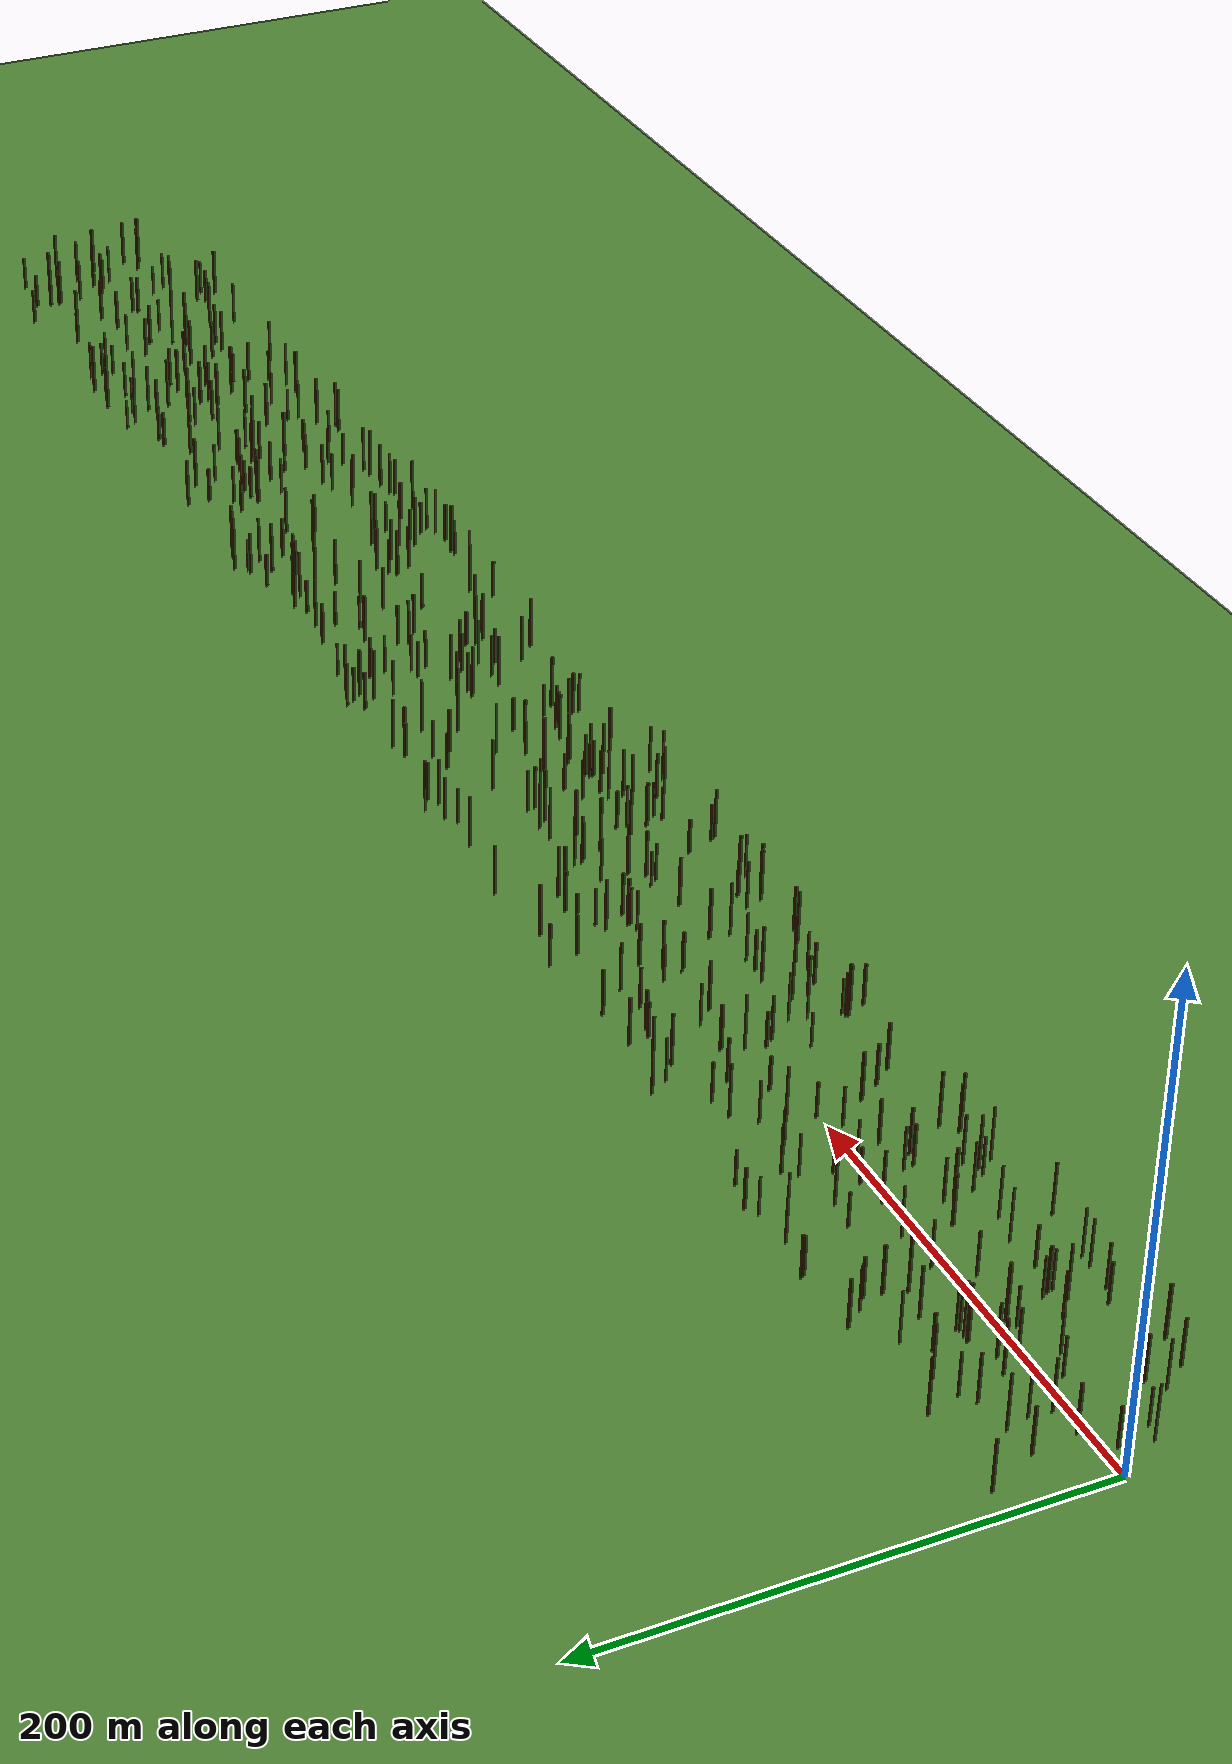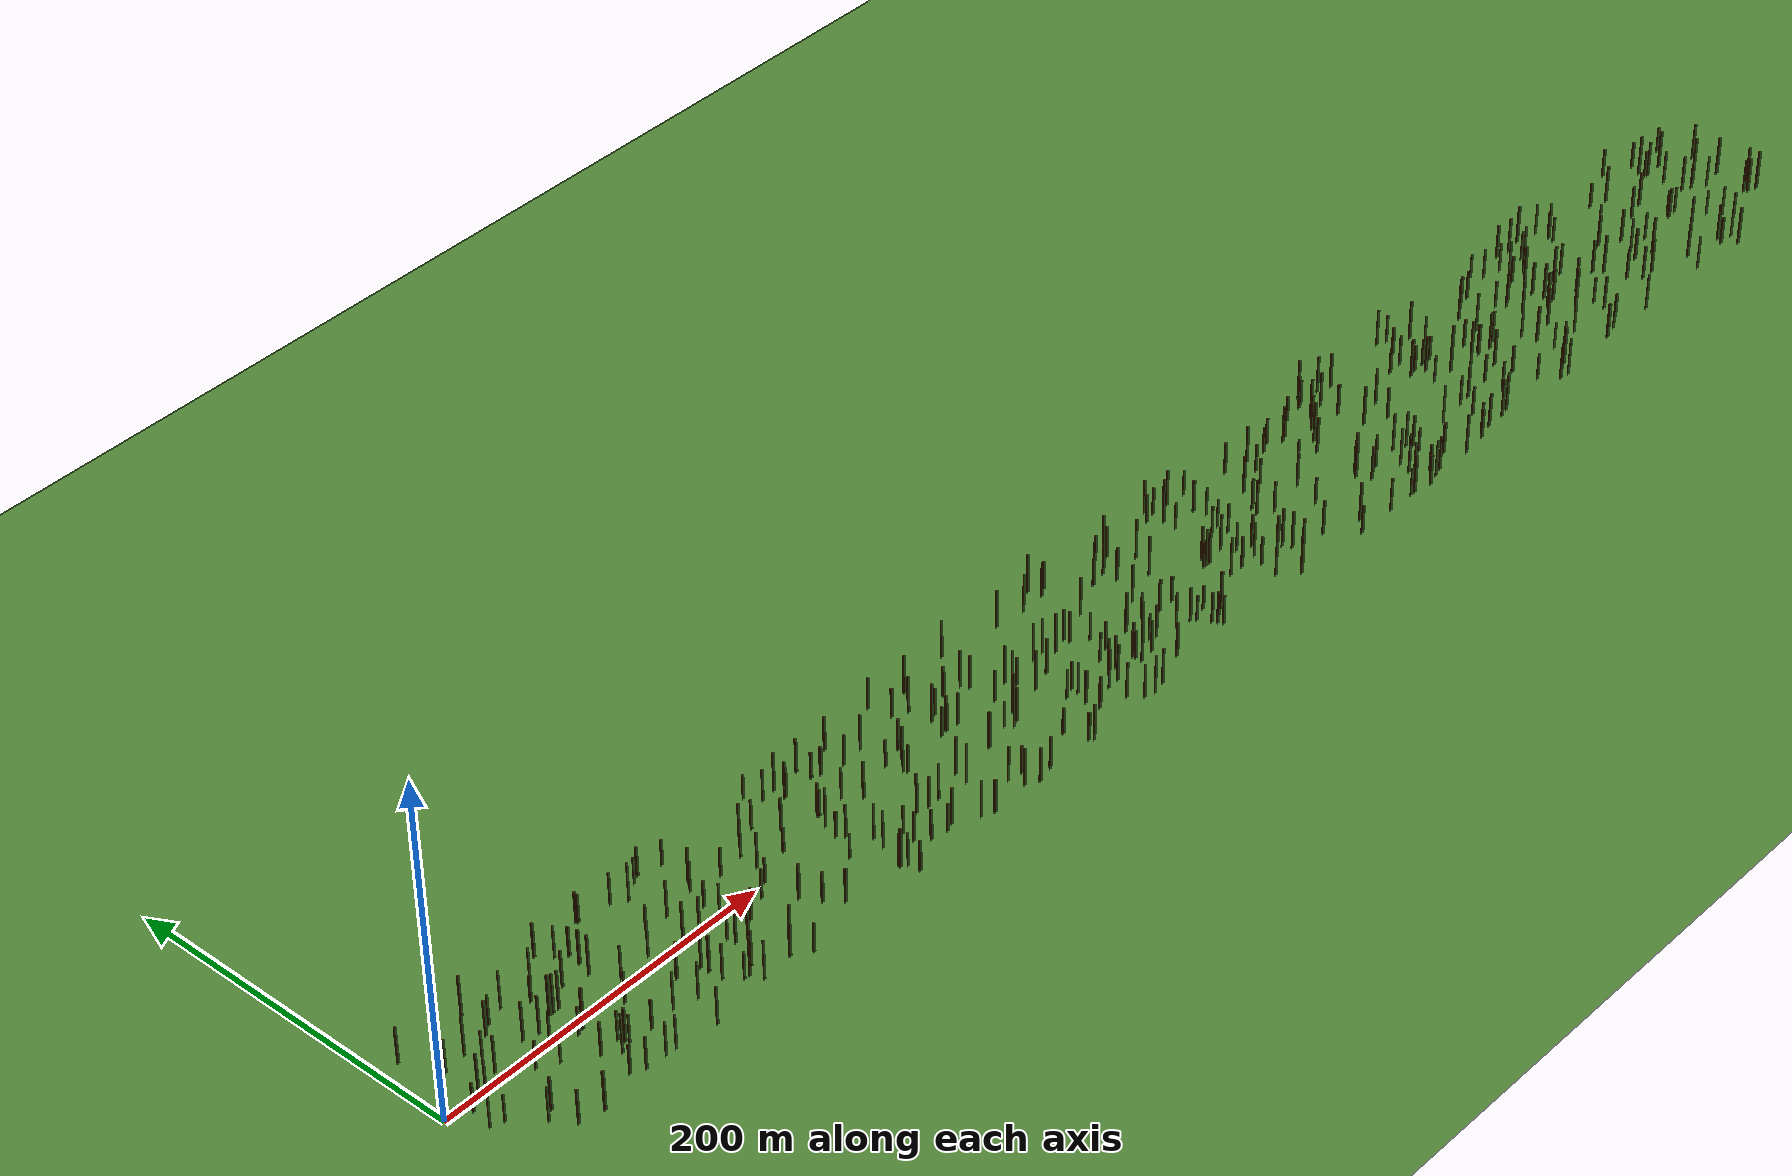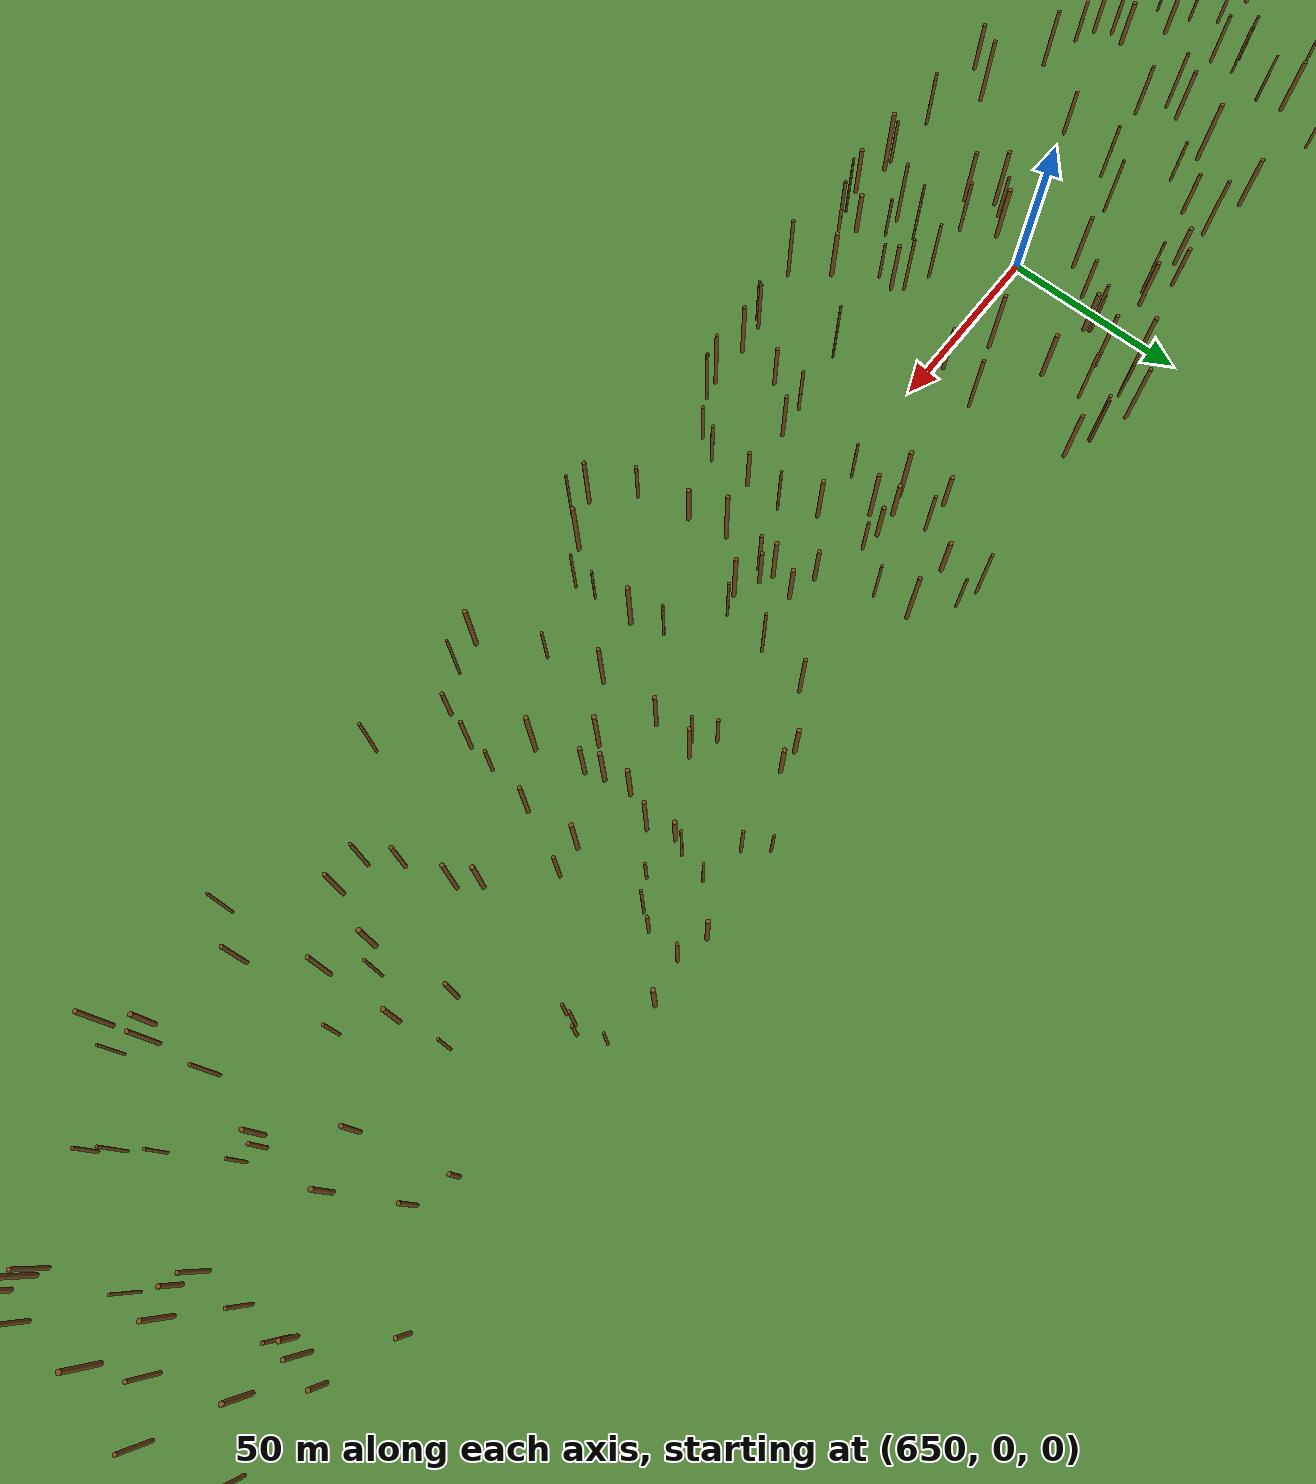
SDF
<?xml version="1.0" ?>
<sdf version="1.6">
  <world name="simple_forest">
    <include>
      <uri>model://sun</uri>
    </include>
    <model name="forest_ground">
      <pose>500 0 0 0 0 0</pose>
      <static>true</static>
      <link name="link">
        <collision name="collision">
          <geometry>
            <plane>
              <normal>0 0 1</normal>
              <size>1200 200</size>
            </plane>
          </geometry>
          <surface>
            <friction>
              <ode>
                <mu>100</mu>
                <mu2>50</mu2>
              </ode>
            </friction>
          </surface>
        </collision>
        <visual name="visual">
          <geometry>
            <plane>
              <normal>0 0 1</normal>
              <size>1200 200</size>
            </plane>
          </geometry>
          <material>
            <ambient>0.3 0.5 0.2 1</ambient>
            <diffuse>0.3 0.5 0.2 1</diffuse>
          </material>
        </visual>
      </link>
    </model>
    <plugin name="gazebo_ros_state" filename="libgazebo_ros_state.so">
      <ros>
        <namespace>/gazebo</namespace>
      </ros>
    </plugin>

    <model name="tree_0">
      <pose>643.0325304733049 -47.498924477733304 8.616053690744113 0 0 0</pose>
      <static>true</static>
      <link name="trunk">
        <collision name="collision">
          <geometry>
            <cylinder>
              <radius>0.38250879551073574</radius>
              <length>17.232107381488227</length>
            </cylinder>
          </geometry>
        </collision>
        <visual name="visual">
          <geometry>
            <cylinder>
              <radius>0.38250879551073574</radius>
              <length>17.232107381488227</length>
            </cylinder>
          </geometry>
          <material>
            <ambient>0.5 0.3 0.1 1</ambient>
            <diffuse>0.5 0.3 0.1 1</diffuse>
          </material>
        </visual>
      </link>
    </model>

    <model name="tree_1">
      <pose>739.1065020223723 17.669948742291126 7.934694163147081 0 0 0</pose>
      <static>true</static>
      <link name="trunk">
        <collision name="collision">
          <geometry>
            <cylinder>
              <radius>0.5676538703114535</radius>
              <length>15.869388326294162</length>
            </cylinder>
          </geometry>
        </collision>
        <visual name="visual">
          <geometry>
            <cylinder>
              <radius>0.5676538703114535</radius>
              <length>15.869388326294162</length>
            </cylinder>
          </geometry>
          <material>
            <ambient>0.5 0.3 0.1 1</ambient>
            <diffuse>0.5 0.3 0.1 1</diffuse>
          </material>
        </visual>
      </link>
    </model>

    <model name="tree_2">
      <pose>427.7026014884177 -47.020278056192964 10.026776440516812 0 0 0</pose>
      <static>true</static>
      <link name="trunk">
        <collision name="collision">
          <geometry>
            <cylinder>
              <radius>0.36559139244108096</radius>
              <length>20.053552881033625</length>
            </cylinder>
          </geometry>
        </collision>
        <visual name="visual">
          <geometry>
            <cylinder>
              <radius>0.36559139244108096</radius>
              <length>20.053552881033625</length>
            </cylinder>
          </geometry>
          <material>
            <ambient>0.5 0.3 0.1 1</ambient>
            <diffuse>0.5 0.3 0.1 1</diffuse>
          </material>
        </visual>
      </link>
    </model>

    <model name="tree_3">
      <pose>36.27060998702499 -30.11623493133515 10.224707403016083 0 0 0</pose>
      <static>true</static>
      <link name="trunk">
        <collision name="collision">
          <geometry>
            <cylinder>
              <radius>0.49496533133385695</radius>
              <length>20.449414806032166</length>
            </cylinder>
          </geometry>
        </collision>
        <visual name="visual">
          <geometry>
            <cylinder>
              <radius>0.49496533133385695</radius>
              <length>20.449414806032166</length>
            </cylinder>
          </geometry>
          <material>
            <ambient>0.5 0.3 0.1 1</ambient>
            <diffuse>0.5 0.3 0.1 1</diffuse>
          </material>
        </visual>
      </link>
    </model>

    <model name="tree_4">
      <pose>228.23621582028974 8.92656838759087 7.5324937983903055 0 0 0</pose>
      <static>true</static>
      <link name="trunk">
        <collision name="collision">
          <geometry>
            <cylinder>
              <radius>0.542829137003348</radius>
              <length>15.064987596780611</length>
            </cylinder>
          </geometry>
        </collision>
        <visual name="visual">
          <geometry>
            <cylinder>
              <radius>0.542829137003348</radius>
              <length>15.064987596780611</length>
            </cylinder>
          </geometry>
          <material>
            <ambient>0.5 0.3 0.1 1</ambient>
            <diffuse>0.5 0.3 0.1 1</diffuse>
          </material>
        </visual>
      </link>
    </model>

    <model name="tree_5">
      <pose>807.7610593144798 19.81393949882269 8.277397499058909 0 0 0</pose>
      <static>true</static>
      <link name="trunk">
        <collision name="collision">
          <geometry>
            <cylinder>
              <radius>0.40207515495539753</radius>
              <length>16.554794998117817</length>
            </cylinder>
          </geometry>
        </collision>
        <visual name="visual">
          <geometry>
            <cylinder>
              <radius>0.40207515495539753</radius>
              <length>16.554794998117817</length>
            </cylinder>
          </geometry>
          <material>
            <ambient>0.5 0.3 0.1 1</ambient>
            <diffuse>0.5 0.3 0.1 1</diffuse>
          </material>
        </visual>
      </link>
    </model>

    <model name="tree_6">
      <pose>957.6409414847134 -16.340545488737327 7.98358188416732 0 0 0</pose>
      <static>true</static>
      <link name="trunk">
        <collision name="collision">
          <geometry>
            <cylinder>
              <radius>0.3278237530140444</radius>
              <length>15.96716376833464</length>
            </cylinder>
          </geometry>
        </collision>
        <visual name="visual">
          <geometry>
            <cylinder>
              <radius>0.3278237530140444</radius>
              <length>15.96716376833464</length>
            </cylinder>
          </geometry>
          <material>
            <ambient>0.5 0.3 0.1 1</ambient>
            <diffuse>0.5 0.3 0.1 1</diffuse>
          </material>
        </visual>
      </link>
    </model>

    <model name="tree_7">
      <pose>849.0194226839852 10.372603136689108 11.14865893346909 0 0 0</pose>
      <static>true</static>
      <link name="trunk">
        <collision name="collision">
          <geometry>
            <cylinder>
              <radius>0.5421384819823141</radius>
              <length>22.29731786693818</length>
            </cylinder>
          </geometry>
        </collision>
        <visual name="visual">
          <geometry>
            <cylinder>
              <radius>0.5421384819823141</radius>
              <length>22.29731786693818</length>
            </cylinder>
          </geometry>
          <material>
            <ambient>0.5 0.3 0.1 1</ambient>
            <diffuse>0.5 0.3 0.1 1</diffuse>
          </material>
        </visual>
      </link>
    </model>

    <model name="tree_8">
      <pose>540.8658105401537 47.31157639793706 10.260203156366135 0 0 0</pose>
      <static>true</static>
      <link name="trunk">
        <collision name="collision">
          <geometry>
            <cylinder>
              <radius>0.413560313162506</radius>
              <length>20.52040631273227</length>
            </cylinder>
          </geometry>
        </collision>
        <visual name="visual">
          <geometry>
            <cylinder>
              <radius>0.413560313162506</radius>
              <length>20.52040631273227</length>
            </cylinder>
          </geometry>
          <material>
            <ambient>0.5 0.3 0.1 1</ambient>
            <diffuse>0.5 0.3 0.1 1</diffuse>
          </material>
        </visual>
      </link>
    </model>

    <model name="tree_9">
      <pose>831.1106176104649 11.851975236424607 10.38676072628381 0 0 0</pose>
      <static>true</static>
      <link name="trunk">
        <collision name="collision">
          <geometry>
            <cylinder>
              <radius>0.5585120700932331</radius>
              <length>20.77352145256762</length>
            </cylinder>
          </geometry>
        </collision>
        <visual name="visual">
          <geometry>
            <cylinder>
              <radius>0.5585120700932331</radius>
              <length>20.77352145256762</length>
            </cylinder>
          </geometry>
          <material>
            <ambient>0.5 0.3 0.1 1</ambient>
            <diffuse>0.5 0.3 0.1 1</diffuse>
          </material>
        </visual>
      </link>
    </model>

    <model name="tree_10">
      <pose>707.5261178527743 -45.41756163443378 8.946939818010536 0 0 0</pose>
      <static>true</static>
      <link name="trunk">
        <collision name="collision">
          <geometry>
            <cylinder>
              <radius>0.36836948269546405</radius>
              <length>17.893879636021072</length>
            </cylinder>
          </geometry>
        </collision>
        <visual name="visual">
          <geometry>
            <cylinder>
              <radius>0.36836948269546405</radius>
              <length>17.893879636021072</length>
            </cylinder>
          </geometry>
          <material>
            <ambient>0.5 0.3 0.1 1</ambient>
            <diffuse>0.5 0.3 0.1 1</diffuse>
          </material>
        </visual>
      </link>
    </model>

    <model name="tree_11">
      <pose>88.99405715439121 -26.72091136389698 8.88986801555046 0 0 0</pose>
      <static>true</static>
      <link name="trunk">
        <collision name="collision">
          <geometry>
            <cylinder>
              <radius>0.3303004288229187</radius>
              <length>17.77973603110092</length>
            </cylinder>
          </geometry>
        </collision>
        <visual name="visual">
          <geometry>
            <cylinder>
              <radius>0.3303004288229187</radius>
              <length>17.77973603110092</length>
            </cylinder>
          </geometry>
          <material>
            <ambient>0.5 0.3 0.1 1</ambient>
            <diffuse>0.5 0.3 0.1 1</diffuse>
          </material>
        </visual>
      </link>
    </model>

    <model name="tree_12">
      <pose>639.3275998217562 -13.516782102991577 8.547535153857439 0 0 0</pose>
      <static>true</static>
      <link name="trunk">
        <collision name="collision">
          <geometry>
            <cylinder>
              <radius>0.4110542901350648</radius>
              <length>17.095070307714877</length>
            </cylinder>
          </geometry>
        </collision>
        <visual name="visual">
          <geometry>
            <cylinder>
              <radius>0.4110542901350648</radius>
              <length>17.095070307714877</length>
            </cylinder>
          </geometry>
          <material>
            <ambient>0.5 0.3 0.1 1</ambient>
            <diffuse>0.5 0.3 0.1 1</diffuse>
          </material>
        </visual>
      </link>
    </model>

    <model name="tree_13">
      <pose>274.3080438286222 43.665458771249405 10.545655028334942 0 0 0</pose>
      <static>true</static>
      <link name="trunk">
        <collision name="collision">
          <geometry>
            <cylinder>
              <radius>0.49441061557397803</radius>
              <length>21.091310056669883</length>
            </cylinder>
          </geometry>
        </collision>
        <visual name="visual">
          <geometry>
            <cylinder>
              <radius>0.49441061557397803</radius>
              <length>21.091310056669883</length>
            </cylinder>
          </geometry>
          <material>
            <ambient>0.5 0.3 0.1 1</ambient>
            <diffuse>0.5 0.3 0.1 1</diffuse>
          </material>
        </visual>
      </link>
    </model>

    <model name="tree_14">
      <pose>179.42726171611602 22.91267979503492 9.397277208788239 0 0 0</pose>
      <static>true</static>
      <link name="trunk">
        <collision name="collision">
          <geometry>
            <cylinder>
              <radius>0.34902074812857853</radius>
              <length>18.794554417576478</length>
            </cylinder>
          </geometry>
        </collision>
        <visual name="visual">
          <geometry>
            <cylinder>
              <radius>0.34902074812857853</radius>
              <length>18.794554417576478</length>
            </cylinder>
          </geometry>
          <material>
            <ambient>0.5 0.3 0.1 1</ambient>
            <diffuse>0.5 0.3 0.1 1</diffuse>
          </material>
        </visual>
      </link>
    </model>

    <model name="tree_15">
      <pose>989.6281171302293 13.999975985409286 10.923071254949374 0 0 0</pose>
      <static>true</static>
      <link name="trunk">
        <collision name="collision">
          <geometry>
            <cylinder>
              <radius>0.46708492313239386</radius>
              <length>21.846142509898748</length>
            </cylinder>
          </geometry>
        </collision>
        <visual name="visual">
          <geometry>
            <cylinder>
              <radius>0.46708492313239386</radius>
              <length>21.846142509898748</length>
            </cylinder>
          </geometry>
          <material>
            <ambient>0.5 0.3 0.1 1</ambient>
            <diffuse>0.5 0.3 0.1 1</diffuse>
          </material>
        </visual>
      </link>
    </model>

    <model name="tree_16">
      <pose>844.4234009879115 27.599991154624476 7.660501219520189 0 0 0</pose>
      <static>true</static>
      <link name="trunk">
        <collision name="collision">
          <geometry>
            <cylinder>
              <radius>0.3687144215892313</radius>
              <length>15.321002439040377</length>
            </cylinder>
          </geometry>
        </collision>
        <visual name="visual">
          <geometry>
            <cylinder>
              <radius>0.3687144215892313</radius>
              <length>15.321002439040377</length>
            </cylinder>
          </geometry>
          <material>
            <ambient>0.5 0.3 0.1 1</ambient>
            <diffuse>0.5 0.3 0.1 1</diffuse>
          </material>
        </visual>
      </link>
    </model>

    <model name="tree_17">
      <pose>322.2985175784911 -23.225912402429728 12.214548571675273 0 0 0</pose>
      <static>true</static>
      <link name="trunk">
        <collision name="collision">
          <geometry>
            <cylinder>
              <radius>0.3632948530758979</radius>
              <length>24.429097143350546</length>
            </cylinder>
          </geometry>
        </collision>
        <visual name="visual">
          <geometry>
            <cylinder>
              <radius>0.3632948530758979</radius>
              <length>24.429097143350546</length>
            </cylinder>
          </geometry>
          <material>
            <ambient>0.5 0.3 0.1 1</ambient>
            <diffuse>0.5 0.3 0.1 1</diffuse>
          </material>
        </visual>
      </link>
    </model>

    <model name="tree_18">
      <pose>877.6039502079421 -18.532211920152207 9.47815950530332 0 0 0</pose>
      <static>true</static>
      <link name="trunk">
        <collision name="collision">
          <geometry>
            <cylinder>
              <radius>0.49663159958846403</radius>
              <length>18.95631901060664</length>
            </cylinder>
          </geometry>
        </collision>
        <visual name="visual">
          <geometry>
            <cylinder>
              <radius>0.49663159958846403</radius>
              <length>18.95631901060664</length>
            </cylinder>
          </geometry>
          <material>
            <ambient>0.5 0.3 0.1 1</ambient>
            <diffuse>0.5 0.3 0.1 1</diffuse>
          </material>
        </visual>
      </link>
    </model>

    <model name="tree_19">
      <pose>915.4021138431381 -4.114814741260119 8.733137538469917 0 0 0</pose>
      <static>true</static>
      <link name="trunk">
        <collision name="collision">
          <geometry>
            <cylinder>
              <radius>0.37946404994941574</radius>
              <length>17.466275076939834</length>
            </cylinder>
          </geometry>
        </collision>
        <visual name="visual">
          <geometry>
            <cylinder>
              <radius>0.37946404994941574</radius>
              <length>17.466275076939834</length>
            </cylinder>
          </geometry>
          <material>
            <ambient>0.5 0.3 0.1 1</ambient>
            <diffuse>0.5 0.3 0.1 1</diffuse>
          </material>
        </visual>
      </link>
    </model>

    <model name="tree_20">
      <pose>565.7544528215193 -23.725839147706473 11.989114418012385 0 0 0</pose>
      <static>true</static>
      <link name="trunk">
        <collision name="collision">
          <geometry>
            <cylinder>
              <radius>0.4753757970670621</radius>
              <length>23.97822883602477</length>
            </cylinder>
          </geometry>
        </collision>
        <visual name="visual">
          <geometry>
            <cylinder>
              <radius>0.4753757970670621</radius>
              <length>23.97822883602477</length>
            </cylinder>
          </geometry>
          <material>
            <ambient>0.5 0.3 0.1 1</ambient>
            <diffuse>0.5 0.3 0.1 1</diffuse>
          </material>
        </visual>
      </link>
    </model>

    <model name="tree_21">
      <pose>405.4065000889933 -28.067924084271667 10.047631468382322 0 0 0</pose>
      <static>true</static>
      <link name="trunk">
        <collision name="collision">
          <geometry>
            <cylinder>
              <radius>0.599261281948533</radius>
              <length>20.095262936764644</length>
            </cylinder>
          </geometry>
        </collision>
        <visual name="visual">
          <geometry>
            <cylinder>
              <radius>0.599261281948533</radius>
              <length>20.095262936764644</length>
            </cylinder>
          </geometry>
          <material>
            <ambient>0.5 0.3 0.1 1</ambient>
            <diffuse>0.5 0.3 0.1 1</diffuse>
          </material>
        </visual>
      </link>
    </model>

    <model name="tree_22">
      <pose>100.00031805205595 -45.288362457526546 10.63723020851545 0 0 0</pose>
      <static>true</static>
      <link name="trunk">
        <collision name="collision">
          <geometry>
            <cylinder>
              <radius>0.33289473910519773</radius>
              <length>21.2744604170309</length>
            </cylinder>
          </geometry>
        </collision>
        <visual name="visual">
          <geometry>
            <cylinder>
              <radius>0.33289473910519773</radius>
              <length>21.2744604170309</length>
            </cylinder>
          </geometry>
          <material>
            <ambient>0.5 0.3 0.1 1</ambient>
            <diffuse>0.5 0.3 0.1 1</diffuse>
          </material>
        </visual>
      </link>
    </model>

    <model name="tree_23">
      <pose>794.1585707193344 -7.784003320031594 9.408096432532684 0 0 0</pose>
      <static>true</static>
      <link name="trunk">
        <collision name="collision">
          <geometry>
            <cylinder>
              <radius>0.31905831184558714</radius>
              <length>18.816192865065368</length>
            </cylinder>
          </geometry>
        </collision>
        <visual name="visual">
          <geometry>
            <cylinder>
              <radius>0.31905831184558714</radius>
              <length>18.816192865065368</length>
            </cylinder>
          </geometry>
          <material>
            <ambient>0.5 0.3 0.1 1</ambient>
            <diffuse>0.5 0.3 0.1 1</diffuse>
          </material>
        </visual>
      </link>
    </model>

    <model name="tree_24">
      <pose>996.1601664376958 2.911434509913704 11.803898511172491 0 0 0</pose>
      <static>true</static>
      <link name="trunk">
        <collision name="collision">
          <geometry>
            <cylinder>
              <radius>0.5913235132840855</radius>
              <length>23.607797022344982</length>
            </cylinder>
          </geometry>
        </collision>
        <visual name="visual">
          <geometry>
            <cylinder>
              <radius>0.5913235132840855</radius>
              <length>23.607797022344982</length>
            </cylinder>
          </geometry>
          <material>
            <ambient>0.5 0.3 0.1 1</ambient>
            <diffuse>0.5 0.3 0.1 1</diffuse>
          </material>
        </visual>
      </link>
    </model>

    <model name="tree_25">
      <pose>21.366211723391437 22.07218193601946 10.184851652043976 0 0 0</pose>
      <static>true</static>
      <link name="trunk">
        <collision name="collision">
          <geometry>
            <cylinder>
              <radius>0.5045131107079724</radius>
              <length>20.369703304087952</length>
            </cylinder>
          </geometry>
        </collision>
        <visual name="visual">
          <geometry>
            <cylinder>
              <radius>0.5045131107079724</radius>
              <length>20.369703304087952</length>
            </cylinder>
          </geometry>
          <material>
            <ambient>0.5 0.3 0.1 1</ambient>
            <diffuse>0.5 0.3 0.1 1</diffuse>
          </material>
        </visual>
      </link>
    </model>

    <model name="tree_26">
      <pose>274.15693805301737 14.0961798579808 9.673826253345524 0 0 0</pose>
      <static>true</static>
      <link name="trunk">
        <collision name="collision">
          <geometry>
            <cylinder>
              <radius>0.33346565207876294</radius>
              <length>19.34765250669105</length>
            </cylinder>
          </geometry>
        </collision>
        <visual name="visual">
          <geometry>
            <cylinder>
              <radius>0.33346565207876294</radius>
              <length>19.34765250669105</length>
            </cylinder>
          </geometry>
          <material>
            <ambient>0.5 0.3 0.1 1</ambient>
            <diffuse>0.5 0.3 0.1 1</diffuse>
          </material>
        </visual>
      </link>
    </model>

    <model name="tree_27">
      <pose>459.18646926591435 45.38159275210802 8.816945253755454 0 0 0</pose>
      <static>true</static>
      <link name="trunk">
        <collision name="collision">
          <geometry>
            <cylinder>
              <radius>0.5627558821134582</radius>
              <length>17.63389050751091</length>
            </cylinder>
          </geometry>
        </collision>
        <visual name="visual">
          <geometry>
            <cylinder>
              <radius>0.5627558821134582</radius>
              <length>17.63389050751091</length>
            </cylinder>
          </geometry>
          <material>
            <ambient>0.5 0.3 0.1 1</ambient>
            <diffuse>0.5 0.3 0.1 1</diffuse>
          </material>
        </visual>
      </link>
    </model>

    <model name="tree_28">
      <pose>505.58025191979533 -32.134811946986865 11.852592849183836 0 0 0</pose>
      <static>true</static>
      <link name="trunk">
        <collision name="collision">
          <geometry>
            <cylinder>
              <radius>0.5737883518034461</radius>
              <length>23.70518569836767</length>
            </cylinder>
          </geometry>
        </collision>
        <visual name="visual">
          <geometry>
            <cylinder>
              <radius>0.5737883518034461</radius>
              <length>23.70518569836767</length>
            </cylinder>
          </geometry>
          <material>
            <ambient>0.5 0.3 0.1 1</ambient>
            <diffuse>0.5 0.3 0.1 1</diffuse>
          </material>
        </visual>
      </link>
    </model>

    <model name="tree_29">
      <pose>305.46034353414655 13.894949486600517 8.264196342748175 0 0 0</pose>
      <static>true</static>
      <link name="trunk">
        <collision name="collision">
          <geometry>
            <cylinder>
              <radius>0.4826910634314517</radius>
              <length>16.52839268549635</length>
            </cylinder>
          </geometry>
        </collision>
        <visual name="visual">
          <geometry>
            <cylinder>
              <radius>0.4826910634314517</radius>
              <length>16.52839268549635</length>
            </cylinder>
          </geometry>
          <material>
            <ambient>0.5 0.3 0.1 1</ambient>
            <diffuse>0.5 0.3 0.1 1</diffuse>
          </material>
        </visual>
      </link>
    </model>

    <model name="tree_30">
      <pose>764.8856920743998 3.9379030119625753 10.151768360975888 0 0 0</pose>
      <static>true</static>
      <link name="trunk">
        <collision name="collision">
          <geometry>
            <cylinder>
              <radius>0.5335879435891675</radius>
              <length>20.303536721951776</length>
            </cylinder>
          </geometry>
        </collision>
        <visual name="visual">
          <geometry>
            <cylinder>
              <radius>0.5335879435891675</radius>
              <length>20.303536721951776</length>
            </cylinder>
          </geometry>
          <material>
            <ambient>0.5 0.3 0.1 1</ambient>
            <diffuse>0.5 0.3 0.1 1</diffuse>
          </material>
        </visual>
      </link>
    </model>

    <model name="tree_31">
      <pose>10.56617716666407 -17.58439429953269 12.145493081323085 0 0 0</pose>
      <static>true</static>
      <link name="trunk">
        <collision name="collision">
          <geometry>
            <cylinder>
              <radius>0.3058430227157497</radius>
              <length>24.29098616264617</length>
            </cylinder>
          </geometry>
        </collision>
        <visual name="visual">
          <geometry>
            <cylinder>
              <radius>0.3058430227157497</radius>
              <length>24.29098616264617</length>
            </cylinder>
          </geometry>
          <material>
            <ambient>0.5 0.3 0.1 1</ambient>
            <diffuse>0.5 0.3 0.1 1</diffuse>
          </material>
        </visual>
      </link>
    </model>

    <model name="tree_32">
      <pose>879.9346590449524 33.16655293611794 7.7896258324709375 0 0 0</pose>
      <static>true</static>
      <link name="trunk">
        <collision name="collision">
          <geometry>
            <cylinder>
              <radius>0.3922542376207984</radius>
              <length>15.579251664941875</length>
            </cylinder>
          </geometry>
        </collision>
        <visual name="visual">
          <geometry>
            <cylinder>
              <radius>0.3922542376207984</radius>
              <length>15.579251664941875</length>
            </cylinder>
          </geometry>
          <material>
            <ambient>0.5 0.3 0.1 1</ambient>
            <diffuse>0.5 0.3 0.1 1</diffuse>
          </material>
        </visual>
      </link>
    </model>

    <model name="tree_33">
      <pose>879.2295032120002 44.694944529799415 9.92995231658307 0 0 0</pose>
      <static>true</static>
      <link name="trunk">
        <collision name="collision">
          <geometry>
            <cylinder>
              <radius>0.32569603562036364</radius>
              <length>19.85990463316614</length>
            </cylinder>
          </geometry>
        </collision>
        <visual name="visual">
          <geometry>
            <cylinder>
              <radius>0.32569603562036364</radius>
              <length>19.85990463316614</length>
            </cylinder>
          </geometry>
          <material>
            <ambient>0.5 0.3 0.1 1</ambient>
            <diffuse>0.5 0.3 0.1 1</diffuse>
          </material>
        </visual>
      </link>
    </model>

    <model name="tree_34">
      <pose>78.52039328369978 26.060216525723163 8.141957322498815 0 0 0</pose>
      <static>true</static>
      <link name="trunk">
        <collision name="collision">
          <geometry>
            <cylinder>
              <radius>0.5297503287920963</radius>
              <length>16.28391464499763</length>
            </cylinder>
          </geometry>
        </collision>
        <visual name="visual">
          <geometry>
            <cylinder>
              <radius>0.5297503287920963</radius>
              <length>16.28391464499763</length>
            </cylinder>
          </geometry>
          <material>
            <ambient>0.5 0.3 0.1 1</ambient>
            <diffuse>0.5 0.3 0.1 1</diffuse>
          </material>
        </visual>
      </link>
    </model>

    <model name="tree_35">
      <pose>480.529554317744 4.9803593494943925 11.862165205426287 0 0 0</pose>
      <static>true</static>
      <link name="trunk">
        <collision name="collision">
          <geometry>
            <cylinder>
              <radius>0.3795169886820177</radius>
              <length>23.724330410852573</length>
            </cylinder>
          </geometry>
        </collision>
        <visual name="visual">
          <geometry>
            <cylinder>
              <radius>0.3795169886820177</radius>
              <length>23.724330410852573</length>
            </cylinder>
          </geometry>
          <material>
            <ambient>0.5 0.3 0.1 1</ambient>
            <diffuse>0.5 0.3 0.1 1</diffuse>
          </material>
        </visual>
      </link>
    </model>

    <model name="tree_36">
      <pose>428.90656079887805 -28.820179455791795 11.149655345449881 0 0 0</pose>
      <static>true</static>
      <link name="trunk">
        <collision name="collision">
          <geometry>
            <cylinder>
              <radius>0.46178882663383747</radius>
              <length>22.299310690899762</length>
            </cylinder>
          </geometry>
        </collision>
        <visual name="visual">
          <geometry>
            <cylinder>
              <radius>0.46178882663383747</radius>
              <length>22.299310690899762</length>
            </cylinder>
          </geometry>
          <material>
            <ambient>0.5 0.3 0.1 1</ambient>
            <diffuse>0.5 0.3 0.1 1</diffuse>
          </material>
        </visual>
      </link>
    </model>

    <model name="tree_37">
      <pose>209.13955275579895 -18.828370869910504 10.749390288197267 0 0 0</pose>
      <static>true</static>
      <link name="trunk">
        <collision name="collision">
          <geometry>
            <cylinder>
              <radius>0.5985448069982684</radius>
              <length>21.498780576394534</length>
            </cylinder>
          </geometry>
        </collision>
        <visual name="visual">
          <geometry>
            <cylinder>
              <radius>0.5985448069982684</radius>
              <length>21.498780576394534</length>
            </cylinder>
          </geometry>
          <material>
            <ambient>0.5 0.3 0.1 1</ambient>
            <diffuse>0.5 0.3 0.1 1</diffuse>
          </material>
        </visual>
      </link>
    </model>

    <model name="tree_38">
      <pose>443.71908307535904 1.7575841035590614 8.623486685157786 0 0 0</pose>
      <static>true</static>
      <link name="trunk">
        <collision name="collision">
          <geometry>
            <cylinder>
              <radius>0.3363012587604797</radius>
              <length>17.246973370315573</length>
            </cylinder>
          </geometry>
        </collision>
        <visual name="visual">
          <geometry>
            <cylinder>
              <radius>0.3363012587604797</radius>
              <length>17.246973370315573</length>
            </cylinder>
          </geometry>
          <material>
            <ambient>0.5 0.3 0.1 1</ambient>
            <diffuse>0.5 0.3 0.1 1</diffuse>
          </material>
        </visual>
      </link>
    </model>

    <model name="tree_39">
      <pose>344.7047065259808 8.83087184572333 8.601086922257798 0 0 0</pose>
      <static>true</static>
      <link name="trunk">
        <collision name="collision">
          <geometry>
            <cylinder>
              <radius>0.3690344197789731</radius>
              <length>17.202173844515595</length>
            </cylinder>
          </geometry>
        </collision>
        <visual name="visual">
          <geometry>
            <cylinder>
              <radius>0.3690344197789731</radius>
              <length>17.202173844515595</length>
            </cylinder>
          </geometry>
          <material>
            <ambient>0.5 0.3 0.1 1</ambient>
            <diffuse>0.5 0.3 0.1 1</diffuse>
          </material>
        </visual>
      </link>
    </model>

    <model name="tree_40">
      <pose>80.28315514894221 13.110295727009891 12.02710006503064 0 0 0</pose>
      <static>true</static>
      <link name="trunk">
        <collision name="collision">
          <geometry>
            <cylinder>
              <radius>0.3686825351433463</radius>
              <length>24.05420013006128</length>
            </cylinder>
          </geometry>
        </collision>
        <visual name="visual">
          <geometry>
            <cylinder>
              <radius>0.3686825351433463</radius>
              <length>24.05420013006128</length>
            </cylinder>
          </geometry>
          <material>
            <ambient>0.5 0.3 0.1 1</ambient>
            <diffuse>0.5 0.3 0.1 1</diffuse>
          </material>
        </visual>
      </link>
    </model>

    <model name="tree_41">
      <pose>861.039046251209 -42.91426501113466 10.844888891481403 0 0 0</pose>
      <static>true</static>
      <link name="trunk">
        <collision name="collision">
          <geometry>
            <cylinder>
              <radius>0.3714013903106985</radius>
              <length>21.689777782962807</length>
            </cylinder>
          </geometry>
        </collision>
        <visual name="visual">
          <geometry>
            <cylinder>
              <radius>0.3714013903106985</radius>
              <length>21.689777782962807</length>
            </cylinder>
          </geometry>
          <material>
            <ambient>0.5 0.3 0.1 1</ambient>
            <diffuse>0.5 0.3 0.1 1</diffuse>
          </material>
        </visual>
      </link>
    </model>

    <model name="tree_42">
      <pose>222.0944392967342 -36.768815127497504 10.355215466626422 0 0 0</pose>
      <static>true</static>
      <link name="trunk">
        <collision name="collision">
          <geometry>
            <cylinder>
              <radius>0.5806542721742013</radius>
              <length>20.710430933252844</length>
            </cylinder>
          </geometry>
        </collision>
        <visual name="visual">
          <geometry>
            <cylinder>
              <radius>0.5806542721742013</radius>
              <length>20.710430933252844</length>
            </cylinder>
          </geometry>
          <material>
            <ambient>0.5 0.3 0.1 1</ambient>
            <diffuse>0.5 0.3 0.1 1</diffuse>
          </material>
        </visual>
      </link>
    </model>

    <model name="tree_43">
      <pose>477.94431604867617 28.461942429075336 8.452049571809388 0 0 0</pose>
      <static>true</static>
      <link name="trunk">
        <collision name="collision">
          <geometry>
            <cylinder>
              <radius>0.542249099329993</radius>
              <length>16.904099143618776</length>
            </cylinder>
          </geometry>
        </collision>
        <visual name="visual">
          <geometry>
            <cylinder>
              <radius>0.542249099329993</radius>
              <length>16.904099143618776</length>
            </cylinder>
          </geometry>
          <material>
            <ambient>0.5 0.3 0.1 1</ambient>
            <diffuse>0.5 0.3 0.1 1</diffuse>
          </material>
        </visual>
      </link>
    </model>

    <model name="tree_44">
      <pose>105.9615060865351 -6.894881759362249 9.835123340183376 0 0 0</pose>
      <static>true</static>
      <link name="trunk">
        <collision name="collision">
          <geometry>
            <cylinder>
              <radius>0.4270735869059762</radius>
              <length>19.670246680366752</length>
            </cylinder>
          </geometry>
        </collision>
        <visual name="visual">
          <geometry>
            <cylinder>
              <radius>0.4270735869059762</radius>
              <length>19.670246680366752</length>
            </cylinder>
          </geometry>
          <material>
            <ambient>0.5 0.3 0.1 1</ambient>
            <diffuse>0.5 0.3 0.1 1</diffuse>
          </material>
        </visual>
      </link>
    </model>

    <model name="tree_45">
      <pose>731.785090965252 17.336454729330157 7.992089355759794 0 0 0</pose>
      <static>true</static>
      <link name="trunk">
        <collision name="collision">
          <geometry>
            <cylinder>
              <radius>0.5952495634097899</radius>
              <length>15.984178711519588</length>
            </cylinder>
          </geometry>
        </collision>
        <visual name="visual">
          <geometry>
            <cylinder>
              <radius>0.5952495634097899</radius>
              <length>15.984178711519588</length>
            </cylinder>
          </geometry>
          <material>
            <ambient>0.5 0.3 0.1 1</ambient>
            <diffuse>0.5 0.3 0.1 1</diffuse>
          </material>
        </visual>
      </link>
    </model>

    <model name="tree_46">
      <pose>408.5950692812461 -16.069739460503683 8.743281669601428 0 0 0</pose>
      <static>true</static>
      <link name="trunk">
        <collision name="collision">
          <geometry>
            <cylinder>
              <radius>0.5585017609058374</radius>
              <length>17.486563339202856</length>
            </cylinder>
          </geometry>
        </collision>
        <visual name="visual">
          <geometry>
            <cylinder>
              <radius>0.5585017609058374</radius>
              <length>17.486563339202856</length>
            </cylinder>
          </geometry>
          <material>
            <ambient>0.5 0.3 0.1 1</ambient>
            <diffuse>0.5 0.3 0.1 1</diffuse>
          </material>
        </visual>
      </link>
    </model>

    <model name="tree_47">
      <pose>198.3068193564034 -5.138645216686811 8.892725723334703 0 0 0</pose>
      <static>true</static>
      <link name="trunk">
        <collision name="collision">
          <geometry>
            <cylinder>
              <radius>0.4265644919503212</radius>
              <length>17.785451446669406</length>
            </cylinder>
          </geometry>
        </collision>
        <visual name="visual">
          <geometry>
            <cylinder>
              <radius>0.4265644919503212</radius>
              <length>17.785451446669406</length>
            </cylinder>
          </geometry>
          <material>
            <ambient>0.5 0.3 0.1 1</ambient>
            <diffuse>0.5 0.3 0.1 1</diffuse>
          </material>
        </visual>
      </link>
    </model>

    <model name="tree_48">
      <pose>257.3083834032795 42.32655992760128 11.806745523809152 0 0 0</pose>
      <static>true</static>
      <link name="trunk">
        <collision name="collision">
          <geometry>
            <cylinder>
              <radius>0.4329392235160371</radius>
              <length>23.613491047618304</length>
            </cylinder>
          </geometry>
        </collision>
        <visual name="visual">
          <geometry>
            <cylinder>
              <radius>0.4329392235160371</radius>
              <length>23.613491047618304</length>
            </cylinder>
          </geometry>
          <material>
            <ambient>0.5 0.3 0.1 1</ambient>
            <diffuse>0.5 0.3 0.1 1</diffuse>
          </material>
        </visual>
      </link>
    </model>

    <model name="tree_49">
      <pose>554.8220593253495 -44.941167047511875 11.680137925399759 0 0 0</pose>
      <static>true</static>
      <link name="trunk">
        <collision name="collision">
          <geometry>
            <cylinder>
              <radius>0.5997847405238179</radius>
              <length>23.360275850799518</length>
            </cylinder>
          </geometry>
        </collision>
        <visual name="visual">
          <geometry>
            <cylinder>
              <radius>0.5997847405238179</radius>
              <length>23.360275850799518</length>
            </cylinder>
          </geometry>
          <material>
            <ambient>0.5 0.3 0.1 1</ambient>
            <diffuse>0.5 0.3 0.1 1</diffuse>
          </material>
        </visual>
      </link>
    </model>

    <model name="tree_50">
      <pose>969.3062947119038 42.63669830081275 8.33155555301957 0 0 0</pose>
      <static>true</static>
      <link name="trunk">
        <collision name="collision">
          <geometry>
            <cylinder>
              <radius>0.5546087203242915</radius>
              <length>16.66311110603914</length>
            </cylinder>
          </geometry>
        </collision>
        <visual name="visual">
          <geometry>
            <cylinder>
              <radius>0.5546087203242915</radius>
              <length>16.66311110603914</length>
            </cylinder>
          </geometry>
          <material>
            <ambient>0.5 0.3 0.1 1</ambient>
            <diffuse>0.5 0.3 0.1 1</diffuse>
          </material>
        </visual>
      </link>
    </model>

    <model name="tree_51">
      <pose>490.78471419621127 -28.625270080081833 7.793176999860894 0 0 0</pose>
      <static>true</static>
      <link name="trunk">
        <collision name="collision">
          <geometry>
            <cylinder>
              <radius>0.42031208776483575</radius>
              <length>15.586353999721789</length>
            </cylinder>
          </geometry>
        </collision>
        <visual name="visual">
          <geometry>
            <cylinder>
              <radius>0.42031208776483575</radius>
              <length>15.586353999721789</length>
            </cylinder>
          </geometry>
          <material>
            <ambient>0.5 0.3 0.1 1</ambient>
            <diffuse>0.5 0.3 0.1 1</diffuse>
          </material>
        </visual>
      </link>
    </model>

    <model name="tree_52">
      <pose>385.18338778714696 48.5308843779726 11.420353009742847 0 0 0</pose>
      <static>true</static>
      <link name="trunk">
        <collision name="collision">
          <geometry>
            <cylinder>
              <radius>0.37956091745164555</radius>
              <length>22.840706019485694</length>
            </cylinder>
          </geometry>
        </collision>
        <visual name="visual">
          <geometry>
            <cylinder>
              <radius>0.37956091745164555</radius>
              <length>22.840706019485694</length>
            </cylinder>
          </geometry>
          <material>
            <ambient>0.5 0.3 0.1 1</ambient>
            <diffuse>0.5 0.3 0.1 1</diffuse>
          </material>
        </visual>
      </link>
    </model>

    <model name="tree_53">
      <pose>460.4582836657519 -7.699251400983712 12.47711344746357 0 0 0</pose>
      <static>true</static>
      <link name="trunk">
        <collision name="collision">
          <geometry>
            <cylinder>
              <radius>0.587195292257902</radius>
              <length>24.95422689492714</length>
            </cylinder>
          </geometry>
        </collision>
        <visual name="visual">
          <geometry>
            <cylinder>
              <radius>0.587195292257902</radius>
              <length>24.95422689492714</length>
            </cylinder>
          </geometry>
          <material>
            <ambient>0.5 0.3 0.1 1</ambient>
            <diffuse>0.5 0.3 0.1 1</diffuse>
          </material>
        </visual>
      </link>
    </model>

    <model name="tree_54">
      <pose>560.210640171562 21.840827529632605 8.98353912747282 0 0 0</pose>
      <static>true</static>
      <link name="trunk">
        <collision name="collision">
          <geometry>
            <cylinder>
              <radius>0.3464390475822192</radius>
              <length>17.96707825494564</length>
            </cylinder>
          </geometry>
        </collision>
        <visual name="visual">
          <geometry>
            <cylinder>
              <radius>0.3464390475822192</radius>
              <length>17.96707825494564</length>
            </cylinder>
          </geometry>
          <material>
            <ambient>0.5 0.3 0.1 1</ambient>
            <diffuse>0.5 0.3 0.1 1</diffuse>
          </material>
        </visual>
      </link>
    </model>

    <model name="tree_55">
      <pose>969.0222713194672 7.918029081625619 11.239877801895322 0 0 0</pose>
      <static>true</static>
      <link name="trunk">
        <collision name="collision">
          <geometry>
            <cylinder>
              <radius>0.46265856041228226</radius>
              <length>22.479755603790643</length>
            </cylinder>
          </geometry>
        </collision>
        <visual name="visual">
          <geometry>
            <cylinder>
              <radius>0.46265856041228226</radius>
              <length>22.479755603790643</length>
            </cylinder>
          </geometry>
          <material>
            <ambient>0.5 0.3 0.1 1</ambient>
            <diffuse>0.5 0.3 0.1 1</diffuse>
          </material>
        </visual>
      </link>
    </model>

    <model name="tree_56">
      <pose>66.59362017840824 8.417759445897119 11.763599460241426 0 0 0</pose>
      <static>true</static>
      <link name="trunk">
        <collision name="collision">
          <geometry>
            <cylinder>
              <radius>0.45085511487585406</radius>
              <length>23.527198920482853</length>
            </cylinder>
          </geometry>
        </collision>
        <visual name="visual">
          <geometry>
            <cylinder>
              <radius>0.45085511487585406</radius>
              <length>23.527198920482853</length>
            </cylinder>
          </geometry>
          <material>
            <ambient>0.5 0.3 0.1 1</ambient>
            <diffuse>0.5 0.3 0.1 1</diffuse>
          </material>
        </visual>
      </link>
    </model>

    <model name="tree_57">
      <pose>165.85840066008842 46.07789032744503 8.429124804903616 0 0 0</pose>
      <static>true</static>
      <link name="trunk">
        <collision name="collision">
          <geometry>
            <cylinder>
              <radius>0.32403343957217606</radius>
              <length>16.85824960980723</length>
            </cylinder>
          </geometry>
        </collision>
        <visual name="visual">
          <geometry>
            <cylinder>
              <radius>0.32403343957217606</radius>
              <length>16.85824960980723</length>
            </cylinder>
          </geometry>
          <material>
            <ambient>0.5 0.3 0.1 1</ambient>
            <diffuse>0.5 0.3 0.1 1</diffuse>
          </material>
        </visual>
      </link>
    </model>

    <model name="tree_58">
      <pose>599.0847553855274 17.521255360409015 8.099433069735621 0 0 0</pose>
      <static>true</static>
      <link name="trunk">
        <collision name="collision">
          <geometry>
            <cylinder>
              <radius>0.3705611685002793</radius>
              <length>16.198866139471242</length>
            </cylinder>
          </geometry>
        </collision>
        <visual name="visual">
          <geometry>
            <cylinder>
              <radius>0.3705611685002793</radius>
              <length>16.198866139471242</length>
            </cylinder>
          </geometry>
          <material>
            <ambient>0.5 0.3 0.1 1</ambient>
            <diffuse>0.5 0.3 0.1 1</diffuse>
          </material>
        </visual>
      </link>
    </model>

    <model name="tree_59">
      <pose>891.3844409881432 -25.378465221137514 10.596907551660514 0 0 0</pose>
      <static>true</static>
      <link name="trunk">
        <collision name="collision">
          <geometry>
            <cylinder>
              <radius>0.47835574606003234</radius>
              <length>21.19381510332103</length>
            </cylinder>
          </geometry>
        </collision>
        <visual name="visual">
          <geometry>
            <cylinder>
              <radius>0.47835574606003234</radius>
              <length>21.19381510332103</length>
            </cylinder>
          </geometry>
          <material>
            <ambient>0.5 0.3 0.1 1</ambient>
            <diffuse>0.5 0.3 0.1 1</diffuse>
          </material>
        </visual>
      </link>
    </model>

    <model name="tree_60">
      <pose>425.03266618251376 8.367228929122476 12.173531288682137 0 0 0</pose>
      <static>true</static>
      <link name="trunk">
        <collision name="collision">
          <geometry>
            <cylinder>
              <radius>0.45683481465958764</radius>
              <length>24.347062577364273</length>
            </cylinder>
          </geometry>
        </collision>
        <visual name="visual">
          <geometry>
            <cylinder>
              <radius>0.45683481465958764</radius>
              <length>24.347062577364273</length>
            </cylinder>
          </geometry>
          <material>
            <ambient>0.5 0.3 0.1 1</ambient>
            <diffuse>0.5 0.3 0.1 1</diffuse>
          </material>
        </visual>
      </link>
    </model>

    <model name="tree_61">
      <pose>212.21660742930106 21.619180078941483 9.478929233956272 0 0 0</pose>
      <static>true</static>
      <link name="trunk">
        <collision name="collision">
          <geometry>
            <cylinder>
              <radius>0.3716057857847538</radius>
              <length>18.957858467912544</length>
            </cylinder>
          </geometry>
        </collision>
        <visual name="visual">
          <geometry>
            <cylinder>
              <radius>0.3716057857847538</radius>
              <length>18.957858467912544</length>
            </cylinder>
          </geometry>
          <material>
            <ambient>0.5 0.3 0.1 1</ambient>
            <diffuse>0.5 0.3 0.1 1</diffuse>
          </material>
        </visual>
      </link>
    </model>

    <model name="tree_62">
      <pose>674.9733207303716 -20.000292020123776 11.25932246207201 0 0 0</pose>
      <static>true</static>
      <link name="trunk">
        <collision name="collision">
          <geometry>
            <cylinder>
              <radius>0.3948531588815562</radius>
              <length>22.51864492414402</length>
            </cylinder>
          </geometry>
        </collision>
        <visual name="visual">
          <geometry>
            <cylinder>
              <radius>0.3948531588815562</radius>
              <length>22.51864492414402</length>
            </cylinder>
          </geometry>
          <material>
            <ambient>0.5 0.3 0.1 1</ambient>
            <diffuse>0.5 0.3 0.1 1</diffuse>
          </material>
        </visual>
      </link>
    </model>

    <model name="tree_63">
      <pose>81.81768334822574 -4.171447738141389 12.480482239275473 0 0 0</pose>
      <static>true</static>
      <link name="trunk">
        <collision name="collision">
          <geometry>
            <cylinder>
              <radius>0.5995363322563327</radius>
              <length>24.960964478550945</length>
            </cylinder>
          </geometry>
        </collision>
        <visual name="visual">
          <geometry>
            <cylinder>
              <radius>0.5995363322563327</radius>
              <length>24.960964478550945</length>
            </cylinder>
          </geometry>
          <material>
            <ambient>0.5 0.3 0.1 1</ambient>
            <diffuse>0.5 0.3 0.1 1</diffuse>
          </material>
        </visual>
      </link>
    </model>

    <model name="tree_64">
      <pose>82.52811388863667 -28.68456877329596 12.166296889968546 0 0 0</pose>
      <static>true</static>
      <link name="trunk">
        <collision name="collision">
          <geometry>
            <cylinder>
              <radius>0.3795601244251204</radius>
              <length>24.332593779937092</length>
            </cylinder>
          </geometry>
        </collision>
        <visual name="visual">
          <geometry>
            <cylinder>
              <radius>0.3795601244251204</radius>
              <length>24.332593779937092</length>
            </cylinder>
          </geometry>
          <material>
            <ambient>0.5 0.3 0.1 1</ambient>
            <diffuse>0.5 0.3 0.1 1</diffuse>
          </material>
        </visual>
      </link>
    </model>

    <model name="tree_65">
      <pose>882.0555319495752 37.92702424845427 8.28873416178616 0 0 0</pose>
      <static>true</static>
      <link name="trunk">
        <collision name="collision">
          <geometry>
            <cylinder>
              <radius>0.41085812662166515</radius>
              <length>16.57746832357232</length>
            </cylinder>
          </geometry>
        </collision>
        <visual name="visual">
          <geometry>
            <cylinder>
              <radius>0.41085812662166515</radius>
              <length>16.57746832357232</length>
            </cylinder>
          </geometry>
          <material>
            <ambient>0.5 0.3 0.1 1</ambient>
            <diffuse>0.5 0.3 0.1 1</diffuse>
          </material>
        </visual>
      </link>
    </model>

    <model name="tree_66">
      <pose>835.407505093409 20.353992508737093 12.43616531815752 0 0 0</pose>
      <static>true</static>
      <link name="trunk">
        <collision name="collision">
          <geometry>
            <cylinder>
              <radius>0.483503329717785</radius>
              <length>24.87233063631504</length>
            </cylinder>
          </geometry>
        </collision>
        <visual name="visual">
          <geometry>
            <cylinder>
              <radius>0.483503329717785</radius>
              <length>24.87233063631504</length>
            </cylinder>
          </geometry>
          <material>
            <ambient>0.5 0.3 0.1 1</ambient>
            <diffuse>0.5 0.3 0.1 1</diffuse>
          </material>
        </visual>
      </link>
    </model>

    <model name="tree_67">
      <pose>657.4365545336253 -49.21768928478421 8.996893760999889 0 0 0</pose>
      <static>true</static>
      <link name="trunk">
        <collision name="collision">
          <geometry>
            <cylinder>
              <radius>0.5451312405346385</radius>
              <length>17.993787521999778</length>
            </cylinder>
          </geometry>
        </collision>
        <visual name="visual">
          <geometry>
            <cylinder>
              <radius>0.5451312405346385</radius>
              <length>17.993787521999778</length>
            </cylinder>
          </geometry>
          <material>
            <ambient>0.5 0.3 0.1 1</ambient>
            <diffuse>0.5 0.3 0.1 1</diffuse>
          </material>
        </visual>
      </link>
    </model>

    <model name="tree_68">
      <pose>666.7548278164165 43.89300039271039 8.077143352095511 0 0 0</pose>
      <static>true</static>
      <link name="trunk">
        <collision name="collision">
          <geometry>
            <cylinder>
              <radius>0.3402873343180103</radius>
              <length>16.154286704191023</length>
            </cylinder>
          </geometry>
        </collision>
        <visual name="visual">
          <geometry>
            <cylinder>
              <radius>0.3402873343180103</radius>
              <length>16.154286704191023</length>
            </cylinder>
          </geometry>
          <material>
            <ambient>0.5 0.3 0.1 1</ambient>
            <diffuse>0.5 0.3 0.1 1</diffuse>
          </material>
        </visual>
      </link>
    </model>

    <model name="tree_69">
      <pose>115.96561793232347 5.322364088481592 10.52414913515112 0 0 0</pose>
      <static>true</static>
      <link name="trunk">
        <collision name="collision">
          <geometry>
            <cylinder>
              <radius>0.3817044636944449</radius>
              <length>21.04829827030224</length>
            </cylinder>
          </geometry>
        </collision>
        <visual name="visual">
          <geometry>
            <cylinder>
              <radius>0.3817044636944449</radius>
              <length>21.04829827030224</length>
            </cylinder>
          </geometry>
          <material>
            <ambient>0.5 0.3 0.1 1</ambient>
            <diffuse>0.5 0.3 0.1 1</diffuse>
          </material>
        </visual>
      </link>
    </model>

    <model name="tree_70">
      <pose>720.43606526741 -29.640268767254707 8.819919508152047 0 0 0</pose>
      <static>true</static>
      <link name="trunk">
        <collision name="collision">
          <geometry>
            <cylinder>
              <radius>0.4902713876655239</radius>
              <length>17.639839016304094</length>
            </cylinder>
          </geometry>
        </collision>
        <visual name="visual">
          <geometry>
            <cylinder>
              <radius>0.4902713876655239</radius>
              <length>17.639839016304094</length>
            </cylinder>
          </geometry>
          <material>
            <ambient>0.5 0.3 0.1 1</ambient>
            <diffuse>0.5 0.3 0.1 1</diffuse>
          </material>
        </visual>
      </link>
    </model>

    <model name="tree_71">
      <pose>493.6465336278828 40.53364910793232 7.961492338563668 0 0 0</pose>
      <static>true</static>
      <link name="trunk">
        <collision name="collision">
          <geometry>
            <cylinder>
              <radius>0.5538311139884566</radius>
              <length>15.922984677127335</length>
            </cylinder>
          </geometry>
        </collision>
        <visual name="visual">
          <geometry>
            <cylinder>
              <radius>0.5538311139884566</radius>
              <length>15.922984677127335</length>
            </cylinder>
          </geometry>
          <material>
            <ambient>0.5 0.3 0.1 1</ambient>
            <diffuse>0.5 0.3 0.1 1</diffuse>
          </material>
        </visual>
      </link>
    </model>

    <model name="tree_72">
      <pose>429.3400148380891 -22.331977602774835 11.355596115098136 0 0 0</pose>
      <static>true</static>
      <link name="trunk">
        <collision name="collision">
          <geometry>
            <cylinder>
              <radius>0.3010637067263347</radius>
              <length>22.71119223019627</length>
            </cylinder>
          </geometry>
        </collision>
        <visual name="visual">
          <geometry>
            <cylinder>
              <radius>0.3010637067263347</radius>
              <length>22.71119223019627</length>
            </cylinder>
          </geometry>
          <material>
            <ambient>0.5 0.3 0.1 1</ambient>
            <diffuse>0.5 0.3 0.1 1</diffuse>
          </material>
        </visual>
      </link>
    </model>

    <model name="tree_73">
      <pose>640.7422435283659 -23.80447375656518 10.258402105631957 0 0 0</pose>
      <static>true</static>
      <link name="trunk">
        <collision name="collision">
          <geometry>
            <cylinder>
              <radius>0.5223692725043793</radius>
              <length>20.516804211263914</length>
            </cylinder>
          </geometry>
        </collision>
        <visual name="visual">
          <geometry>
            <cylinder>
              <radius>0.5223692725043793</radius>
              <length>20.516804211263914</length>
            </cylinder>
          </geometry>
          <material>
            <ambient>0.5 0.3 0.1 1</ambient>
            <diffuse>0.5 0.3 0.1 1</diffuse>
          </material>
        </visual>
      </link>
    </model>

    <model name="tree_74">
      <pose>433.41004979087256 -49.033030039166 11.915531966500716 0 0 0</pose>
      <static>true</static>
      <link name="trunk">
        <collision name="collision">
          <geometry>
            <cylinder>
              <radius>0.3225731580221301</radius>
              <length>23.83106393300143</length>
            </cylinder>
          </geometry>
        </collision>
        <visual name="visual">
          <geometry>
            <cylinder>
              <radius>0.3225731580221301</radius>
              <length>23.83106393300143</length>
            </cylinder>
          </geometry>
          <material>
            <ambient>0.5 0.3 0.1 1</ambient>
            <diffuse>0.5 0.3 0.1 1</diffuse>
          </material>
        </visual>
      </link>
    </model>

    <model name="tree_75">
      <pose>904.8892858442942 4.55902892055223 10.41254783244897 0 0 0</pose>
      <static>true</static>
      <link name="trunk">
        <collision name="collision">
          <geometry>
            <cylinder>
              <radius>0.5503785059658051</radius>
              <length>20.82509566489794</length>
            </cylinder>
          </geometry>
        </collision>
        <visual name="visual">
          <geometry>
            <cylinder>
              <radius>0.5503785059658051</radius>
              <length>20.82509566489794</length>
            </cylinder>
          </geometry>
          <material>
            <ambient>0.5 0.3 0.1 1</ambient>
            <diffuse>0.5 0.3 0.1 1</diffuse>
          </material>
        </visual>
      </link>
    </model>

    <model name="tree_76">
      <pose>156.61284771180783 -37.25544807178612 11.99490744371295 0 0 0</pose>
      <static>true</static>
      <link name="trunk">
        <collision name="collision">
          <geometry>
            <cylinder>
              <radius>0.3924775049790401</radius>
              <length>23.9898148874259</length>
            </cylinder>
          </geometry>
        </collision>
        <visual name="visual">
          <geometry>
            <cylinder>
              <radius>0.3924775049790401</radius>
              <length>23.9898148874259</length>
            </cylinder>
          </geometry>
          <material>
            <ambient>0.5 0.3 0.1 1</ambient>
            <diffuse>0.5 0.3 0.1 1</diffuse>
          </material>
        </visual>
      </link>
    </model>

    <model name="tree_77">
      <pose>798.1610818391613 36.07025820009028 8.55038269169877 0 0 0</pose>
      <static>true</static>
      <link name="trunk">
        <collision name="collision">
          <geometry>
            <cylinder>
              <radius>0.5696773909579423</radius>
              <length>17.10076538339754</length>
            </cylinder>
          </geometry>
        </collision>
        <visual name="visual">
          <geometry>
            <cylinder>
              <radius>0.5696773909579423</radius>
              <length>17.10076538339754</length>
            </cylinder>
          </geometry>
          <material>
            <ambient>0.5 0.3 0.1 1</ambient>
            <diffuse>0.5 0.3 0.1 1</diffuse>
          </material>
        </visual>
      </link>
    </model>

    <model name="tree_78">
      <pose>257.0344418306952 -39.72063783282144 11.920673507255046 0 0 0</pose>
      <static>true</static>
      <link name="trunk">
        <collision name="collision">
          <geometry>
            <cylinder>
              <radius>0.5340348725614328</radius>
              <length>23.84134701451009</length>
            </cylinder>
          </geometry>
        </collision>
        <visual name="visual">
          <geometry>
            <cylinder>
              <radius>0.5340348725614328</radius>
              <length>23.84134701451009</length>
            </cylinder>
          </geometry>
          <material>
            <ambient>0.5 0.3 0.1 1</ambient>
            <diffuse>0.5 0.3 0.1 1</diffuse>
          </material>
        </visual>
      </link>
    </model>

    <model name="tree_79">
      <pose>412.31361593379563 12.066151015071277 12.149405078468373 0 0 0</pose>
      <static>true</static>
      <link name="trunk">
        <collision name="collision">
          <geometry>
            <cylinder>
              <radius>0.3463660014996614</radius>
              <length>24.298810156936746</length>
            </cylinder>
          </geometry>
        </collision>
        <visual name="visual">
          <geometry>
            <cylinder>
              <radius>0.3463660014996614</radius>
              <length>24.298810156936746</length>
            </cylinder>
          </geometry>
          <material>
            <ambient>0.5 0.3 0.1 1</ambient>
            <diffuse>0.5 0.3 0.1 1</diffuse>
          </material>
        </visual>
      </link>
    </model>

    <model name="tree_80">
      <pose>865.9596392577644 47.62060329309628 11.907081023316621 0 0 0</pose>
      <static>true</static>
      <link name="trunk">
        <collision name="collision">
          <geometry>
            <cylinder>
              <radius>0.543231515982119</radius>
              <length>23.814162046633243</length>
            </cylinder>
          </geometry>
        </collision>
        <visual name="visual">
          <geometry>
            <cylinder>
              <radius>0.543231515982119</radius>
              <length>23.814162046633243</length>
            </cylinder>
          </geometry>
          <material>
            <ambient>0.5 0.3 0.1 1</ambient>
            <diffuse>0.5 0.3 0.1 1</diffuse>
          </material>
        </visual>
      </link>
    </model>

    <model name="tree_81">
      <pose>34.538498279206834 23.656447175508205 12.154079430241627 0 0 0</pose>
      <static>true</static>
      <link name="trunk">
        <collision name="collision">
          <geometry>
            <cylinder>
              <radius>0.3996556403839286</radius>
              <length>24.308158860483253</length>
            </cylinder>
          </geometry>
        </collision>
        <visual name="visual">
          <geometry>
            <cylinder>
              <radius>0.3996556403839286</radius>
              <length>24.308158860483253</length>
            </cylinder>
          </geometry>
          <material>
            <ambient>0.5 0.3 0.1 1</ambient>
            <diffuse>0.5 0.3 0.1 1</diffuse>
          </material>
        </visual>
      </link>
    </model>

    <model name="tree_82">
      <pose>804.2127875477676 36.406402837527935 8.83402854797236 0 0 0</pose>
      <static>true</static>
      <link name="trunk">
        <collision name="collision">
          <geometry>
            <cylinder>
              <radius>0.5432247949723167</radius>
              <length>17.66805709594472</length>
            </cylinder>
          </geometry>
        </collision>
        <visual name="visual">
          <geometry>
            <cylinder>
              <radius>0.5432247949723167</radius>
              <length>17.66805709594472</length>
            </cylinder>
          </geometry>
          <material>
            <ambient>0.5 0.3 0.1 1</ambient>
            <diffuse>0.5 0.3 0.1 1</diffuse>
          </material>
        </visual>
      </link>
    </model>

    <model name="tree_83">
      <pose>789.5007640441164 -39.19043735970429 11.792966256688908 0 0 0</pose>
      <static>true</static>
      <link name="trunk">
        <collision name="collision">
          <geometry>
            <cylinder>
              <radius>0.561650034871827</radius>
              <length>23.585932513377816</length>
            </cylinder>
          </geometry>
        </collision>
        <visual name="visual">
          <geometry>
            <cylinder>
              <radius>0.561650034871827</radius>
              <length>23.585932513377816</length>
            </cylinder>
          </geometry>
          <material>
            <ambient>0.5 0.3 0.1 1</ambient>
            <diffuse>0.5 0.3 0.1 1</diffuse>
          </material>
        </visual>
      </link>
    </model>

    <model name="tree_84">
      <pose>230.20938037020778 31.65866055969289 9.025954336693003 0 0 0</pose>
      <static>true</static>
      <link name="trunk">
        <collision name="collision">
          <geometry>
            <cylinder>
              <radius>0.4380909704036826</radius>
              <length>18.051908673386006</length>
            </cylinder>
          </geometry>
        </collision>
        <visual name="visual">
          <geometry>
            <cylinder>
              <radius>0.4380909704036826</radius>
              <length>18.051908673386006</length>
            </cylinder>
          </geometry>
          <material>
            <ambient>0.5 0.3 0.1 1</ambient>
            <diffuse>0.5 0.3 0.1 1</diffuse>
          </material>
        </visual>
      </link>
    </model>

    <model name="tree_85">
      <pose>797.3920441613332 -27.240451259222965 8.465648941638543 0 0 0</pose>
      <static>true</static>
      <link name="trunk">
        <collision name="collision">
          <geometry>
            <cylinder>
              <radius>0.30709933041043547</radius>
              <length>16.931297883277086</length>
            </cylinder>
          </geometry>
        </collision>
        <visual name="visual">
          <geometry>
            <cylinder>
              <radius>0.30709933041043547</radius>
              <length>16.931297883277086</length>
            </cylinder>
          </geometry>
          <material>
            <ambient>0.5 0.3 0.1 1</ambient>
            <diffuse>0.5 0.3 0.1 1</diffuse>
          </material>
        </visual>
      </link>
    </model>

    <model name="tree_86">
      <pose>334.97933168572945 36.43529420302863 8.895624963609357 0 0 0</pose>
      <static>true</static>
      <link name="trunk">
        <collision name="collision">
          <geometry>
            <cylinder>
              <radius>0.5900667312145083</radius>
              <length>17.791249927218715</length>
            </cylinder>
          </geometry>
        </collision>
        <visual name="visual">
          <geometry>
            <cylinder>
              <radius>0.5900667312145083</radius>
              <length>17.791249927218715</length>
            </cylinder>
          </geometry>
          <material>
            <ambient>0.5 0.3 0.1 1</ambient>
            <diffuse>0.5 0.3 0.1 1</diffuse>
          </material>
        </visual>
      </link>
    </model>

    <model name="tree_87">
      <pose>645.0669212215514 -10.03216156399391 10.18107866239361 0 0 0</pose>
      <static>true</static>
      <link name="trunk">
        <collision name="collision">
          <geometry>
            <cylinder>
              <radius>0.594344906159478</radius>
              <length>20.36215732478722</length>
            </cylinder>
          </geometry>
        </collision>
        <visual name="visual">
          <geometry>
            <cylinder>
              <radius>0.594344906159478</radius>
              <length>20.36215732478722</length>
            </cylinder>
          </geometry>
          <material>
            <ambient>0.5 0.3 0.1 1</ambient>
            <diffuse>0.5 0.3 0.1 1</diffuse>
          </material>
        </visual>
      </link>
    </model>

    <model name="tree_88">
      <pose>939.8447689214686 -38.46582481485724 8.392839080862318 0 0 0</pose>
      <static>true</static>
      <link name="trunk">
        <collision name="collision">
          <geometry>
            <cylinder>
              <radius>0.5911201833066684</radius>
              <length>16.785678161724636</length>
            </cylinder>
          </geometry>
        </collision>
        <visual name="visual">
          <geometry>
            <cylinder>
              <radius>0.5911201833066684</radius>
              <length>16.785678161724636</length>
            </cylinder>
          </geometry>
          <material>
            <ambient>0.5 0.3 0.1 1</ambient>
            <diffuse>0.5 0.3 0.1 1</diffuse>
          </material>
        </visual>
      </link>
    </model>

    <model name="tree_89">
      <pose>962.9089726039399 -23.453363747703136 9.672818792823222 0 0 0</pose>
      <static>true</static>
      <link name="trunk">
        <collision name="collision">
          <geometry>
            <cylinder>
              <radius>0.33252076416441334</radius>
              <length>19.345637585646443</length>
            </cylinder>
          </geometry>
        </collision>
        <visual name="visual">
          <geometry>
            <cylinder>
              <radius>0.33252076416441334</radius>
              <length>19.345637585646443</length>
            </cylinder>
          </geometry>
          <material>
            <ambient>0.5 0.3 0.1 1</ambient>
            <diffuse>0.5 0.3 0.1 1</diffuse>
          </material>
        </visual>
      </link>
    </model>

    <model name="tree_90">
      <pose>731.2596100461773 -18.632268580500877 10.05711529834739 0 0 0</pose>
      <static>true</static>
      <link name="trunk">
        <collision name="collision">
          <geometry>
            <cylinder>
              <radius>0.48186265599184297</radius>
              <length>20.11423059669478</length>
            </cylinder>
          </geometry>
        </collision>
        <visual name="visual">
          <geometry>
            <cylinder>
              <radius>0.48186265599184297</radius>
              <length>20.11423059669478</length>
            </cylinder>
          </geometry>
          <material>
            <ambient>0.5 0.3 0.1 1</ambient>
            <diffuse>0.5 0.3 0.1 1</diffuse>
          </material>
        </visual>
      </link>
    </model>

    <model name="tree_91">
      <pose>391.3434790112799 7.6588043496599525 11.043926419170853 0 0 0</pose>
      <static>true</static>
      <link name="trunk">
        <collision name="collision">
          <geometry>
            <cylinder>
              <radius>0.3764167518415746</radius>
              <length>22.087852838341707</length>
            </cylinder>
          </geometry>
        </collision>
        <visual name="visual">
          <geometry>
            <cylinder>
              <radius>0.3764167518415746</radius>
              <length>22.087852838341707</length>
            </cylinder>
          </geometry>
          <material>
            <ambient>0.5 0.3 0.1 1</ambient>
            <diffuse>0.5 0.3 0.1 1</diffuse>
          </material>
        </visual>
      </link>
    </model>

    <model name="tree_92">
      <pose>11.674365436443171 42.55751654990827 11.097149995724227 0 0 0</pose>
      <static>true</static>
      <link name="trunk">
        <collision name="collision">
          <geometry>
            <cylinder>
              <radius>0.4615355991278376</radius>
              <length>22.194299991448453</length>
            </cylinder>
          </geometry>
        </collision>
        <visual name="visual">
          <geometry>
            <cylinder>
              <radius>0.4615355991278376</radius>
              <length>22.194299991448453</length>
            </cylinder>
          </geometry>
          <material>
            <ambient>0.5 0.3 0.1 1</ambient>
            <diffuse>0.5 0.3 0.1 1</diffuse>
          </material>
        </visual>
      </link>
    </model>

    <model name="tree_93">
      <pose>744.5305770610818 17.06285044329995 7.849869055631551 0 0 0</pose>
      <static>true</static>
      <link name="trunk">
        <collision name="collision">
          <geometry>
            <cylinder>
              <radius>0.40926644153437924</radius>
              <length>15.699738111263102</length>
            </cylinder>
          </geometry>
        </collision>
        <visual name="visual">
          <geometry>
            <cylinder>
              <radius>0.40926644153437924</radius>
              <length>15.699738111263102</length>
            </cylinder>
          </geometry>
          <material>
            <ambient>0.5 0.3 0.1 1</ambient>
            <diffuse>0.5 0.3 0.1 1</diffuse>
          </material>
        </visual>
      </link>
    </model>

    <model name="tree_94">
      <pose>667.5953080621596 -16.979996395740358 11.740076397531677 0 0 0</pose>
      <static>true</static>
      <link name="trunk">
        <collision name="collision">
          <geometry>
            <cylinder>
              <radius>0.3941746935175079</radius>
              <length>23.480152795063354</length>
            </cylinder>
          </geometry>
        </collision>
        <visual name="visual">
          <geometry>
            <cylinder>
              <radius>0.3941746935175079</radius>
              <length>23.480152795063354</length>
            </cylinder>
          </geometry>
          <material>
            <ambient>0.5 0.3 0.1 1</ambient>
            <diffuse>0.5 0.3 0.1 1</diffuse>
          </material>
        </visual>
      </link>
    </model>

    <model name="tree_95">
      <pose>722.5567203838107 -19.967773178873582 9.541964543096084 0 0 0</pose>
      <static>true</static>
      <link name="trunk">
        <collision name="collision">
          <geometry>
            <cylinder>
              <radius>0.392785398662596</radius>
              <length>19.083929086192168</length>
            </cylinder>
          </geometry>
        </collision>
        <visual name="visual">
          <geometry>
            <cylinder>
              <radius>0.392785398662596</radius>
              <length>19.083929086192168</length>
            </cylinder>
          </geometry>
          <material>
            <ambient>0.5 0.3 0.1 1</ambient>
            <diffuse>0.5 0.3 0.1 1</diffuse>
          </material>
        </visual>
      </link>
    </model>

    <model name="tree_96">
      <pose>408.3763831871474 -20.434479747405298 9.60223166886454 0 0 0</pose>
      <static>true</static>
      <link name="trunk">
        <collision name="collision">
          <geometry>
            <cylinder>
              <radius>0.338186339717746</radius>
              <length>19.20446333772908</length>
            </cylinder>
          </geometry>
        </collision>
        <visual name="visual">
          <geometry>
            <cylinder>
              <radius>0.338186339717746</radius>
              <length>19.20446333772908</length>
            </cylinder>
          </geometry>
          <material>
            <ambient>0.5 0.3 0.1 1</ambient>
            <diffuse>0.5 0.3 0.1 1</diffuse>
          </material>
        </visual>
      </link>
    </model>

    <model name="tree_97">
      <pose>940.9600340228811 17.731794527273294 10.577574579756902 0 0 0</pose>
      <static>true</static>
      <link name="trunk">
        <collision name="collision">
          <geometry>
            <cylinder>
              <radius>0.5708416637197748</radius>
              <length>21.155149159513805</length>
            </cylinder>
          </geometry>
        </collision>
        <visual name="visual">
          <geometry>
            <cylinder>
              <radius>0.5708416637197748</radius>
              <length>21.155149159513805</length>
            </cylinder>
          </geometry>
          <material>
            <ambient>0.5 0.3 0.1 1</ambient>
            <diffuse>0.5 0.3 0.1 1</diffuse>
          </material>
        </visual>
      </link>
    </model>

    <model name="tree_98">
      <pose>307.94037581990966 4.793721313569819 8.934568584344635 0 0 0</pose>
      <static>true</static>
      <link name="trunk">
        <collision name="collision">
          <geometry>
            <cylinder>
              <radius>0.30012178190918626</radius>
              <length>17.86913716868927</length>
            </cylinder>
          </geometry>
        </collision>
        <visual name="visual">
          <geometry>
            <cylinder>
              <radius>0.30012178190918626</radius>
              <length>17.86913716868927</length>
            </cylinder>
          </geometry>
          <material>
            <ambient>0.5 0.3 0.1 1</ambient>
            <diffuse>0.5 0.3 0.1 1</diffuse>
          </material>
        </visual>
      </link>
    </model>

    <model name="tree_99">
      <pose>435.5892684899363 7.9984781195681975 9.824940951235071 0 0 0</pose>
      <static>true</static>
      <link name="trunk">
        <collision name="collision">
          <geometry>
            <cylinder>
              <radius>0.49641168711092143</radius>
              <length>19.649881902470142</length>
            </cylinder>
          </geometry>
        </collision>
        <visual name="visual">
          <geometry>
            <cylinder>
              <radius>0.49641168711092143</radius>
              <length>19.649881902470142</length>
            </cylinder>
          </geometry>
          <material>
            <ambient>0.5 0.3 0.1 1</ambient>
            <diffuse>0.5 0.3 0.1 1</diffuse>
          </material>
        </visual>
      </link>
    </model>

    <model name="tree_100">
      <pose>447.7382013117593 -28.629859901089972 12.005904129141271 0 0 0</pose>
      <static>true</static>
      <link name="trunk">
        <collision name="collision">
          <geometry>
            <cylinder>
              <radius>0.44195585577279783</radius>
              <length>24.011808258282542</length>
            </cylinder>
          </geometry>
        </collision>
        <visual name="visual">
          <geometry>
            <cylinder>
              <radius>0.44195585577279783</radius>
              <length>24.011808258282542</length>
            </cylinder>
          </geometry>
          <material>
            <ambient>0.5 0.3 0.1 1</ambient>
            <diffuse>0.5 0.3 0.1 1</diffuse>
          </material>
        </visual>
      </link>
    </model>

    <model name="tree_101">
      <pose>798.0645125255124 -33.030860380194525 10.077260049576083 0 0 0</pose>
      <static>true</static>
      <link name="trunk">
        <collision name="collision">
          <geometry>
            <cylinder>
              <radius>0.3254386610175365</radius>
              <length>20.154520099152165</length>
            </cylinder>
          </geometry>
        </collision>
        <visual name="visual">
          <geometry>
            <cylinder>
              <radius>0.3254386610175365</radius>
              <length>20.154520099152165</length>
            </cylinder>
          </geometry>
          <material>
            <ambient>0.5 0.3 0.1 1</ambient>
            <diffuse>0.5 0.3 0.1 1</diffuse>
          </material>
        </visual>
      </link>
    </model>

    <model name="tree_102">
      <pose>636.6114472081377 -16.48117445901991 11.25569068770366 0 0 0</pose>
      <static>true</static>
      <link name="trunk">
        <collision name="collision">
          <geometry>
            <cylinder>
              <radius>0.5455270393609992</radius>
              <length>22.51138137540732</length>
            </cylinder>
          </geometry>
        </collision>
        <visual name="visual">
          <geometry>
            <cylinder>
              <radius>0.5455270393609992</radius>
              <length>22.51138137540732</length>
            </cylinder>
          </geometry>
          <material>
            <ambient>0.5 0.3 0.1 1</ambient>
            <diffuse>0.5 0.3 0.1 1</diffuse>
          </material>
        </visual>
      </link>
    </model>

    <model name="tree_103">
      <pose>676.0677138515954 -27.535933400271173 7.622126938634132 0 0 0</pose>
      <static>true</static>
      <link name="trunk">
        <collision name="collision">
          <geometry>
            <cylinder>
              <radius>0.359738979817973</radius>
              <length>15.244253877268264</length>
            </cylinder>
          </geometry>
        </collision>
        <visual name="visual">
          <geometry>
            <cylinder>
              <radius>0.359738979817973</radius>
              <length>15.244253877268264</length>
            </cylinder>
          </geometry>
          <material>
            <ambient>0.5 0.3 0.1 1</ambient>
            <diffuse>0.5 0.3 0.1 1</diffuse>
          </material>
        </visual>
      </link>
    </model>

    <model name="tree_104">
      <pose>252.39411863756666 -2.4863655781194893 7.864141145922845 0 0 0</pose>
      <static>true</static>
      <link name="trunk">
        <collision name="collision">
          <geometry>
            <cylinder>
              <radius>0.5549213083874196</radius>
              <length>15.72828229184569</length>
            </cylinder>
          </geometry>
        </collision>
        <visual name="visual">
          <geometry>
            <cylinder>
              <radius>0.5549213083874196</radius>
              <length>15.72828229184569</length>
            </cylinder>
          </geometry>
          <material>
            <ambient>0.5 0.3 0.1 1</ambient>
            <diffuse>0.5 0.3 0.1 1</diffuse>
          </material>
        </visual>
      </link>
    </model>

    <model name="tree_105">
      <pose>420.29660088774216 12.976538073771373 10.981771252452525 0 0 0</pose>
      <static>true</static>
      <link name="trunk">
        <collision name="collision">
          <geometry>
            <cylinder>
              <radius>0.3583305710219128</radius>
              <length>21.96354250490505</length>
            </cylinder>
          </geometry>
        </collision>
        <visual name="visual">
          <geometry>
            <cylinder>
              <radius>0.3583305710219128</radius>
              <length>21.96354250490505</length>
            </cylinder>
          </geometry>
          <material>
            <ambient>0.5 0.3 0.1 1</ambient>
            <diffuse>0.5 0.3 0.1 1</diffuse>
          </material>
        </visual>
      </link>
    </model>

    <model name="tree_106">
      <pose>499.4333973203326 -25.601556042156115 7.527724090690159 0 0 0</pose>
      <static>true</static>
      <link name="trunk">
        <collision name="collision">
          <geometry>
            <cylinder>
              <radius>0.4968174033335352</radius>
              <length>15.055448181380317</length>
            </cylinder>
          </geometry>
        </collision>
        <visual name="visual">
          <geometry>
            <cylinder>
              <radius>0.4968174033335352</radius>
              <length>15.055448181380317</length>
            </cylinder>
          </geometry>
          <material>
            <ambient>0.5 0.3 0.1 1</ambient>
            <diffuse>0.5 0.3 0.1 1</diffuse>
          </material>
        </visual>
      </link>
    </model>

    <model name="tree_107">
      <pose>753.4548318522882 27.004618857402505 9.62573096971367 0 0 0</pose>
      <static>true</static>
      <link name="trunk">
        <collision name="collision">
          <geometry>
            <cylinder>
              <radius>0.33197618896906167</radius>
              <length>19.25146193942734</length>
            </cylinder>
          </geometry>
        </collision>
        <visual name="visual">
          <geometry>
            <cylinder>
              <radius>0.33197618896906167</radius>
              <length>19.25146193942734</length>
            </cylinder>
          </geometry>
          <material>
            <ambient>0.5 0.3 0.1 1</ambient>
            <diffuse>0.5 0.3 0.1 1</diffuse>
          </material>
        </visual>
      </link>
    </model>

    <model name="tree_108">
      <pose>184.12781488946635 45.79660422795398 7.7510919257032045 0 0 0</pose>
      <static>true</static>
      <link name="trunk">
        <collision name="collision">
          <geometry>
            <cylinder>
              <radius>0.4553873251331222</radius>
              <length>15.502183851406409</length>
            </cylinder>
          </geometry>
        </collision>
        <visual name="visual">
          <geometry>
            <cylinder>
              <radius>0.4553873251331222</radius>
              <length>15.502183851406409</length>
            </cylinder>
          </geometry>
          <material>
            <ambient>0.5 0.3 0.1 1</ambient>
            <diffuse>0.5 0.3 0.1 1</diffuse>
          </material>
        </visual>
      </link>
    </model>

    <model name="tree_109">
      <pose>256.7062968633719 34.83363473516597 11.507083008611321 0 0 0</pose>
      <static>true</static>
      <link name="trunk">
        <collision name="collision">
          <geometry>
            <cylinder>
              <radius>0.4369385476410518</radius>
              <length>23.014166017222642</length>
            </cylinder>
          </geometry>
        </collision>
        <visual name="visual">
          <geometry>
            <cylinder>
              <radius>0.4369385476410518</radius>
              <length>23.014166017222642</length>
            </cylinder>
          </geometry>
          <material>
            <ambient>0.5 0.3 0.1 1</ambient>
            <diffuse>0.5 0.3 0.1 1</diffuse>
          </material>
        </visual>
      </link>
    </model>

    <model name="tree_110">
      <pose>670.9019552604896 48.7892453066448 12.250198042215779 0 0 0</pose>
      <static>true</static>
      <link name="trunk">
        <collision name="collision">
          <geometry>
            <cylinder>
              <radius>0.47863569554082586</radius>
              <length>24.500396084431557</length>
            </cylinder>
          </geometry>
        </collision>
        <visual name="visual">
          <geometry>
            <cylinder>
              <radius>0.47863569554082586</radius>
              <length>24.500396084431557</length>
            </cylinder>
          </geometry>
          <material>
            <ambient>0.5 0.3 0.1 1</ambient>
            <diffuse>0.5 0.3 0.1 1</diffuse>
          </material>
        </visual>
      </link>
    </model>

    <model name="tree_111">
      <pose>892.5116665523326 11.265232276176285 10.02389082412201 0 0 0</pose>
      <static>true</static>
      <link name="trunk">
        <collision name="collision">
          <geometry>
            <cylinder>
              <radius>0.5157821883827901</radius>
              <length>20.04778164824402</length>
            </cylinder>
          </geometry>
        </collision>
        <visual name="visual">
          <geometry>
            <cylinder>
              <radius>0.5157821883827901</radius>
              <length>20.04778164824402</length>
            </cylinder>
          </geometry>
          <material>
            <ambient>0.5 0.3 0.1 1</ambient>
            <diffuse>0.5 0.3 0.1 1</diffuse>
          </material>
        </visual>
      </link>
    </model>

    <model name="tree_112">
      <pose>832.2634780242009 4.787195061082841 11.218277210797925 0 0 0</pose>
      <static>true</static>
      <link name="trunk">
        <collision name="collision">
          <geometry>
            <cylinder>
              <radius>0.5691624309699786</radius>
              <length>22.43655442159585</length>
            </cylinder>
          </geometry>
        </collision>
        <visual name="visual">
          <geometry>
            <cylinder>
              <radius>0.5691624309699786</radius>
              <length>22.43655442159585</length>
            </cylinder>
          </geometry>
          <material>
            <ambient>0.5 0.3 0.1 1</ambient>
            <diffuse>0.5 0.3 0.1 1</diffuse>
          </material>
        </visual>
      </link>
    </model>

    <model name="tree_113">
      <pose>479.9276924548228 -24.080845153498064 10.68830718388078 0 0 0</pose>
      <static>true</static>
      <link name="trunk">
        <collision name="collision">
          <geometry>
            <cylinder>
              <radius>0.37417192125289783</radius>
              <length>21.37661436776156</length>
            </cylinder>
          </geometry>
        </collision>
        <visual name="visual">
          <geometry>
            <cylinder>
              <radius>0.37417192125289783</radius>
              <length>21.37661436776156</length>
            </cylinder>
          </geometry>
          <material>
            <ambient>0.5 0.3 0.1 1</ambient>
            <diffuse>0.5 0.3 0.1 1</diffuse>
          </material>
        </visual>
      </link>
    </model>

    <model name="tree_114">
      <pose>768.1555474541938 2.1299812827982123 8.872987234587692 0 0 0</pose>
      <static>true</static>
      <link name="trunk">
        <collision name="collision">
          <geometry>
            <cylinder>
              <radius>0.48802453109453436</radius>
              <length>17.745974469175383</length>
            </cylinder>
          </geometry>
        </collision>
        <visual name="visual">
          <geometry>
            <cylinder>
              <radius>0.48802453109453436</radius>
              <length>17.745974469175383</length>
            </cylinder>
          </geometry>
          <material>
            <ambient>0.5 0.3 0.1 1</ambient>
            <diffuse>0.5 0.3 0.1 1</diffuse>
          </material>
        </visual>
      </link>
    </model>

    <model name="tree_115">
      <pose>86.70852032608846 -21.427184913684748 9.098547842093812 0 0 0</pose>
      <static>true</static>
      <link name="trunk">
        <collision name="collision">
          <geometry>
            <cylinder>
              <radius>0.38151453212465536</radius>
              <length>18.197095684187623</length>
            </cylinder>
          </geometry>
        </collision>
        <visual name="visual">
          <geometry>
            <cylinder>
              <radius>0.38151453212465536</radius>
              <length>18.197095684187623</length>
            </cylinder>
          </geometry>
          <material>
            <ambient>0.5 0.3 0.1 1</ambient>
            <diffuse>0.5 0.3 0.1 1</diffuse>
          </material>
        </visual>
      </link>
    </model>

    <model name="tree_116">
      <pose>544.7507002932718 -36.16259384838443 10.96974906149526 0 0 0</pose>
      <static>true</static>
      <link name="trunk">
        <collision name="collision">
          <geometry>
            <cylinder>
              <radius>0.36937844391845603</radius>
              <length>21.93949812299052</length>
            </cylinder>
          </geometry>
        </collision>
        <visual name="visual">
          <geometry>
            <cylinder>
              <radius>0.36937844391845603</radius>
              <length>21.93949812299052</length>
            </cylinder>
          </geometry>
          <material>
            <ambient>0.5 0.3 0.1 1</ambient>
            <diffuse>0.5 0.3 0.1 1</diffuse>
          </material>
        </visual>
      </link>
    </model>

    <model name="tree_117">
      <pose>709.3549502776067 -43.57711492861219 10.213055702519576 0 0 0</pose>
      <static>true</static>
      <link name="trunk">
        <collision name="collision">
          <geometry>
            <cylinder>
              <radius>0.422279810899976</radius>
              <length>20.42611140503915</length>
            </cylinder>
          </geometry>
        </collision>
        <visual name="visual">
          <geometry>
            <cylinder>
              <radius>0.422279810899976</radius>
              <length>20.42611140503915</length>
            </cylinder>
          </geometry>
          <material>
            <ambient>0.5 0.3 0.1 1</ambient>
            <diffuse>0.5 0.3 0.1 1</diffuse>
          </material>
        </visual>
      </link>
    </model>

    <model name="tree_118">
      <pose>421.6164917621244 -29.316561048558974 12.024192391700884 0 0 0</pose>
      <static>true</static>
      <link name="trunk">
        <collision name="collision">
          <geometry>
            <cylinder>
              <radius>0.4260430553320277</radius>
              <length>24.04838478340177</length>
            </cylinder>
          </geometry>
        </collision>
        <visual name="visual">
          <geometry>
            <cylinder>
              <radius>0.4260430553320277</radius>
              <length>24.04838478340177</length>
            </cylinder>
          </geometry>
          <material>
            <ambient>0.5 0.3 0.1 1</ambient>
            <diffuse>0.5 0.3 0.1 1</diffuse>
          </material>
        </visual>
      </link>
    </model>

    <model name="tree_119">
      <pose>588.2386200621829 19.55229864979681 11.327972880590348 0 0 0</pose>
      <static>true</static>
      <link name="trunk">
        <collision name="collision">
          <geometry>
            <cylinder>
              <radius>0.5570196096911803</radius>
              <length>22.655945761180696</length>
            </cylinder>
          </geometry>
        </collision>
        <visual name="visual">
          <geometry>
            <cylinder>
              <radius>0.5570196096911803</radius>
              <length>22.655945761180696</length>
            </cylinder>
          </geometry>
          <material>
            <ambient>0.5 0.3 0.1 1</ambient>
            <diffuse>0.5 0.3 0.1 1</diffuse>
          </material>
        </visual>
      </link>
    </model>

    <model name="tree_120">
      <pose>386.57721863843454 -49.41039164160069 11.267375625296928 0 0 0</pose>
      <static>true</static>
      <link name="trunk">
        <collision name="collision">
          <geometry>
            <cylinder>
              <radius>0.4055276408015474</radius>
              <length>22.534751250593857</length>
            </cylinder>
          </geometry>
        </collision>
        <visual name="visual">
          <geometry>
            <cylinder>
              <radius>0.4055276408015474</radius>
              <length>22.534751250593857</length>
            </cylinder>
          </geometry>
          <material>
            <ambient>0.5 0.3 0.1 1</ambient>
            <diffuse>0.5 0.3 0.1 1</diffuse>
          </material>
        </visual>
      </link>
    </model>

    <model name="tree_121">
      <pose>854.9134710634136 45.34303384701063 11.237578344890254 0 0 0</pose>
      <static>true</static>
      <link name="trunk">
        <collision name="collision">
          <geometry>
            <cylinder>
              <radius>0.4257063847889465</radius>
              <length>22.47515668978051</length>
            </cylinder>
          </geometry>
        </collision>
        <visual name="visual">
          <geometry>
            <cylinder>
              <radius>0.4257063847889465</radius>
              <length>22.47515668978051</length>
            </cylinder>
          </geometry>
          <material>
            <ambient>0.5 0.3 0.1 1</ambient>
            <diffuse>0.5 0.3 0.1 1</diffuse>
          </material>
        </visual>
      </link>
    </model>

    <model name="tree_122">
      <pose>550.6709866365007 10.325258894124133 8.59710817310718 0 0 0</pose>
      <static>true</static>
      <link name="trunk">
        <collision name="collision">
          <geometry>
            <cylinder>
              <radius>0.36616160829714567</radius>
              <length>17.19421634621436</length>
            </cylinder>
          </geometry>
        </collision>
        <visual name="visual">
          <geometry>
            <cylinder>
              <radius>0.36616160829714567</radius>
              <length>17.19421634621436</length>
            </cylinder>
          </geometry>
          <material>
            <ambient>0.5 0.3 0.1 1</ambient>
            <diffuse>0.5 0.3 0.1 1</diffuse>
          </material>
        </visual>
      </link>
    </model>

    <model name="tree_123">
      <pose>441.47761628617025 -47.097518005328475 10.89570942514175 0 0 0</pose>
      <static>true</static>
      <link name="trunk">
        <collision name="collision">
          <geometry>
            <cylinder>
              <radius>0.4008388631095147</radius>
              <length>21.7914188502835</length>
            </cylinder>
          </geometry>
        </collision>
        <visual name="visual">
          <geometry>
            <cylinder>
              <radius>0.4008388631095147</radius>
              <length>21.7914188502835</length>
            </cylinder>
          </geometry>
          <material>
            <ambient>0.5 0.3 0.1 1</ambient>
            <diffuse>0.5 0.3 0.1 1</diffuse>
          </material>
        </visual>
      </link>
    </model>

    <model name="tree_124">
      <pose>410.2735024462607 -33.49552687964912 8.138138986405803 0 0 0</pose>
      <static>true</static>
      <link name="trunk">
        <collision name="collision">
          <geometry>
            <cylinder>
              <radius>0.44021704476969303</radius>
              <length>16.276277972811606</length>
            </cylinder>
          </geometry>
        </collision>
        <visual name="visual">
          <geometry>
            <cylinder>
              <radius>0.44021704476969303</radius>
              <length>16.276277972811606</length>
            </cylinder>
          </geometry>
          <material>
            <ambient>0.5 0.3 0.1 1</ambient>
            <diffuse>0.5 0.3 0.1 1</diffuse>
          </material>
        </visual>
      </link>
    </model>

    <model name="tree_125">
      <pose>626.034391364324 -47.30335480948623 10.32195991512387 0 0 0</pose>
      <static>true</static>
      <link name="trunk">
        <collision name="collision">
          <geometry>
            <cylinder>
              <radius>0.4182060769019114</radius>
              <length>20.64391983024774</length>
            </cylinder>
          </geometry>
        </collision>
        <visual name="visual">
          <geometry>
            <cylinder>
              <radius>0.4182060769019114</radius>
              <length>20.64391983024774</length>
            </cylinder>
          </geometry>
          <material>
            <ambient>0.5 0.3 0.1 1</ambient>
            <diffuse>0.5 0.3 0.1 1</diffuse>
          </material>
        </visual>
      </link>
    </model>

    <model name="tree_126">
      <pose>36.83102587690931 14.274964800933574 9.808492220257559 0 0 0</pose>
      <static>true</static>
      <link name="trunk">
        <collision name="collision">
          <geometry>
            <cylinder>
              <radius>0.3407098461691693</radius>
              <length>19.616984440515118</length>
            </cylinder>
          </geometry>
        </collision>
        <visual name="visual">
          <geometry>
            <cylinder>
              <radius>0.3407098461691693</radius>
              <length>19.616984440515118</length>
            </cylinder>
          </geometry>
          <material>
            <ambient>0.5 0.3 0.1 1</ambient>
            <diffuse>0.5 0.3 0.1 1</diffuse>
          </material>
        </visual>
      </link>
    </model>

    <model name="tree_127">
      <pose>59.78178715374128 -12.089613581186043 9.134229024406542 0 0 0</pose>
      <static>true</static>
      <link name="trunk">
        <collision name="collision">
          <geometry>
            <cylinder>
              <radius>0.36349808526344446</radius>
              <length>18.268458048813084</length>
            </cylinder>
          </geometry>
        </collision>
        <visual name="visual">
          <geometry>
            <cylinder>
              <radius>0.36349808526344446</radius>
              <length>18.268458048813084</length>
            </cylinder>
          </geometry>
          <material>
            <ambient>0.5 0.3 0.1 1</ambient>
            <diffuse>0.5 0.3 0.1 1</diffuse>
          </material>
        </visual>
      </link>
    </model>

    <model name="tree_128">
      <pose>763.6174108150868 -12.087378443586374 11.659621425776363 0 0 0</pose>
      <static>true</static>
      <link name="trunk">
        <collision name="collision">
          <geometry>
            <cylinder>
              <radius>0.5256029470664354</radius>
              <length>23.319242851552726</length>
            </cylinder>
          </geometry>
        </collision>
        <visual name="visual">
          <geometry>
            <cylinder>
              <radius>0.5256029470664354</radius>
              <length>23.319242851552726</length>
            </cylinder>
          </geometry>
          <material>
            <ambient>0.5 0.3 0.1 1</ambient>
            <diffuse>0.5 0.3 0.1 1</diffuse>
          </material>
        </visual>
      </link>
    </model>

    <model name="tree_129">
      <pose>259.7488164645568 -41.80937672383575 10.197095239612668 0 0 0</pose>
      <static>true</static>
      <link name="trunk">
        <collision name="collision">
          <geometry>
            <cylinder>
              <radius>0.3058149861150032</radius>
              <length>20.394190479225337</length>
            </cylinder>
          </geometry>
        </collision>
        <visual name="visual">
          <geometry>
            <cylinder>
              <radius>0.3058149861150032</radius>
              <length>20.394190479225337</length>
            </cylinder>
          </geometry>
          <material>
            <ambient>0.5 0.3 0.1 1</ambient>
            <diffuse>0.5 0.3 0.1 1</diffuse>
          </material>
        </visual>
      </link>
    </model>

    <model name="tree_130">
      <pose>999.9087502241172 -15.003965627981607 11.406165248054474 0 0 0</pose>
      <static>true</static>
      <link name="trunk">
        <collision name="collision">
          <geometry>
            <cylinder>
              <radius>0.4950432279749625</radius>
              <length>22.81233049610895</length>
            </cylinder>
          </geometry>
        </collision>
        <visual name="visual">
          <geometry>
            <cylinder>
              <radius>0.4950432279749625</radius>
              <length>22.81233049610895</length>
            </cylinder>
          </geometry>
          <material>
            <ambient>0.5 0.3 0.1 1</ambient>
            <diffuse>0.5 0.3 0.1 1</diffuse>
          </material>
        </visual>
      </link>
    </model>

    <model name="tree_131">
      <pose>655.2371086914505 25.423320405952623 8.496803411812664 0 0 0</pose>
      <static>true</static>
      <link name="trunk">
        <collision name="collision">
          <geometry>
            <cylinder>
              <radius>0.5848835198147966</radius>
              <length>16.993606823625328</length>
            </cylinder>
          </geometry>
        </collision>
        <visual name="visual">
          <geometry>
            <cylinder>
              <radius>0.5848835198147966</radius>
              <length>16.993606823625328</length>
            </cylinder>
          </geometry>
          <material>
            <ambient>0.5 0.3 0.1 1</ambient>
            <diffuse>0.5 0.3 0.1 1</diffuse>
          </material>
        </visual>
      </link>
    </model>

    <model name="tree_132">
      <pose>30.17621714712902 -34.76176542152096 10.847294223099553 0 0 0</pose>
      <static>true</static>
      <link name="trunk">
        <collision name="collision">
          <geometry>
            <cylinder>
              <radius>0.33786629246226185</radius>
              <length>21.694588446199106</length>
            </cylinder>
          </geometry>
        </collision>
        <visual name="visual">
          <geometry>
            <cylinder>
              <radius>0.33786629246226185</radius>
              <length>21.694588446199106</length>
            </cylinder>
          </geometry>
          <material>
            <ambient>0.5 0.3 0.1 1</ambient>
            <diffuse>0.5 0.3 0.1 1</diffuse>
          </material>
        </visual>
      </link>
    </model>

    <model name="tree_133">
      <pose>568.3298861107189 -28.203545909349636 11.334490491781203 0 0 0</pose>
      <static>true</static>
      <link name="trunk">
        <collision name="collision">
          <geometry>
            <cylinder>
              <radius>0.5098394913738452</radius>
              <length>22.668980983562406</length>
            </cylinder>
          </geometry>
        </collision>
        <visual name="visual">
          <geometry>
            <cylinder>
              <radius>0.5098394913738452</radius>
              <length>22.668980983562406</length>
            </cylinder>
          </geometry>
          <material>
            <ambient>0.5 0.3 0.1 1</ambient>
            <diffuse>0.5 0.3 0.1 1</diffuse>
          </material>
        </visual>
      </link>
    </model>

    <model name="tree_134">
      <pose>176.11125193412423 10.72474938909317 8.072664356894489 0 0 0</pose>
      <static>true</static>
      <link name="trunk">
        <collision name="collision">
          <geometry>
            <cylinder>
              <radius>0.5243776955865858</radius>
              <length>16.145328713788977</length>
            </cylinder>
          </geometry>
        </collision>
        <visual name="visual">
          <geometry>
            <cylinder>
              <radius>0.5243776955865858</radius>
              <length>16.145328713788977</length>
            </cylinder>
          </geometry>
          <material>
            <ambient>0.5 0.3 0.1 1</ambient>
            <diffuse>0.5 0.3 0.1 1</diffuse>
          </material>
        </visual>
      </link>
    </model>

    <model name="tree_135">
      <pose>821.1081625679742 46.47207730340877 7.62839212748733 0 0 0</pose>
      <static>true</static>
      <link name="trunk">
        <collision name="collision">
          <geometry>
            <cylinder>
              <radius>0.33242962489728195</radius>
              <length>15.25678425497466</length>
            </cylinder>
          </geometry>
        </collision>
        <visual name="visual">
          <geometry>
            <cylinder>
              <radius>0.33242962489728195</radius>
              <length>15.25678425497466</length>
            </cylinder>
          </geometry>
          <material>
            <ambient>0.5 0.3 0.1 1</ambient>
            <diffuse>0.5 0.3 0.1 1</diffuse>
          </material>
        </visual>
      </link>
    </model>

    <model name="tree_136">
      <pose>318.83767195074824 17.734728685040878 9.483272207583136 0 0 0</pose>
      <static>true</static>
      <link name="trunk">
        <collision name="collision">
          <geometry>
            <cylinder>
              <radius>0.5874518514617688</radius>
              <length>18.966544415166272</length>
            </cylinder>
          </geometry>
        </collision>
        <visual name="visual">
          <geometry>
            <cylinder>
              <radius>0.5874518514617688</radius>
              <length>18.966544415166272</length>
            </cylinder>
          </geometry>
          <material>
            <ambient>0.5 0.3 0.1 1</ambient>
            <diffuse>0.5 0.3 0.1 1</diffuse>
          </material>
        </visual>
      </link>
    </model>

    <model name="tree_137">
      <pose>717.8645579989737 -42.40035221569401 10.636211978005221 0 0 0</pose>
      <static>true</static>
      <link name="trunk">
        <collision name="collision">
          <geometry>
            <cylinder>
              <radius>0.5071843247798941</radius>
              <length>21.272423956010442</length>
            </cylinder>
          </geometry>
        </collision>
        <visual name="visual">
          <geometry>
            <cylinder>
              <radius>0.5071843247798941</radius>
              <length>21.272423956010442</length>
            </cylinder>
          </geometry>
          <material>
            <ambient>0.5 0.3 0.1 1</ambient>
            <diffuse>0.5 0.3 0.1 1</diffuse>
          </material>
        </visual>
      </link>
    </model>

    <model name="tree_138">
      <pose>110.88229239151677 27.248088495122403 10.502058074084221 0 0 0</pose>
      <static>true</static>
      <link name="trunk">
        <collision name="collision">
          <geometry>
            <cylinder>
              <radius>0.5550879717266388</radius>
              <length>21.004116148168443</length>
            </cylinder>
          </geometry>
        </collision>
        <visual name="visual">
          <geometry>
            <cylinder>
              <radius>0.5550879717266388</radius>
              <length>21.004116148168443</length>
            </cylinder>
          </geometry>
          <material>
            <ambient>0.5 0.3 0.1 1</ambient>
            <diffuse>0.5 0.3 0.1 1</diffuse>
          </material>
        </visual>
      </link>
    </model>

    <model name="tree_139">
      <pose>129.84451441664197 48.38443515146713 9.236018826542246 0 0 0</pose>
      <static>true</static>
      <link name="trunk">
        <collision name="collision">
          <geometry>
            <cylinder>
              <radius>0.5347906039083059</radius>
              <length>18.47203765308449</length>
            </cylinder>
          </geometry>
        </collision>
        <visual name="visual">
          <geometry>
            <cylinder>
              <radius>0.5347906039083059</radius>
              <length>18.47203765308449</length>
            </cylinder>
          </geometry>
          <material>
            <ambient>0.5 0.3 0.1 1</ambient>
            <diffuse>0.5 0.3 0.1 1</diffuse>
          </material>
        </visual>
      </link>
    </model>

    <model name="tree_140">
      <pose>434.094233102397 -12.942912378194379 9.206155874306416 0 0 0</pose>
      <static>true</static>
      <link name="trunk">
        <collision name="collision">
          <geometry>
            <cylinder>
              <radius>0.45178823690312336</radius>
              <length>18.412311748612833</length>
            </cylinder>
          </geometry>
        </collision>
        <visual name="visual">
          <geometry>
            <cylinder>
              <radius>0.45178823690312336</radius>
              <length>18.412311748612833</length>
            </cylinder>
          </geometry>
          <material>
            <ambient>0.5 0.3 0.1 1</ambient>
            <diffuse>0.5 0.3 0.1 1</diffuse>
          </material>
        </visual>
      </link>
    </model>

    <model name="tree_141">
      <pose>851.0798707295816 32.23309180900581 12.303937836072894 0 0 0</pose>
      <static>true</static>
      <link name="trunk">
        <collision name="collision">
          <geometry>
            <cylinder>
              <radius>0.33166166119319956</radius>
              <length>24.607875672145788</length>
            </cylinder>
          </geometry>
        </collision>
        <visual name="visual">
          <geometry>
            <cylinder>
              <radius>0.33166166119319956</radius>
              <length>24.607875672145788</length>
            </cylinder>
          </geometry>
          <material>
            <ambient>0.5 0.3 0.1 1</ambient>
            <diffuse>0.5 0.3 0.1 1</diffuse>
          </material>
        </visual>
      </link>
    </model>

    <model name="tree_142">
      <pose>639.2292550404314 32.87073110024582 9.677435725038386 0 0 0</pose>
      <static>true</static>
      <link name="trunk">
        <collision name="collision">
          <geometry>
            <cylinder>
              <radius>0.5121925931118231</radius>
              <length>19.35487145007677</length>
            </cylinder>
          </geometry>
        </collision>
        <visual name="visual">
          <geometry>
            <cylinder>
              <radius>0.5121925931118231</radius>
              <length>19.35487145007677</length>
            </cylinder>
          </geometry>
          <material>
            <ambient>0.5 0.3 0.1 1</ambient>
            <diffuse>0.5 0.3 0.1 1</diffuse>
          </material>
        </visual>
      </link>
    </model>

    <model name="tree_143">
      <pose>736.4573509732579 46.54737312380777 11.54099609403378 0 0 0</pose>
      <static>true</static>
      <link name="trunk">
        <collision name="collision">
          <geometry>
            <cylinder>
              <radius>0.38102471891622025</radius>
              <length>23.08199218806756</length>
            </cylinder>
          </geometry>
        </collision>
        <visual name="visual">
          <geometry>
            <cylinder>
              <radius>0.38102471891622025</radius>
              <length>23.08199218806756</length>
            </cylinder>
          </geometry>
          <material>
            <ambient>0.5 0.3 0.1 1</ambient>
            <diffuse>0.5 0.3 0.1 1</diffuse>
          </material>
        </visual>
      </link>
    </model>

    <model name="tree_144">
      <pose>542.7911773837732 -1.6502496116803869 11.155131071525611 0 0 0</pose>
      <static>true</static>
      <link name="trunk">
        <collision name="collision">
          <geometry>
            <cylinder>
              <radius>0.43067234790116826</radius>
              <length>22.310262143051222</length>
            </cylinder>
          </geometry>
        </collision>
        <visual name="visual">
          <geometry>
            <cylinder>
              <radius>0.43067234790116826</radius>
              <length>22.310262143051222</length>
            </cylinder>
          </geometry>
          <material>
            <ambient>0.5 0.3 0.1 1</ambient>
            <diffuse>0.5 0.3 0.1 1</diffuse>
          </material>
        </visual>
      </link>
    </model>

    <model name="tree_145">
      <pose>275.71158266873306 35.17131600193318 7.933314490278372 0 0 0</pose>
      <static>true</static>
      <link name="trunk">
        <collision name="collision">
          <geometry>
            <cylinder>
              <radius>0.549219305667181</radius>
              <length>15.866628980556744</length>
            </cylinder>
          </geometry>
        </collision>
        <visual name="visual">
          <geometry>
            <cylinder>
              <radius>0.549219305667181</radius>
              <length>15.866628980556744</length>
            </cylinder>
          </geometry>
          <material>
            <ambient>0.5 0.3 0.1 1</ambient>
            <diffuse>0.5 0.3 0.1 1</diffuse>
          </material>
        </visual>
      </link>
    </model>

    <model name="tree_146">
      <pose>882.8148721627442 -25.613656080904402 10.551658521152603 0 0 0</pose>
      <static>true</static>
      <link name="trunk">
        <collision name="collision">
          <geometry>
            <cylinder>
              <radius>0.4394125399809695</radius>
              <length>21.103317042305207</length>
            </cylinder>
          </geometry>
        </collision>
        <visual name="visual">
          <geometry>
            <cylinder>
              <radius>0.4394125399809695</radius>
              <length>21.103317042305207</length>
            </cylinder>
          </geometry>
          <material>
            <ambient>0.5 0.3 0.1 1</ambient>
            <diffuse>0.5 0.3 0.1 1</diffuse>
          </material>
        </visual>
      </link>
    </model>

    <model name="tree_147">
      <pose>385.1994110869814 -47.13000022299104 8.409199285788459 0 0 0</pose>
      <static>true</static>
      <link name="trunk">
        <collision name="collision">
          <geometry>
            <cylinder>
              <radius>0.5552858508937377</radius>
              <length>16.818398571576918</length>
            </cylinder>
          </geometry>
        </collision>
        <visual name="visual">
          <geometry>
            <cylinder>
              <radius>0.5552858508937377</radius>
              <length>16.818398571576918</length>
            </cylinder>
          </geometry>
          <material>
            <ambient>0.5 0.3 0.1 1</ambient>
            <diffuse>0.5 0.3 0.1 1</diffuse>
          </material>
        </visual>
      </link>
    </model>

    <model name="tree_148">
      <pose>219.9986516779416 29.783235682809647 11.901599898791126 0 0 0</pose>
      <static>true</static>
      <link name="trunk">
        <collision name="collision">
          <geometry>
            <cylinder>
              <radius>0.40210165294928507</radius>
              <length>23.803199797582252</length>
            </cylinder>
          </geometry>
        </collision>
        <visual name="visual">
          <geometry>
            <cylinder>
              <radius>0.40210165294928507</radius>
              <length>23.803199797582252</length>
            </cylinder>
          </geometry>
          <material>
            <ambient>0.5 0.3 0.1 1</ambient>
            <diffuse>0.5 0.3 0.1 1</diffuse>
          </material>
        </visual>
      </link>
    </model>

    <model name="tree_149">
      <pose>704.1719128288796 -22.37314242438151 12.240312888885157 0 0 0</pose>
      <static>true</static>
      <link name="trunk">
        <collision name="collision">
          <geometry>
            <cylinder>
              <radius>0.30304533433160313</radius>
              <length>24.480625777770314</length>
            </cylinder>
          </geometry>
        </collision>
        <visual name="visual">
          <geometry>
            <cylinder>
              <radius>0.30304533433160313</radius>
              <length>24.480625777770314</length>
            </cylinder>
          </geometry>
          <material>
            <ambient>0.5 0.3 0.1 1</ambient>
            <diffuse>0.5 0.3 0.1 1</diffuse>
          </material>
        </visual>
      </link>
    </model>

    <model name="tree_150">
      <pose>94.75683233844104 22.007466410419426 11.290823267412332 0 0 0</pose>
      <static>true</static>
      <link name="trunk">
        <collision name="collision">
          <geometry>
            <cylinder>
              <radius>0.44657335405463616</radius>
              <length>22.581646534824664</length>
            </cylinder>
          </geometry>
        </collision>
        <visual name="visual">
          <geometry>
            <cylinder>
              <radius>0.44657335405463616</radius>
              <length>22.581646534824664</length>
            </cylinder>
          </geometry>
          <material>
            <ambient>0.5 0.3 0.1 1</ambient>
            <diffuse>0.5 0.3 0.1 1</diffuse>
          </material>
        </visual>
      </link>
    </model>

    <model name="tree_151">
      <pose>693.7032460520578 14.590289974095228 11.464664340661587 0 0 0</pose>
      <static>true</static>
      <link name="trunk">
        <collision name="collision">
          <geometry>
            <cylinder>
              <radius>0.44724640052357584</radius>
              <length>22.929328681323174</length>
            </cylinder>
          </geometry>
        </collision>
        <visual name="visual">
          <geometry>
            <cylinder>
              <radius>0.44724640052357584</radius>
              <length>22.929328681323174</length>
            </cylinder>
          </geometry>
          <material>
            <ambient>0.5 0.3 0.1 1</ambient>
            <diffuse>0.5 0.3 0.1 1</diffuse>
          </material>
        </visual>
      </link>
    </model>

    <model name="tree_152">
      <pose>102.12281704912496 -27.840359952746986 9.031030150650443 0 0 0</pose>
      <static>true</static>
      <link name="trunk">
        <collision name="collision">
          <geometry>
            <cylinder>
              <radius>0.5075361465885605</radius>
              <length>18.062060301300885</length>
            </cylinder>
          </geometry>
        </collision>
        <visual name="visual">
          <geometry>
            <cylinder>
              <radius>0.5075361465885605</radius>
              <length>18.062060301300885</length>
            </cylinder>
          </geometry>
          <material>
            <ambient>0.5 0.3 0.1 1</ambient>
            <diffuse>0.5 0.3 0.1 1</diffuse>
          </material>
        </visual>
      </link>
    </model>

    <model name="tree_153">
      <pose>585.7400294790435 -2.6739511240475267 9.627519063526073 0 0 0</pose>
      <static>true</static>
      <link name="trunk">
        <collision name="collision">
          <geometry>
            <cylinder>
              <radius>0.45927657934373034</radius>
              <length>19.255038127052146</length>
            </cylinder>
          </geometry>
        </collision>
        <visual name="visual">
          <geometry>
            <cylinder>
              <radius>0.45927657934373034</radius>
              <length>19.255038127052146</length>
            </cylinder>
          </geometry>
          <material>
            <ambient>0.5 0.3 0.1 1</ambient>
            <diffuse>0.5 0.3 0.1 1</diffuse>
          </material>
        </visual>
      </link>
    </model>

    <model name="tree_154">
      <pose>748.4760823464735 -16.920870280406987 8.854582134880982 0 0 0</pose>
      <static>true</static>
      <link name="trunk">
        <collision name="collision">
          <geometry>
            <cylinder>
              <radius>0.5108564826557307</radius>
              <length>17.709164269761963</length>
            </cylinder>
          </geometry>
        </collision>
        <visual name="visual">
          <geometry>
            <cylinder>
              <radius>0.5108564826557307</radius>
              <length>17.709164269761963</length>
            </cylinder>
          </geometry>
          <material>
            <ambient>0.5 0.3 0.1 1</ambient>
            <diffuse>0.5 0.3 0.1 1</diffuse>
          </material>
        </visual>
      </link>
    </model>

    <model name="tree_155">
      <pose>258.8896394389321 -37.934411524769416 8.097773706275264 0 0 0</pose>
      <static>true</static>
      <link name="trunk">
        <collision name="collision">
          <geometry>
            <cylinder>
              <radius>0.3577752880354552</radius>
              <length>16.19554741255053</length>
            </cylinder>
          </geometry>
        </collision>
        <visual name="visual">
          <geometry>
            <cylinder>
              <radius>0.3577752880354552</radius>
              <length>16.19554741255053</length>
            </cylinder>
          </geometry>
          <material>
            <ambient>0.5 0.3 0.1 1</ambient>
            <diffuse>0.5 0.3 0.1 1</diffuse>
          </material>
        </visual>
      </link>
    </model>

    <model name="tree_156">
      <pose>540.5053257299123 26.2189609484103 8.581923199393028 0 0 0</pose>
      <static>true</static>
      <link name="trunk">
        <collision name="collision">
          <geometry>
            <cylinder>
              <radius>0.3555449527312986</radius>
              <length>17.163846398786056</length>
            </cylinder>
          </geometry>
        </collision>
        <visual name="visual">
          <geometry>
            <cylinder>
              <radius>0.3555449527312986</radius>
              <length>17.163846398786056</length>
            </cylinder>
          </geometry>
          <material>
            <ambient>0.5 0.3 0.1 1</ambient>
            <diffuse>0.5 0.3 0.1 1</diffuse>
          </material>
        </visual>
      </link>
    </model>

    <model name="tree_157">
      <pose>489.3566013405816 22.458500109305163 10.12318434554304 0 0 0</pose>
      <static>true</static>
      <link name="trunk">
        <collision name="collision">
          <geometry>
            <cylinder>
              <radius>0.592982106864917</radius>
              <length>20.24636869108608</length>
            </cylinder>
          </geometry>
        </collision>
        <visual name="visual">
          <geometry>
            <cylinder>
              <radius>0.592982106864917</radius>
              <length>20.24636869108608</length>
            </cylinder>
          </geometry>
          <material>
            <ambient>0.5 0.3 0.1 1</ambient>
            <diffuse>0.5 0.3 0.1 1</diffuse>
          </material>
        </visual>
      </link>
    </model>

    <model name="tree_158">
      <pose>290.16871624220545 -39.94738919092092 8.637415817412773 0 0 0</pose>
      <static>true</static>
      <link name="trunk">
        <collision name="collision">
          <geometry>
            <cylinder>
              <radius>0.35823527342732203</radius>
              <length>17.274831634825546</length>
            </cylinder>
          </geometry>
        </collision>
        <visual name="visual">
          <geometry>
            <cylinder>
              <radius>0.35823527342732203</radius>
              <length>17.274831634825546</length>
            </cylinder>
          </geometry>
          <material>
            <ambient>0.5 0.3 0.1 1</ambient>
            <diffuse>0.5 0.3 0.1 1</diffuse>
          </material>
        </visual>
      </link>
    </model>

    <model name="tree_159">
      <pose>187.64712824854928 -48.585163274393615 8.871556633916336 0 0 0</pose>
      <static>true</static>
      <link name="trunk">
        <collision name="collision">
          <geometry>
            <cylinder>
              <radius>0.460240526780299</radius>
              <length>17.743113267832673</length>
            </cylinder>
          </geometry>
        </collision>
        <visual name="visual">
          <geometry>
            <cylinder>
              <radius>0.460240526780299</radius>
              <length>17.743113267832673</length>
            </cylinder>
          </geometry>
          <material>
            <ambient>0.5 0.3 0.1 1</ambient>
            <diffuse>0.5 0.3 0.1 1</diffuse>
          </material>
        </visual>
      </link>
    </model>

    <model name="tree_160">
      <pose>974.5519817917105 5.335896679860831 8.131397464792045 0 0 0</pose>
      <static>true</static>
      <link name="trunk">
        <collision name="collision">
          <geometry>
            <cylinder>
              <radius>0.5092252178730583</radius>
              <length>16.26279492958409</length>
            </cylinder>
          </geometry>
        </collision>
        <visual name="visual">
          <geometry>
            <cylinder>
              <radius>0.5092252178730583</radius>
              <length>16.26279492958409</length>
            </cylinder>
          </geometry>
          <material>
            <ambient>0.5 0.3 0.1 1</ambient>
            <diffuse>0.5 0.3 0.1 1</diffuse>
          </material>
        </visual>
      </link>
    </model>

    <model name="tree_161">
      <pose>869.7765852903145 -0.9121305476221124 10.370321098131662 0 0 0</pose>
      <static>true</static>
      <link name="trunk">
        <collision name="collision">
          <geometry>
            <cylinder>
              <radius>0.5618159204995603</radius>
              <length>20.740642196263323</length>
            </cylinder>
          </geometry>
        </collision>
        <visual name="visual">
          <geometry>
            <cylinder>
              <radius>0.5618159204995603</radius>
              <length>20.740642196263323</length>
            </cylinder>
          </geometry>
          <material>
            <ambient>0.5 0.3 0.1 1</ambient>
            <diffuse>0.5 0.3 0.1 1</diffuse>
          </material>
        </visual>
      </link>
    </model>

    <model name="tree_162">
      <pose>474.7029754812051 -5.953120186398976 7.7568835859178895 0 0 0</pose>
      <static>true</static>
      <link name="trunk">
        <collision name="collision">
          <geometry>
            <cylinder>
              <radius>0.3553091011170245</radius>
              <length>15.513767171835779</length>
            </cylinder>
          </geometry>
        </collision>
        <visual name="visual">
          <geometry>
            <cylinder>
              <radius>0.3553091011170245</radius>
              <length>15.513767171835779</length>
            </cylinder>
          </geometry>
          <material>
            <ambient>0.5 0.3 0.1 1</ambient>
            <diffuse>0.5 0.3 0.1 1</diffuse>
          </material>
        </visual>
      </link>
    </model>

    <model name="tree_163">
      <pose>941.6529608004222 -2.2270812734312315 9.5035372112597 0 0 0</pose>
      <static>true</static>
      <link name="trunk">
        <collision name="collision">
          <geometry>
            <cylinder>
              <radius>0.5466346935898291</radius>
              <length>19.0070744225194</length>
            </cylinder>
          </geometry>
        </collision>
        <visual name="visual">
          <geometry>
            <cylinder>
              <radius>0.5466346935898291</radius>
              <length>19.0070744225194</length>
            </cylinder>
          </geometry>
          <material>
            <ambient>0.5 0.3 0.1 1</ambient>
            <diffuse>0.5 0.3 0.1 1</diffuse>
          </material>
        </visual>
      </link>
    </model>

    <model name="tree_164">
      <pose>83.34134855308339 12.944570695199829 8.245987922368275 0 0 0</pose>
      <static>true</static>
      <link name="trunk">
        <collision name="collision">
          <geometry>
            <cylinder>
              <radius>0.3160827222877599</radius>
              <length>16.49197584473655</length>
            </cylinder>
          </geometry>
        </collision>
        <visual name="visual">
          <geometry>
            <cylinder>
              <radius>0.3160827222877599</radius>
              <length>16.49197584473655</length>
            </cylinder>
          </geometry>
          <material>
            <ambient>0.5 0.3 0.1 1</ambient>
            <diffuse>0.5 0.3 0.1 1</diffuse>
          </material>
        </visual>
      </link>
    </model>

    <model name="tree_165">
      <pose>567.2112011137185 -19.616448815777233 8.092257811057308 0 0 0</pose>
      <static>true</static>
      <link name="trunk">
        <collision name="collision">
          <geometry>
            <cylinder>
              <radius>0.5981754368130661</radius>
              <length>16.184515622114617</length>
            </cylinder>
          </geometry>
        </collision>
        <visual name="visual">
          <geometry>
            <cylinder>
              <radius>0.5981754368130661</radius>
              <length>16.184515622114617</length>
            </cylinder>
          </geometry>
          <material>
            <ambient>0.5 0.3 0.1 1</ambient>
            <diffuse>0.5 0.3 0.1 1</diffuse>
          </material>
        </visual>
      </link>
    </model>

    <model name="tree_166">
      <pose>766.7990108729323 10.63176512429628 8.628435685325172 0 0 0</pose>
      <static>true</static>
      <link name="trunk">
        <collision name="collision">
          <geometry>
            <cylinder>
              <radius>0.5372222489530258</radius>
              <length>17.256871370650344</length>
            </cylinder>
          </geometry>
        </collision>
        <visual name="visual">
          <geometry>
            <cylinder>
              <radius>0.5372222489530258</radius>
              <length>17.256871370650344</length>
            </cylinder>
          </geometry>
          <material>
            <ambient>0.5 0.3 0.1 1</ambient>
            <diffuse>0.5 0.3 0.1 1</diffuse>
          </material>
        </visual>
      </link>
    </model>

    <model name="tree_167">
      <pose>527.3468097789157 -4.948553511124572 11.8008333291309 0 0 0</pose>
      <static>true</static>
      <link name="trunk">
        <collision name="collision">
          <geometry>
            <cylinder>
              <radius>0.4328163012057985</radius>
              <length>23.6016666582618</length>
            </cylinder>
          </geometry>
        </collision>
        <visual name="visual">
          <geometry>
            <cylinder>
              <radius>0.4328163012057985</radius>
              <length>23.6016666582618</length>
            </cylinder>
          </geometry>
          <material>
            <ambient>0.5 0.3 0.1 1</ambient>
            <diffuse>0.5 0.3 0.1 1</diffuse>
          </material>
        </visual>
      </link>
    </model>

    <model name="tree_168">
      <pose>990.1309478621299 -19.46197556806396 10.548154561225651 0 0 0</pose>
      <static>true</static>
      <link name="trunk">
        <collision name="collision">
          <geometry>
            <cylinder>
              <radius>0.48630819632164457</radius>
              <length>21.096309122451302</length>
            </cylinder>
          </geometry>
        </collision>
        <visual name="visual">
          <geometry>
            <cylinder>
              <radius>0.48630819632164457</radius>
              <length>21.096309122451302</length>
            </cylinder>
          </geometry>
          <material>
            <ambient>0.5 0.3 0.1 1</ambient>
            <diffuse>0.5 0.3 0.1 1</diffuse>
          </material>
        </visual>
      </link>
    </model>

    <model name="tree_169">
      <pose>742.6884124296995 44.759020032537805 8.555125976526964 0 0 0</pose>
      <static>true</static>
      <link name="trunk">
        <collision name="collision">
          <geometry>
            <cylinder>
              <radius>0.3623363717470654</radius>
              <length>17.11025195305393</length>
            </cylinder>
          </geometry>
        </collision>
        <visual name="visual">
          <geometry>
            <cylinder>
              <radius>0.3623363717470654</radius>
              <length>17.11025195305393</length>
            </cylinder>
          </geometry>
          <material>
            <ambient>0.5 0.3 0.1 1</ambient>
            <diffuse>0.5 0.3 0.1 1</diffuse>
          </material>
        </visual>
      </link>
    </model>

    <model name="tree_170">
      <pose>663.8238558201163 -34.294290661912285 7.87532434450584 0 0 0</pose>
      <static>true</static>
      <link name="trunk">
        <collision name="collision">
          <geometry>
            <cylinder>
              <radius>0.35214406449793034</radius>
              <length>15.75064868901168</length>
            </cylinder>
          </geometry>
        </collision>
        <visual name="visual">
          <geometry>
            <cylinder>
              <radius>0.35214406449793034</radius>
              <length>15.75064868901168</length>
            </cylinder>
          </geometry>
          <material>
            <ambient>0.5 0.3 0.1 1</ambient>
            <diffuse>0.5 0.3 0.1 1</diffuse>
          </material>
        </visual>
      </link>
    </model>

    <model name="tree_171">
      <pose>12.648965376856875 -4.9496295382297575 8.956296445155138 0 0 0</pose>
      <static>true</static>
      <link name="trunk">
        <collision name="collision">
          <geometry>
            <cylinder>
              <radius>0.478143358535869</radius>
              <length>17.912592890310275</length>
            </cylinder>
          </geometry>
        </collision>
        <visual name="visual">
          <geometry>
            <cylinder>
              <radius>0.478143358535869</radius>
              <length>17.912592890310275</length>
            </cylinder>
          </geometry>
          <material>
            <ambient>0.5 0.3 0.1 1</ambient>
            <diffuse>0.5 0.3 0.1 1</diffuse>
          </material>
        </visual>
      </link>
    </model>

    <model name="tree_172">
      <pose>239.16147221046558 20.69558298790332 9.770156632035217 0 0 0</pose>
      <static>true</static>
      <link name="trunk">
        <collision name="collision">
          <geometry>
            <cylinder>
              <radius>0.5108962674281151</radius>
              <length>19.540313264070434</length>
            </cylinder>
          </geometry>
        </collision>
        <visual name="visual">
          <geometry>
            <cylinder>
              <radius>0.5108962674281151</radius>
              <length>19.540313264070434</length>
            </cylinder>
          </geometry>
          <material>
            <ambient>0.5 0.3 0.1 1</ambient>
            <diffuse>0.5 0.3 0.1 1</diffuse>
          </material>
        </visual>
      </link>
    </model>

    <model name="tree_173">
      <pose>690.5110708705303 42.391104448254865 10.62529003582111 0 0 0</pose>
      <static>true</static>
      <link name="trunk">
        <collision name="collision">
          <geometry>
            <cylinder>
              <radius>0.5363484079940194</radius>
              <length>21.25058007164222</length>
            </cylinder>
          </geometry>
        </collision>
        <visual name="visual">
          <geometry>
            <cylinder>
              <radius>0.5363484079940194</radius>
              <length>21.25058007164222</length>
            </cylinder>
          </geometry>
          <material>
            <ambient>0.5 0.3 0.1 1</ambient>
            <diffuse>0.5 0.3 0.1 1</diffuse>
          </material>
        </visual>
      </link>
    </model>

    <model name="tree_174">
      <pose>664.5712124248341 43.36684584455132 10.222811893552894 0 0 0</pose>
      <static>true</static>
      <link name="trunk">
        <collision name="collision">
          <geometry>
            <cylinder>
              <radius>0.4275416898312635</radius>
              <length>20.445623787105788</length>
            </cylinder>
          </geometry>
        </collision>
        <visual name="visual">
          <geometry>
            <cylinder>
              <radius>0.4275416898312635</radius>
              <length>20.445623787105788</length>
            </cylinder>
          </geometry>
          <material>
            <ambient>0.5 0.3 0.1 1</ambient>
            <diffuse>0.5 0.3 0.1 1</diffuse>
          </material>
        </visual>
      </link>
    </model>

    <model name="tree_175">
      <pose>651.1583761684559 40.8411445212606 7.857049184279071 0 0 0</pose>
      <static>true</static>
      <link name="trunk">
        <collision name="collision">
          <geometry>
            <cylinder>
              <radius>0.5479893478950179</radius>
              <length>15.714098368558142</length>
            </cylinder>
          </geometry>
        </collision>
        <visual name="visual">
          <geometry>
            <cylinder>
              <radius>0.5479893478950179</radius>
              <length>15.714098368558142</length>
            </cylinder>
          </geometry>
          <material>
            <ambient>0.5 0.3 0.1 1</ambient>
            <diffuse>0.5 0.3 0.1 1</diffuse>
          </material>
        </visual>
      </link>
    </model>

    <model name="tree_176">
      <pose>174.26356132851743 -19.238818738576747 10.346035246595463 0 0 0</pose>
      <static>true</static>
      <link name="trunk">
        <collision name="collision">
          <geometry>
            <cylinder>
              <radius>0.524687316620887</radius>
              <length>20.692070493190926</length>
            </cylinder>
          </geometry>
        </collision>
        <visual name="visual">
          <geometry>
            <cylinder>
              <radius>0.524687316620887</radius>
              <length>20.692070493190926</length>
            </cylinder>
          </geometry>
          <material>
            <ambient>0.5 0.3 0.1 1</ambient>
            <diffuse>0.5 0.3 0.1 1</diffuse>
          </material>
        </visual>
      </link>
    </model>

    <model name="tree_177">
      <pose>295.7244824227833 -37.564634182529176 10.998668424878586 0 0 0</pose>
      <static>true</static>
      <link name="trunk">
        <collision name="collision">
          <geometry>
            <cylinder>
              <radius>0.5066033973636281</radius>
              <length>21.997336849757172</length>
            </cylinder>
          </geometry>
        </collision>
        <visual name="visual">
          <geometry>
            <cylinder>
              <radius>0.5066033973636281</radius>
              <length>21.997336849757172</length>
            </cylinder>
          </geometry>
          <material>
            <ambient>0.5 0.3 0.1 1</ambient>
            <diffuse>0.5 0.3 0.1 1</diffuse>
          </material>
        </visual>
      </link>
    </model>

    <model name="tree_178">
      <pose>943.2494783366004 0.047217711792555406 7.902209259496505 0 0 0</pose>
      <static>true</static>
      <link name="trunk">
        <collision name="collision">
          <geometry>
            <cylinder>
              <radius>0.4481385658035253</radius>
              <length>15.80441851899301</length>
            </cylinder>
          </geometry>
        </collision>
        <visual name="visual">
          <geometry>
            <cylinder>
              <radius>0.4481385658035253</radius>
              <length>15.80441851899301</length>
            </cylinder>
          </geometry>
          <material>
            <ambient>0.5 0.3 0.1 1</ambient>
            <diffuse>0.5 0.3 0.1 1</diffuse>
          </material>
        </visual>
      </link>
    </model>

    <model name="tree_179">
      <pose>49.462176341776924 -6.797133583922744 8.75183951206002 0 0 0</pose>
      <static>true</static>
      <link name="trunk">
        <collision name="collision">
          <geometry>
            <cylinder>
              <radius>0.39669647500748995</radius>
              <length>17.50367902412004</length>
            </cylinder>
          </geometry>
        </collision>
        <visual name="visual">
          <geometry>
            <cylinder>
              <radius>0.39669647500748995</radius>
              <length>17.50367902412004</length>
            </cylinder>
          </geometry>
          <material>
            <ambient>0.5 0.3 0.1 1</ambient>
            <diffuse>0.5 0.3 0.1 1</diffuse>
          </material>
        </visual>
      </link>
    </model>

    <model name="tree_180">
      <pose>100.41361776467535 46.19111021928367 10.375995546099652 0 0 0</pose>
      <static>true</static>
      <link name="trunk">
        <collision name="collision">
          <geometry>
            <cylinder>
              <radius>0.5507875841718544</radius>
              <length>20.751991092199304</length>
            </cylinder>
          </geometry>
        </collision>
        <visual name="visual">
          <geometry>
            <cylinder>
              <radius>0.5507875841718544</radius>
              <length>20.751991092199304</length>
            </cylinder>
          </geometry>
          <material>
            <ambient>0.5 0.3 0.1 1</ambient>
            <diffuse>0.5 0.3 0.1 1</diffuse>
          </material>
        </visual>
      </link>
    </model>

    <model name="tree_181">
      <pose>951.2784150282889 49.95724168774514 8.84755512983527 0 0 0</pose>
      <static>true</static>
      <link name="trunk">
        <collision name="collision">
          <geometry>
            <cylinder>
              <radius>0.5016844752909717</radius>
              <length>17.69511025967054</length>
            </cylinder>
          </geometry>
        </collision>
        <visual name="visual">
          <geometry>
            <cylinder>
              <radius>0.5016844752909717</radius>
              <length>17.69511025967054</length>
            </cylinder>
          </geometry>
          <material>
            <ambient>0.5 0.3 0.1 1</ambient>
            <diffuse>0.5 0.3 0.1 1</diffuse>
          </material>
        </visual>
      </link>
    </model>

    <model name="tree_182">
      <pose>49.82935641317001 25.62688304125571 10.757547447168431 0 0 0</pose>
      <static>true</static>
      <link name="trunk">
        <collision name="collision">
          <geometry>
            <cylinder>
              <radius>0.44115024697549005</radius>
              <length>21.515094894336862</length>
            </cylinder>
          </geometry>
        </collision>
        <visual name="visual">
          <geometry>
            <cylinder>
              <radius>0.44115024697549005</radius>
              <length>21.515094894336862</length>
            </cylinder>
          </geometry>
          <material>
            <ambient>0.5 0.3 0.1 1</ambient>
            <diffuse>0.5 0.3 0.1 1</diffuse>
          </material>
        </visual>
      </link>
    </model>

    <model name="tree_183">
      <pose>916.9120600474998 -31.851085277687407 10.673923597270434 0 0 0</pose>
      <static>true</static>
      <link name="trunk">
        <collision name="collision">
          <geometry>
            <cylinder>
              <radius>0.47559888758335633</radius>
              <length>21.34784719454087</length>
            </cylinder>
          </geometry>
        </collision>
        <visual name="visual">
          <geometry>
            <cylinder>
              <radius>0.47559888758335633</radius>
              <length>21.34784719454087</length>
            </cylinder>
          </geometry>
          <material>
            <ambient>0.5 0.3 0.1 1</ambient>
            <diffuse>0.5 0.3 0.1 1</diffuse>
          </material>
        </visual>
      </link>
    </model>

    <model name="tree_184">
      <pose>496.80854416910324 -40.87575937061728 9.16654196832546 0 0 0</pose>
      <static>true</static>
      <link name="trunk">
        <collision name="collision">
          <geometry>
            <cylinder>
              <radius>0.4043883168883951</radius>
              <length>18.33308393665092</length>
            </cylinder>
          </geometry>
        </collision>
        <visual name="visual">
          <geometry>
            <cylinder>
              <radius>0.4043883168883951</radius>
              <length>18.33308393665092</length>
            </cylinder>
          </geometry>
          <material>
            <ambient>0.5 0.3 0.1 1</ambient>
            <diffuse>0.5 0.3 0.1 1</diffuse>
          </material>
        </visual>
      </link>
    </model>

    <model name="tree_185">
      <pose>673.4321744259736 35.77330944003526 10.968368369917162 0 0 0</pose>
      <static>true</static>
      <link name="trunk">
        <collision name="collision">
          <geometry>
            <cylinder>
              <radius>0.3989410990736896</radius>
              <length>21.936736739834323</length>
            </cylinder>
          </geometry>
        </collision>
        <visual name="visual">
          <geometry>
            <cylinder>
              <radius>0.3989410990736896</radius>
              <length>21.936736739834323</length>
            </cylinder>
          </geometry>
          <material>
            <ambient>0.5 0.3 0.1 1</ambient>
            <diffuse>0.5 0.3 0.1 1</diffuse>
          </material>
        </visual>
      </link>
    </model>

    <model name="tree_186">
      <pose>295.3356174078412 44.519353956321055 10.250483044858914 0 0 0</pose>
      <static>true</static>
      <link name="trunk">
        <collision name="collision">
          <geometry>
            <cylinder>
              <radius>0.5440698104213918</radius>
              <length>20.500966089717828</length>
            </cylinder>
          </geometry>
        </collision>
        <visual name="visual">
          <geometry>
            <cylinder>
              <radius>0.5440698104213918</radius>
              <length>20.500966089717828</length>
            </cylinder>
          </geometry>
          <material>
            <ambient>0.5 0.3 0.1 1</ambient>
            <diffuse>0.5 0.3 0.1 1</diffuse>
          </material>
        </visual>
      </link>
    </model>

    <model name="tree_187">
      <pose>460.27764951571214 -18.548284282983207 12.350923634042886 0 0 0</pose>
      <static>true</static>
      <link name="trunk">
        <collision name="collision">
          <geometry>
            <cylinder>
              <radius>0.3969821358827984</radius>
              <length>24.70184726808577</length>
            </cylinder>
          </geometry>
        </collision>
        <visual name="visual">
          <geometry>
            <cylinder>
              <radius>0.3969821358827984</radius>
              <length>24.70184726808577</length>
            </cylinder>
          </geometry>
          <material>
            <ambient>0.5 0.3 0.1 1</ambient>
            <diffuse>0.5 0.3 0.1 1</diffuse>
          </material>
        </visual>
      </link>
    </model>

    <model name="tree_188">
      <pose>410.1333064307382 1.4596252329105113 10.788301932415646 0 0 0</pose>
      <static>true</static>
      <link name="trunk">
        <collision name="collision">
          <geometry>
            <cylinder>
              <radius>0.5964357644345262</radius>
              <length>21.57660386483129</length>
            </cylinder>
          </geometry>
        </collision>
        <visual name="visual">
          <geometry>
            <cylinder>
              <radius>0.5964357644345262</radius>
              <length>21.57660386483129</length>
            </cylinder>
          </geometry>
          <material>
            <ambient>0.5 0.3 0.1 1</ambient>
            <diffuse>0.5 0.3 0.1 1</diffuse>
          </material>
        </visual>
      </link>
    </model>

    <model name="tree_189">
      <pose>547.167658413623 -8.675242920067852 9.308896795758375 0 0 0</pose>
      <static>true</static>
      <link name="trunk">
        <collision name="collision">
          <geometry>
            <cylinder>
              <radius>0.3562747624183581</radius>
              <length>18.61779359151675</length>
            </cylinder>
          </geometry>
        </collision>
        <visual name="visual">
          <geometry>
            <cylinder>
              <radius>0.3562747624183581</radius>
              <length>18.61779359151675</length>
            </cylinder>
          </geometry>
          <material>
            <ambient>0.5 0.3 0.1 1</ambient>
            <diffuse>0.5 0.3 0.1 1</diffuse>
          </material>
        </visual>
      </link>
    </model>

    <model name="tree_190">
      <pose>758.878722515018 12.540874214500896 8.51779119175137 0 0 0</pose>
      <static>true</static>
      <link name="trunk">
        <collision name="collision">
          <geometry>
            <cylinder>
              <radius>0.5279971608183051</radius>
              <length>17.03558238350274</length>
            </cylinder>
          </geometry>
        </collision>
        <visual name="visual">
          <geometry>
            <cylinder>
              <radius>0.5279971608183051</radius>
              <length>17.03558238350274</length>
            </cylinder>
          </geometry>
          <material>
            <ambient>0.5 0.3 0.1 1</ambient>
            <diffuse>0.5 0.3 0.1 1</diffuse>
          </material>
        </visual>
      </link>
    </model>

    <model name="tree_191">
      <pose>553.7274426944783 42.767276084444774 10.991250145610861 0 0 0</pose>
      <static>true</static>
      <link name="trunk">
        <collision name="collision">
          <geometry>
            <cylinder>
              <radius>0.43143482852171344</radius>
              <length>21.982500291221722</length>
            </cylinder>
          </geometry>
        </collision>
        <visual name="visual">
          <geometry>
            <cylinder>
              <radius>0.43143482852171344</radius>
              <length>21.982500291221722</length>
            </cylinder>
          </geometry>
          <material>
            <ambient>0.5 0.3 0.1 1</ambient>
            <diffuse>0.5 0.3 0.1 1</diffuse>
          </material>
        </visual>
      </link>
    </model>

    <model name="tree_192">
      <pose>130.21182252899365 47.31468158216944 8.696487311638252 0 0 0</pose>
      <static>true</static>
      <link name="trunk">
        <collision name="collision">
          <geometry>
            <cylinder>
              <radius>0.48266150012458947</radius>
              <length>17.392974623276505</length>
            </cylinder>
          </geometry>
        </collision>
        <visual name="visual">
          <geometry>
            <cylinder>
              <radius>0.48266150012458947</radius>
              <length>17.392974623276505</length>
            </cylinder>
          </geometry>
          <material>
            <ambient>0.5 0.3 0.1 1</ambient>
            <diffuse>0.5 0.3 0.1 1</diffuse>
          </material>
        </visual>
      </link>
    </model>

    <model name="tree_193">
      <pose>166.79438216718006 5.0839007002669945 7.966046006407613 0 0 0</pose>
      <static>true</static>
      <link name="trunk">
        <collision name="collision">
          <geometry>
            <cylinder>
              <radius>0.4656754227161199</radius>
              <length>15.932092012815225</length>
            </cylinder>
          </geometry>
        </collision>
        <visual name="visual">
          <geometry>
            <cylinder>
              <radius>0.4656754227161199</radius>
              <length>15.932092012815225</length>
            </cylinder>
          </geometry>
          <material>
            <ambient>0.5 0.3 0.1 1</ambient>
            <diffuse>0.5 0.3 0.1 1</diffuse>
          </material>
        </visual>
      </link>
    </model>

    <model name="tree_194">
      <pose>992.3345680012675 41.2929878484168 8.087330745447789 0 0 0</pose>
      <static>true</static>
      <link name="trunk">
        <collision name="collision">
          <geometry>
            <cylinder>
              <radius>0.438434368253635</radius>
              <length>16.174661490895577</length>
            </cylinder>
          </geometry>
        </collision>
        <visual name="visual">
          <geometry>
            <cylinder>
              <radius>0.438434368253635</radius>
              <length>16.174661490895577</length>
            </cylinder>
          </geometry>
          <material>
            <ambient>0.5 0.3 0.1 1</ambient>
            <diffuse>0.5 0.3 0.1 1</diffuse>
          </material>
        </visual>
      </link>
    </model>

    <model name="tree_195">
      <pose>833.8217420312122 -0.1624495292804724 10.044360075347559 0 0 0</pose>
      <static>true</static>
      <link name="trunk">
        <collision name="collision">
          <geometry>
            <cylinder>
              <radius>0.5149809977975373</radius>
              <length>20.088720150695117</length>
            </cylinder>
          </geometry>
        </collision>
        <visual name="visual">
          <geometry>
            <cylinder>
              <radius>0.5149809977975373</radius>
              <length>20.088720150695117</length>
            </cylinder>
          </geometry>
          <material>
            <ambient>0.5 0.3 0.1 1</ambient>
            <diffuse>0.5 0.3 0.1 1</diffuse>
          </material>
        </visual>
      </link>
    </model>

    <model name="tree_196">
      <pose>280.69064774614145 33.47239455766943 8.71865453037569 0 0 0</pose>
      <static>true</static>
      <link name="trunk">
        <collision name="collision">
          <geometry>
            <cylinder>
              <radius>0.5940733897810127</radius>
              <length>17.43730906075138</length>
            </cylinder>
          </geometry>
        </collision>
        <visual name="visual">
          <geometry>
            <cylinder>
              <radius>0.5940733897810127</radius>
              <length>17.43730906075138</length>
            </cylinder>
          </geometry>
          <material>
            <ambient>0.5 0.3 0.1 1</ambient>
            <diffuse>0.5 0.3 0.1 1</diffuse>
          </material>
        </visual>
      </link>
    </model>

    <model name="tree_197">
      <pose>555.7524261116649 -11.64139867528501 10.04120445796447 0 0 0</pose>
      <static>true</static>
      <link name="trunk">
        <collision name="collision">
          <geometry>
            <cylinder>
              <radius>0.5765604449794686</radius>
              <length>20.08240891592894</length>
            </cylinder>
          </geometry>
        </collision>
        <visual name="visual">
          <geometry>
            <cylinder>
              <radius>0.5765604449794686</radius>
              <length>20.08240891592894</length>
            </cylinder>
          </geometry>
          <material>
            <ambient>0.5 0.3 0.1 1</ambient>
            <diffuse>0.5 0.3 0.1 1</diffuse>
          </material>
        </visual>
      </link>
    </model>

    <model name="tree_198">
      <pose>880.5329925950114 36.40269344285882 11.450030910015567 0 0 0</pose>
      <static>true</static>
      <link name="trunk">
        <collision name="collision">
          <geometry>
            <cylinder>
              <radius>0.38287422084661227</radius>
              <length>22.900061820031134</length>
            </cylinder>
          </geometry>
        </collision>
        <visual name="visual">
          <geometry>
            <cylinder>
              <radius>0.38287422084661227</radius>
              <length>22.900061820031134</length>
            </cylinder>
          </geometry>
          <material>
            <ambient>0.5 0.3 0.1 1</ambient>
            <diffuse>0.5 0.3 0.1 1</diffuse>
          </material>
        </visual>
      </link>
    </model>

    <model name="tree_199">
      <pose>420.7929993158317 43.42483936825201 11.602747365927891 0 0 0</pose>
      <static>true</static>
      <link name="trunk">
        <collision name="collision">
          <geometry>
            <cylinder>
              <radius>0.45232130274289695</radius>
              <length>23.205494731855783</length>
            </cylinder>
          </geometry>
        </collision>
        <visual name="visual">
          <geometry>
            <cylinder>
              <radius>0.45232130274289695</radius>
              <length>23.205494731855783</length>
            </cylinder>
          </geometry>
          <material>
            <ambient>0.5 0.3 0.1 1</ambient>
            <diffuse>0.5 0.3 0.1 1</diffuse>
          </material>
        </visual>
      </link>
    </model>

    <model name="tree_200">
      <pose>290.0105934499984 -20.14441502282328 12.494511666146693 0 0 0</pose>
      <static>true</static>
      <link name="trunk">
        <collision name="collision">
          <geometry>
            <cylinder>
              <radius>0.4760813167242483</radius>
              <length>24.989023332293385</length>
            </cylinder>
          </geometry>
        </collision>
        <visual name="visual">
          <geometry>
            <cylinder>
              <radius>0.4760813167242483</radius>
              <length>24.989023332293385</length>
            </cylinder>
          </geometry>
          <material>
            <ambient>0.5 0.3 0.1 1</ambient>
            <diffuse>0.5 0.3 0.1 1</diffuse>
          </material>
        </visual>
      </link>
    </model>

    <model name="tree_201">
      <pose>494.743943189144 -35.140458161721085 9.225619708465038 0 0 0</pose>
      <static>true</static>
      <link name="trunk">
        <collision name="collision">
          <geometry>
            <cylinder>
              <radius>0.46157417331116213</radius>
              <length>18.451239416930076</length>
            </cylinder>
          </geometry>
        </collision>
        <visual name="visual">
          <geometry>
            <cylinder>
              <radius>0.46157417331116213</radius>
              <length>18.451239416930076</length>
            </cylinder>
          </geometry>
          <material>
            <ambient>0.5 0.3 0.1 1</ambient>
            <diffuse>0.5 0.3 0.1 1</diffuse>
          </material>
        </visual>
      </link>
    </model>

    <model name="tree_202">
      <pose>556.3982429001029 4.343006295867305 9.108886751145187 0 0 0</pose>
      <static>true</static>
      <link name="trunk">
        <collision name="collision">
          <geometry>
            <cylinder>
              <radius>0.43660338505995033</radius>
              <length>18.217773502290374</length>
            </cylinder>
          </geometry>
        </collision>
        <visual name="visual">
          <geometry>
            <cylinder>
              <radius>0.43660338505995033</radius>
              <length>18.217773502290374</length>
            </cylinder>
          </geometry>
          <material>
            <ambient>0.5 0.3 0.1 1</ambient>
            <diffuse>0.5 0.3 0.1 1</diffuse>
          </material>
        </visual>
      </link>
    </model>

    <model name="tree_203">
      <pose>196.76584997003437 19.749842762057142 8.667812230289465 0 0 0</pose>
      <static>true</static>
      <link name="trunk">
        <collision name="collision">
          <geometry>
            <cylinder>
              <radius>0.47153929259547034</radius>
              <length>17.33562446057893</length>
            </cylinder>
          </geometry>
        </collision>
        <visual name="visual">
          <geometry>
            <cylinder>
              <radius>0.47153929259547034</radius>
              <length>17.33562446057893</length>
            </cylinder>
          </geometry>
          <material>
            <ambient>0.5 0.3 0.1 1</ambient>
            <diffuse>0.5 0.3 0.1 1</diffuse>
          </material>
        </visual>
      </link>
    </model>

    <model name="tree_204">
      <pose>777.7890303482662 -45.635270090269806 11.026139405125013 0 0 0</pose>
      <static>true</static>
      <link name="trunk">
        <collision name="collision">
          <geometry>
            <cylinder>
              <radius>0.5234115454695587</radius>
              <length>22.052278810250026</length>
            </cylinder>
          </geometry>
        </collision>
        <visual name="visual">
          <geometry>
            <cylinder>
              <radius>0.5234115454695587</radius>
              <length>22.052278810250026</length>
            </cylinder>
          </geometry>
          <material>
            <ambient>0.5 0.3 0.1 1</ambient>
            <diffuse>0.5 0.3 0.1 1</diffuse>
          </material>
        </visual>
      </link>
    </model>

    <model name="tree_205">
      <pose>813.2948135392281 -11.392124750901765 11.603737758547776 0 0 0</pose>
      <static>true</static>
      <link name="trunk">
        <collision name="collision">
          <geometry>
            <cylinder>
              <radius>0.4991066488453604</radius>
              <length>23.207475517095553</length>
            </cylinder>
          </geometry>
        </collision>
        <visual name="visual">
          <geometry>
            <cylinder>
              <radius>0.4991066488453604</radius>
              <length>23.207475517095553</length>
            </cylinder>
          </geometry>
          <material>
            <ambient>0.5 0.3 0.1 1</ambient>
            <diffuse>0.5 0.3 0.1 1</diffuse>
          </material>
        </visual>
      </link>
    </model>

    <model name="tree_206">
      <pose>981.0099572731872 -0.4671350383576467 10.01145575066483 0 0 0</pose>
      <static>true</static>
      <link name="trunk">
        <collision name="collision">
          <geometry>
            <cylinder>
              <radius>0.31110588340367284</radius>
              <length>20.02291150132966</length>
            </cylinder>
          </geometry>
        </collision>
        <visual name="visual">
          <geometry>
            <cylinder>
              <radius>0.31110588340367284</radius>
              <length>20.02291150132966</length>
            </cylinder>
          </geometry>
          <material>
            <ambient>0.5 0.3 0.1 1</ambient>
            <diffuse>0.5 0.3 0.1 1</diffuse>
          </material>
        </visual>
      </link>
    </model>

    <model name="tree_207">
      <pose>594.2786250164713 36.97003133622154 9.701531048853386 0 0 0</pose>
      <static>true</static>
      <link name="trunk">
        <collision name="collision">
          <geometry>
            <cylinder>
              <radius>0.5622571122162925</radius>
              <length>19.403062097706773</length>
            </cylinder>
          </geometry>
        </collision>
        <visual name="visual">
          <geometry>
            <cylinder>
              <radius>0.5622571122162925</radius>
              <length>19.403062097706773</length>
            </cylinder>
          </geometry>
          <material>
            <ambient>0.5 0.3 0.1 1</ambient>
            <diffuse>0.5 0.3 0.1 1</diffuse>
          </material>
        </visual>
      </link>
    </model>

    <model name="tree_208">
      <pose>530.6915759394858 -4.307192552575778 9.549893098731822 0 0 0</pose>
      <static>true</static>
      <link name="trunk">
        <collision name="collision">
          <geometry>
            <cylinder>
              <radius>0.5167331482711928</radius>
              <length>19.099786197463644</length>
            </cylinder>
          </geometry>
        </collision>
        <visual name="visual">
          <geometry>
            <cylinder>
              <radius>0.5167331482711928</radius>
              <length>19.099786197463644</length>
            </cylinder>
          </geometry>
          <material>
            <ambient>0.5 0.3 0.1 1</ambient>
            <diffuse>0.5 0.3 0.1 1</diffuse>
          </material>
        </visual>
      </link>
    </model>

    <model name="tree_209">
      <pose>658.2335131634565 -34.56387812284511 12.346018152871086 0 0 0</pose>
      <static>true</static>
      <link name="trunk">
        <collision name="collision">
          <geometry>
            <cylinder>
              <radius>0.4408471802954196</radius>
              <length>24.69203630574217</length>
            </cylinder>
          </geometry>
        </collision>
        <visual name="visual">
          <geometry>
            <cylinder>
              <radius>0.4408471802954196</radius>
              <length>24.69203630574217</length>
            </cylinder>
          </geometry>
          <material>
            <ambient>0.5 0.3 0.1 1</ambient>
            <diffuse>0.5 0.3 0.1 1</diffuse>
          </material>
        </visual>
      </link>
    </model>

    <model name="tree_210">
      <pose>345.17562171091737 19.2704598586882 11.758826461753458 0 0 0</pose>
      <static>true</static>
      <link name="trunk">
        <collision name="collision">
          <geometry>
            <cylinder>
              <radius>0.49495099577378177</radius>
              <length>23.517652923506915</length>
            </cylinder>
          </geometry>
        </collision>
        <visual name="visual">
          <geometry>
            <cylinder>
              <radius>0.49495099577378177</radius>
              <length>23.517652923506915</length>
            </cylinder>
          </geometry>
          <material>
            <ambient>0.5 0.3 0.1 1</ambient>
            <diffuse>0.5 0.3 0.1 1</diffuse>
          </material>
        </visual>
      </link>
    </model>

    <model name="tree_211">
      <pose>853.8179232002341 35.93421841682665 9.083305769666998 0 0 0</pose>
      <static>true</static>
      <link name="trunk">
        <collision name="collision">
          <geometry>
            <cylinder>
              <radius>0.4140028192567965</radius>
              <length>18.166611539333996</length>
            </cylinder>
          </geometry>
        </collision>
        <visual name="visual">
          <geometry>
            <cylinder>
              <radius>0.4140028192567965</radius>
              <length>18.166611539333996</length>
            </cylinder>
          </geometry>
          <material>
            <ambient>0.5 0.3 0.1 1</ambient>
            <diffuse>0.5 0.3 0.1 1</diffuse>
          </material>
        </visual>
      </link>
    </model>

    <model name="tree_212">
      <pose>721.5302509707532 25.940180933436366 7.679495499188433 0 0 0</pose>
      <static>true</static>
      <link name="trunk">
        <collision name="collision">
          <geometry>
            <cylinder>
              <radius>0.5617149052195609</radius>
              <length>15.358990998376866</length>
            </cylinder>
          </geometry>
        </collision>
        <visual name="visual">
          <geometry>
            <cylinder>
              <radius>0.5617149052195609</radius>
              <length>15.358990998376866</length>
            </cylinder>
          </geometry>
          <material>
            <ambient>0.5 0.3 0.1 1</ambient>
            <diffuse>0.5 0.3 0.1 1</diffuse>
          </material>
        </visual>
      </link>
    </model>

    <model name="tree_213">
      <pose>77.73653970973594 13.116101685464052 12.487129614781077 0 0 0</pose>
      <static>true</static>
      <link name="trunk">
        <collision name="collision">
          <geometry>
            <cylinder>
              <radius>0.576278729634089</radius>
              <length>24.974259229562154</length>
            </cylinder>
          </geometry>
        </collision>
        <visual name="visual">
          <geometry>
            <cylinder>
              <radius>0.576278729634089</radius>
              <length>24.974259229562154</length>
            </cylinder>
          </geometry>
          <material>
            <ambient>0.5 0.3 0.1 1</ambient>
            <diffuse>0.5 0.3 0.1 1</diffuse>
          </material>
        </visual>
      </link>
    </model>

    <model name="tree_214">
      <pose>749.2987030705477 -6.602852807687434 10.668739143903956 0 0 0</pose>
      <static>true</static>
      <link name="trunk">
        <collision name="collision">
          <geometry>
            <cylinder>
              <radius>0.32953293791495936</radius>
              <length>21.33747828780791</length>
            </cylinder>
          </geometry>
        </collision>
        <visual name="visual">
          <geometry>
            <cylinder>
              <radius>0.32953293791495936</radius>
              <length>21.33747828780791</length>
            </cylinder>
          </geometry>
          <material>
            <ambient>0.5 0.3 0.1 1</ambient>
            <diffuse>0.5 0.3 0.1 1</diffuse>
          </material>
        </visual>
      </link>
    </model>

    <model name="tree_215">
      <pose>873.8534402810197 -5.632144833829422 12.01712031025243 0 0 0</pose>
      <static>true</static>
      <link name="trunk">
        <collision name="collision">
          <geometry>
            <cylinder>
              <radius>0.5082003488379704</radius>
              <length>24.03424062050486</length>
            </cylinder>
          </geometry>
        </collision>
        <visual name="visual">
          <geometry>
            <cylinder>
              <radius>0.5082003488379704</radius>
              <length>24.03424062050486</length>
            </cylinder>
          </geometry>
          <material>
            <ambient>0.5 0.3 0.1 1</ambient>
            <diffuse>0.5 0.3 0.1 1</diffuse>
          </material>
        </visual>
      </link>
    </model>

    <model name="tree_216">
      <pose>55.53105899044063 29.614346516221175 9.374205448876573 0 0 0</pose>
      <static>true</static>
      <link name="trunk">
        <collision name="collision">
          <geometry>
            <cylinder>
              <radius>0.38801033278956265</radius>
              <length>18.748410897753146</length>
            </cylinder>
          </geometry>
        </collision>
        <visual name="visual">
          <geometry>
            <cylinder>
              <radius>0.38801033278956265</radius>
              <length>18.748410897753146</length>
            </cylinder>
          </geometry>
          <material>
            <ambient>0.5 0.3 0.1 1</ambient>
            <diffuse>0.5 0.3 0.1 1</diffuse>
          </material>
        </visual>
      </link>
    </model>

    <model name="tree_217">
      <pose>154.11409774240445 3.1166318148760013 11.462597369404765 0 0 0</pose>
      <static>true</static>
      <link name="trunk">
        <collision name="collision">
          <geometry>
            <cylinder>
              <radius>0.46977841857478103</radius>
              <length>22.92519473880953</length>
            </cylinder>
          </geometry>
        </collision>
        <visual name="visual">
          <geometry>
            <cylinder>
              <radius>0.46977841857478103</radius>
              <length>22.92519473880953</length>
            </cylinder>
          </geometry>
          <material>
            <ambient>0.5 0.3 0.1 1</ambient>
            <diffuse>0.5 0.3 0.1 1</diffuse>
          </material>
        </visual>
      </link>
    </model>

    <model name="tree_218">
      <pose>178.2838125774164 -42.10316493400054 10.598551842687076 0 0 0</pose>
      <static>true</static>
      <link name="trunk">
        <collision name="collision">
          <geometry>
            <cylinder>
              <radius>0.5612518795934565</radius>
              <length>21.197103685374152</length>
            </cylinder>
          </geometry>
        </collision>
        <visual name="visual">
          <geometry>
            <cylinder>
              <radius>0.5612518795934565</radius>
              <length>21.197103685374152</length>
            </cylinder>
          </geometry>
          <material>
            <ambient>0.5 0.3 0.1 1</ambient>
            <diffuse>0.5 0.3 0.1 1</diffuse>
          </material>
        </visual>
      </link>
    </model>

    <model name="tree_219">
      <pose>248.42149393774991 41.28290160235548 9.805749566774988 0 0 0</pose>
      <static>true</static>
      <link name="trunk">
        <collision name="collision">
          <geometry>
            <cylinder>
              <radius>0.3429353160385529</radius>
              <length>19.611499133549977</length>
            </cylinder>
          </geometry>
        </collision>
        <visual name="visual">
          <geometry>
            <cylinder>
              <radius>0.3429353160385529</radius>
              <length>19.611499133549977</length>
            </cylinder>
          </geometry>
          <material>
            <ambient>0.5 0.3 0.1 1</ambient>
            <diffuse>0.5 0.3 0.1 1</diffuse>
          </material>
        </visual>
      </link>
    </model>

    <model name="tree_220">
      <pose>261.43756601940686 -24.467329184084598 11.523165384875732 0 0 0</pose>
      <static>true</static>
      <link name="trunk">
        <collision name="collision">
          <geometry>
            <cylinder>
              <radius>0.3028192294364613</radius>
              <length>23.046330769751464</length>
            </cylinder>
          </geometry>
        </collision>
        <visual name="visual">
          <geometry>
            <cylinder>
              <radius>0.3028192294364613</radius>
              <length>23.046330769751464</length>
            </cylinder>
          </geometry>
          <material>
            <ambient>0.5 0.3 0.1 1</ambient>
            <diffuse>0.5 0.3 0.1 1</diffuse>
          </material>
        </visual>
      </link>
    </model>

    <model name="tree_221">
      <pose>902.1973293628942 17.76108856990794 9.708648918019072 0 0 0</pose>
      <static>true</static>
      <link name="trunk">
        <collision name="collision">
          <geometry>
            <cylinder>
              <radius>0.34739268662153605</radius>
              <length>19.417297836038145</length>
            </cylinder>
          </geometry>
        </collision>
        <visual name="visual">
          <geometry>
            <cylinder>
              <radius>0.34739268662153605</radius>
              <length>19.417297836038145</length>
            </cylinder>
          </geometry>
          <material>
            <ambient>0.5 0.3 0.1 1</ambient>
            <diffuse>0.5 0.3 0.1 1</diffuse>
          </material>
        </visual>
      </link>
    </model>

    <model name="tree_222">
      <pose>352.1099681986509 8.75717051264214 9.62154469230449 0 0 0</pose>
      <static>true</static>
      <link name="trunk">
        <collision name="collision">
          <geometry>
            <cylinder>
              <radius>0.49168161070800365</radius>
              <length>19.24308938460898</length>
            </cylinder>
          </geometry>
        </collision>
        <visual name="visual">
          <geometry>
            <cylinder>
              <radius>0.49168161070800365</radius>
              <length>19.24308938460898</length>
            </cylinder>
          </geometry>
          <material>
            <ambient>0.5 0.3 0.1 1</ambient>
            <diffuse>0.5 0.3 0.1 1</diffuse>
          </material>
        </visual>
      </link>
    </model>

    <model name="tree_223">
      <pose>257.59724216362423 34.53039251425987 9.423466244836728 0 0 0</pose>
      <static>true</static>
      <link name="trunk">
        <collision name="collision">
          <geometry>
            <cylinder>
              <radius>0.3597650997326677</radius>
              <length>18.846932489673456</length>
            </cylinder>
          </geometry>
        </collision>
        <visual name="visual">
          <geometry>
            <cylinder>
              <radius>0.3597650997326677</radius>
              <length>18.846932489673456</length>
            </cylinder>
          </geometry>
          <material>
            <ambient>0.5 0.3 0.1 1</ambient>
            <diffuse>0.5 0.3 0.1 1</diffuse>
          </material>
        </visual>
      </link>
    </model>

    <model name="tree_224">
      <pose>488.3759804486239 -26.279429807242536 10.374059650893226 0 0 0</pose>
      <static>true</static>
      <link name="trunk">
        <collision name="collision">
          <geometry>
            <cylinder>
              <radius>0.47157680770522165</radius>
              <length>20.748119301786453</length>
            </cylinder>
          </geometry>
        </collision>
        <visual name="visual">
          <geometry>
            <cylinder>
              <radius>0.47157680770522165</radius>
              <length>20.748119301786453</length>
            </cylinder>
          </geometry>
          <material>
            <ambient>0.5 0.3 0.1 1</ambient>
            <diffuse>0.5 0.3 0.1 1</diffuse>
          </material>
        </visual>
      </link>
    </model>

    <model name="tree_225">
      <pose>992.7651231906286 -20.476924611673063 10.791149079643404 0 0 0</pose>
      <static>true</static>
      <link name="trunk">
        <collision name="collision">
          <geometry>
            <cylinder>
              <radius>0.5933833453730588</radius>
              <length>21.582298159286808</length>
            </cylinder>
          </geometry>
        </collision>
        <visual name="visual">
          <geometry>
            <cylinder>
              <radius>0.5933833453730588</radius>
              <length>21.582298159286808</length>
            </cylinder>
          </geometry>
          <material>
            <ambient>0.5 0.3 0.1 1</ambient>
            <diffuse>0.5 0.3 0.1 1</diffuse>
          </material>
        </visual>
      </link>
    </model>

    <model name="tree_226">
      <pose>281.73557637644547 6.5929016955699 11.223344205826626 0 0 0</pose>
      <static>true</static>
      <link name="trunk">
        <collision name="collision">
          <geometry>
            <cylinder>
              <radius>0.5057398478202036</radius>
              <length>22.446688411653252</length>
            </cylinder>
          </geometry>
        </collision>
        <visual name="visual">
          <geometry>
            <cylinder>
              <radius>0.5057398478202036</radius>
              <length>22.446688411653252</length>
            </cylinder>
          </geometry>
          <material>
            <ambient>0.5 0.3 0.1 1</ambient>
            <diffuse>0.5 0.3 0.1 1</diffuse>
          </material>
        </visual>
      </link>
    </model>

    <model name="tree_227">
      <pose>58.55380826823994 10.64064930764745 12.020776454468628 0 0 0</pose>
      <static>true</static>
      <link name="trunk">
        <collision name="collision">
          <geometry>
            <cylinder>
              <radius>0.4490181859571611</radius>
              <length>24.041552908937255</length>
            </cylinder>
          </geometry>
        </collision>
        <visual name="visual">
          <geometry>
            <cylinder>
              <radius>0.4490181859571611</radius>
              <length>24.041552908937255</length>
            </cylinder>
          </geometry>
          <material>
            <ambient>0.5 0.3 0.1 1</ambient>
            <diffuse>0.5 0.3 0.1 1</diffuse>
          </material>
        </visual>
      </link>
    </model>

    <model name="tree_228">
      <pose>293.33220994460254 29.886011950759865 9.261604779176583 0 0 0</pose>
      <static>true</static>
      <link name="trunk">
        <collision name="collision">
          <geometry>
            <cylinder>
              <radius>0.4821194994492798</radius>
              <length>18.523209558353166</length>
            </cylinder>
          </geometry>
        </collision>
        <visual name="visual">
          <geometry>
            <cylinder>
              <radius>0.4821194994492798</radius>
              <length>18.523209558353166</length>
            </cylinder>
          </geometry>
          <material>
            <ambient>0.5 0.3 0.1 1</ambient>
            <diffuse>0.5 0.3 0.1 1</diffuse>
          </material>
        </visual>
      </link>
    </model>

    <model name="tree_229">
      <pose>640.2516992258329 12.08911631303041 11.104641883353544 0 0 0</pose>
      <static>true</static>
      <link name="trunk">
        <collision name="collision">
          <geometry>
            <cylinder>
              <radius>0.5033293375870078</radius>
              <length>22.209283766707088</length>
            </cylinder>
          </geometry>
        </collision>
        <visual name="visual">
          <geometry>
            <cylinder>
              <radius>0.5033293375870078</radius>
              <length>22.209283766707088</length>
            </cylinder>
          </geometry>
          <material>
            <ambient>0.5 0.3 0.1 1</ambient>
            <diffuse>0.5 0.3 0.1 1</diffuse>
          </material>
        </visual>
      </link>
    </model>

    <model name="tree_230">
      <pose>662.5897249135861 33.833711696251655 12.01701852036484 0 0 0</pose>
      <static>true</static>
      <link name="trunk">
        <collision name="collision">
          <geometry>
            <cylinder>
              <radius>0.4884744311060695</radius>
              <length>24.03403704072968</length>
            </cylinder>
          </geometry>
        </collision>
        <visual name="visual">
          <geometry>
            <cylinder>
              <radius>0.4884744311060695</radius>
              <length>24.03403704072968</length>
            </cylinder>
          </geometry>
          <material>
            <ambient>0.5 0.3 0.1 1</ambient>
            <diffuse>0.5 0.3 0.1 1</diffuse>
          </material>
        </visual>
      </link>
    </model>

    <model name="tree_231">
      <pose>649.8772028016176 -19.106711604736393 10.397869026842013 0 0 0</pose>
      <static>true</static>
      <link name="trunk">
        <collision name="collision">
          <geometry>
            <cylinder>
              <radius>0.4322469570488434</radius>
              <length>20.795738053684026</length>
            </cylinder>
          </geometry>
        </collision>
        <visual name="visual">
          <geometry>
            <cylinder>
              <radius>0.4322469570488434</radius>
              <length>20.795738053684026</length>
            </cylinder>
          </geometry>
          <material>
            <ambient>0.5 0.3 0.1 1</ambient>
            <diffuse>0.5 0.3 0.1 1</diffuse>
          </material>
        </visual>
      </link>
    </model>

    <model name="tree_232">
      <pose>735.0361702598459 -40.98666242537811 11.237404324691857 0 0 0</pose>
      <static>true</static>
      <link name="trunk">
        <collision name="collision">
          <geometry>
            <cylinder>
              <radius>0.3885331354887466</radius>
              <length>22.474808649383714</length>
            </cylinder>
          </geometry>
        </collision>
        <visual name="visual">
          <geometry>
            <cylinder>
              <radius>0.3885331354887466</radius>
              <length>22.474808649383714</length>
            </cylinder>
          </geometry>
          <material>
            <ambient>0.5 0.3 0.1 1</ambient>
            <diffuse>0.5 0.3 0.1 1</diffuse>
          </material>
        </visual>
      </link>
    </model>

    <model name="tree_233">
      <pose>183.88366973986356 -36.78402022532165 12.357447906056699 0 0 0</pose>
      <static>true</static>
      <link name="trunk">
        <collision name="collision">
          <geometry>
            <cylinder>
              <radius>0.4618223276953263</radius>
              <length>24.714895812113397</length>
            </cylinder>
          </geometry>
        </collision>
        <visual name="visual">
          <geometry>
            <cylinder>
              <radius>0.4618223276953263</radius>
              <length>24.714895812113397</length>
            </cylinder>
          </geometry>
          <material>
            <ambient>0.5 0.3 0.1 1</ambient>
            <diffuse>0.5 0.3 0.1 1</diffuse>
          </material>
        </visual>
      </link>
    </model>

    <model name="tree_234">
      <pose>535.5438499657572 41.34869744816969 8.784850422816312 0 0 0</pose>
      <static>true</static>
      <link name="trunk">
        <collision name="collision">
          <geometry>
            <cylinder>
              <radius>0.5491417858702192</radius>
              <length>17.569700845632624</length>
            </cylinder>
          </geometry>
        </collision>
        <visual name="visual">
          <geometry>
            <cylinder>
              <radius>0.5491417858702192</radius>
              <length>17.569700845632624</length>
            </cylinder>
          </geometry>
          <material>
            <ambient>0.5 0.3 0.1 1</ambient>
            <diffuse>0.5 0.3 0.1 1</diffuse>
          </material>
        </visual>
      </link>
    </model>

    <model name="tree_235">
      <pose>826.4429144169832 -1.8152170126258795 11.232796753585225 0 0 0</pose>
      <static>true</static>
      <link name="trunk">
        <collision name="collision">
          <geometry>
            <cylinder>
              <radius>0.5419465481381299</radius>
              <length>22.46559350717045</length>
            </cylinder>
          </geometry>
        </collision>
        <visual name="visual">
          <geometry>
            <cylinder>
              <radius>0.5419465481381299</radius>
              <length>22.46559350717045</length>
            </cylinder>
          </geometry>
          <material>
            <ambient>0.5 0.3 0.1 1</ambient>
            <diffuse>0.5 0.3 0.1 1</diffuse>
          </material>
        </visual>
      </link>
    </model>

    <model name="tree_236">
      <pose>345.32810126386744 -38.48302925502406 8.203785075029414 0 0 0</pose>
      <static>true</static>
      <link name="trunk">
        <collision name="collision">
          <geometry>
            <cylinder>
              <radius>0.5888679878606633</radius>
              <length>16.407570150058827</length>
            </cylinder>
          </geometry>
        </collision>
        <visual name="visual">
          <geometry>
            <cylinder>
              <radius>0.5888679878606633</radius>
              <length>16.407570150058827</length>
            </cylinder>
          </geometry>
          <material>
            <ambient>0.5 0.3 0.1 1</ambient>
            <diffuse>0.5 0.3 0.1 1</diffuse>
          </material>
        </visual>
      </link>
    </model>

    <model name="tree_237">
      <pose>966.8352073681245 36.01405968988219 12.399711213909518 0 0 0</pose>
      <static>true</static>
      <link name="trunk">
        <collision name="collision">
          <geometry>
            <cylinder>
              <radius>0.5172650136226554</radius>
              <length>24.799422427819035</length>
            </cylinder>
          </geometry>
        </collision>
        <visual name="visual">
          <geometry>
            <cylinder>
              <radius>0.5172650136226554</radius>
              <length>24.799422427819035</length>
            </cylinder>
          </geometry>
          <material>
            <ambient>0.5 0.3 0.1 1</ambient>
            <diffuse>0.5 0.3 0.1 1</diffuse>
          </material>
        </visual>
      </link>
    </model>

    <model name="tree_238">
      <pose>967.597049827032 30.45876440205619 11.453409842944687 0 0 0</pose>
      <static>true</static>
      <link name="trunk">
        <collision name="collision">
          <geometry>
            <cylinder>
              <radius>0.4097325148216699</radius>
              <length>22.906819685889374</length>
            </cylinder>
          </geometry>
        </collision>
        <visual name="visual">
          <geometry>
            <cylinder>
              <radius>0.4097325148216699</radius>
              <length>22.906819685889374</length>
            </cylinder>
          </geometry>
          <material>
            <ambient>0.5 0.3 0.1 1</ambient>
            <diffuse>0.5 0.3 0.1 1</diffuse>
          </material>
        </visual>
      </link>
    </model>

    <model name="tree_239">
      <pose>23.779468549892165 3.6572308269059093 10.864141909368769 0 0 0</pose>
      <static>true</static>
      <link name="trunk">
        <collision name="collision">
          <geometry>
            <cylinder>
              <radius>0.4364358083201624</radius>
              <length>21.728283818737538</length>
            </cylinder>
          </geometry>
        </collision>
        <visual name="visual">
          <geometry>
            <cylinder>
              <radius>0.4364358083201624</radius>
              <length>21.728283818737538</length>
            </cylinder>
          </geometry>
          <material>
            <ambient>0.5 0.3 0.1 1</ambient>
            <diffuse>0.5 0.3 0.1 1</diffuse>
          </material>
        </visual>
      </link>
    </model>

    <model name="tree_240">
      <pose>675.6173893775031 8.456009165216607 12.201459458897771 0 0 0</pose>
      <static>true</static>
      <link name="trunk">
        <collision name="collision">
          <geometry>
            <cylinder>
              <radius>0.5467251903680322</radius>
              <length>24.402918917795542</length>
            </cylinder>
          </geometry>
        </collision>
        <visual name="visual">
          <geometry>
            <cylinder>
              <radius>0.5467251903680322</radius>
              <length>24.402918917795542</length>
            </cylinder>
          </geometry>
          <material>
            <ambient>0.5 0.3 0.1 1</ambient>
            <diffuse>0.5 0.3 0.1 1</diffuse>
          </material>
        </visual>
      </link>
    </model>

    <model name="tree_241">
      <pose>117.26264117723838 -26.617809778841682 11.92117422607426 0 0 0</pose>
      <static>true</static>
      <link name="trunk">
        <collision name="collision">
          <geometry>
            <cylinder>
              <radius>0.3075073948939447</radius>
              <length>23.84234845214852</length>
            </cylinder>
          </geometry>
        </collision>
        <visual name="visual">
          <geometry>
            <cylinder>
              <radius>0.3075073948939447</radius>
              <length>23.84234845214852</length>
            </cylinder>
          </geometry>
          <material>
            <ambient>0.5 0.3 0.1 1</ambient>
            <diffuse>0.5 0.3 0.1 1</diffuse>
          </material>
        </visual>
      </link>
    </model>

    <model name="tree_242">
      <pose>565.7933084273801 41.52559087431594 7.816085205800977 0 0 0</pose>
      <static>true</static>
      <link name="trunk">
        <collision name="collision">
          <geometry>
            <cylinder>
              <radius>0.366410160022197</radius>
              <length>15.632170411601955</length>
            </cylinder>
          </geometry>
        </collision>
        <visual name="visual">
          <geometry>
            <cylinder>
              <radius>0.366410160022197</radius>
              <length>15.632170411601955</length>
            </cylinder>
          </geometry>
          <material>
            <ambient>0.5 0.3 0.1 1</ambient>
            <diffuse>0.5 0.3 0.1 1</diffuse>
          </material>
        </visual>
      </link>
    </model>

    <model name="tree_243">
      <pose>825.6167978765432 40.9387638427892 9.541479278977064 0 0 0</pose>
      <static>true</static>
      <link name="trunk">
        <collision name="collision">
          <geometry>
            <cylinder>
              <radius>0.39065705235877507</radius>
              <length>19.08295855795413</length>
            </cylinder>
          </geometry>
        </collision>
        <visual name="visual">
          <geometry>
            <cylinder>
              <radius>0.39065705235877507</radius>
              <length>19.08295855795413</length>
            </cylinder>
          </geometry>
          <material>
            <ambient>0.5 0.3 0.1 1</ambient>
            <diffuse>0.5 0.3 0.1 1</diffuse>
          </material>
        </visual>
      </link>
    </model>

    <model name="tree_244">
      <pose>148.37924238214887 44.62615328819463 9.96312309489103 0 0 0</pose>
      <static>true</static>
      <link name="trunk">
        <collision name="collision">
          <geometry>
            <cylinder>
              <radius>0.39130937530680154</radius>
              <length>19.92624618978206</length>
            </cylinder>
          </geometry>
        </collision>
        <visual name="visual">
          <geometry>
            <cylinder>
              <radius>0.39130937530680154</radius>
              <length>19.92624618978206</length>
            </cylinder>
          </geometry>
          <material>
            <ambient>0.5 0.3 0.1 1</ambient>
            <diffuse>0.5 0.3 0.1 1</diffuse>
          </material>
        </visual>
      </link>
    </model>

    <model name="tree_245">
      <pose>106.22007863560339 38.725930852850226 9.768218784444462 0 0 0</pose>
      <static>true</static>
      <link name="trunk">
        <collision name="collision">
          <geometry>
            <cylinder>
              <radius>0.34069921461190095</radius>
              <length>19.536437568888925</length>
            </cylinder>
          </geometry>
        </collision>
        <visual name="visual">
          <geometry>
            <cylinder>
              <radius>0.34069921461190095</radius>
              <length>19.536437568888925</length>
            </cylinder>
          </geometry>
          <material>
            <ambient>0.5 0.3 0.1 1</ambient>
            <diffuse>0.5 0.3 0.1 1</diffuse>
          </material>
        </visual>
      </link>
    </model>

    <model name="tree_246">
      <pose>673.7813566616695 24.31401215231716 9.595633767073615 0 0 0</pose>
      <static>true</static>
      <link name="trunk">
        <collision name="collision">
          <geometry>
            <cylinder>
              <radius>0.5837922257338296</radius>
              <length>19.19126753414723</length>
            </cylinder>
          </geometry>
        </collision>
        <visual name="visual">
          <geometry>
            <cylinder>
              <radius>0.5837922257338296</radius>
              <length>19.19126753414723</length>
            </cylinder>
          </geometry>
          <material>
            <ambient>0.5 0.3 0.1 1</ambient>
            <diffuse>0.5 0.3 0.1 1</diffuse>
          </material>
        </visual>
      </link>
    </model>

    <model name="tree_247">
      <pose>744.8463246176626 -34.5477097590165 7.995108173552643 0 0 0</pose>
      <static>true</static>
      <link name="trunk">
        <collision name="collision">
          <geometry>
            <cylinder>
              <radius>0.42446535823104203</radius>
              <length>15.990216347105285</length>
            </cylinder>
          </geometry>
        </collision>
        <visual name="visual">
          <geometry>
            <cylinder>
              <radius>0.42446535823104203</radius>
              <length>15.990216347105285</length>
            </cylinder>
          </geometry>
          <material>
            <ambient>0.5 0.3 0.1 1</ambient>
            <diffuse>0.5 0.3 0.1 1</diffuse>
          </material>
        </visual>
      </link>
    </model>

    <model name="tree_248">
      <pose>494.4535674117184 -9.188411430229948 7.663581434275234 0 0 0</pose>
      <static>true</static>
      <link name="trunk">
        <collision name="collision">
          <geometry>
            <cylinder>
              <radius>0.5854564576143177</radius>
              <length>15.327162868550468</length>
            </cylinder>
          </geometry>
        </collision>
        <visual name="visual">
          <geometry>
            <cylinder>
              <radius>0.5854564576143177</radius>
              <length>15.327162868550468</length>
            </cylinder>
          </geometry>
          <material>
            <ambient>0.5 0.3 0.1 1</ambient>
            <diffuse>0.5 0.3 0.1 1</diffuse>
          </material>
        </visual>
      </link>
    </model>

    <model name="tree_249">
      <pose>376.82465914709104 -5.661691393929836 11.777250966529774 0 0 0</pose>
      <static>true</static>
      <link name="trunk">
        <collision name="collision">
          <geometry>
            <cylinder>
              <radius>0.585166550955428</radius>
              <length>23.554501933059548</length>
            </cylinder>
          </geometry>
        </collision>
        <visual name="visual">
          <geometry>
            <cylinder>
              <radius>0.585166550955428</radius>
              <length>23.554501933059548</length>
            </cylinder>
          </geometry>
          <material>
            <ambient>0.5 0.3 0.1 1</ambient>
            <diffuse>0.5 0.3 0.1 1</diffuse>
          </material>
        </visual>
      </link>
    </model>

    <model name="tree_250">
      <pose>108.36107836006902 18.56802654812853 12.389212647260234 0 0 0</pose>
      <static>true</static>
      <link name="trunk">
        <collision name="collision">
          <geometry>
            <cylinder>
              <radius>0.4633397584446435</radius>
              <length>24.778425294520467</length>
            </cylinder>
          </geometry>
        </collision>
        <visual name="visual">
          <geometry>
            <cylinder>
              <radius>0.4633397584446435</radius>
              <length>24.778425294520467</length>
            </cylinder>
          </geometry>
          <material>
            <ambient>0.5 0.3 0.1 1</ambient>
            <diffuse>0.5 0.3 0.1 1</diffuse>
          </material>
        </visual>
      </link>
    </model>

    <model name="tree_251">
      <pose>365.08710280019477 -10.18603572556269 8.110798595436318 0 0 0</pose>
      <static>true</static>
      <link name="trunk">
        <collision name="collision">
          <geometry>
            <cylinder>
              <radius>0.35694256864832385</radius>
              <length>16.221597190872636</length>
            </cylinder>
          </geometry>
        </collision>
        <visual name="visual">
          <geometry>
            <cylinder>
              <radius>0.35694256864832385</radius>
              <length>16.221597190872636</length>
            </cylinder>
          </geometry>
          <material>
            <ambient>0.5 0.3 0.1 1</ambient>
            <diffuse>0.5 0.3 0.1 1</diffuse>
          </material>
        </visual>
      </link>
    </model>

    <model name="tree_252">
      <pose>849.5528565790443 -4.528263142948283 10.708522336166087 0 0 0</pose>
      <static>true</static>
      <link name="trunk">
        <collision name="collision">
          <geometry>
            <cylinder>
              <radius>0.49883062141859336</radius>
              <length>21.417044672332175</length>
            </cylinder>
          </geometry>
        </collision>
        <visual name="visual">
          <geometry>
            <cylinder>
              <radius>0.49883062141859336</radius>
              <length>21.417044672332175</length>
            </cylinder>
          </geometry>
          <material>
            <ambient>0.5 0.3 0.1 1</ambient>
            <diffuse>0.5 0.3 0.1 1</diffuse>
          </material>
        </visual>
      </link>
    </model>

    <model name="tree_253">
      <pose>601.1744999243497 -47.864254526362934 8.717844485820118 0 0 0</pose>
      <static>true</static>
      <link name="trunk">
        <collision name="collision">
          <geometry>
            <cylinder>
              <radius>0.536038377136385</radius>
              <length>17.435688971640236</length>
            </cylinder>
          </geometry>
        </collision>
        <visual name="visual">
          <geometry>
            <cylinder>
              <radius>0.536038377136385</radius>
              <length>17.435688971640236</length>
            </cylinder>
          </geometry>
          <material>
            <ambient>0.5 0.3 0.1 1</ambient>
            <diffuse>0.5 0.3 0.1 1</diffuse>
          </material>
        </visual>
      </link>
    </model>

    <model name="tree_254">
      <pose>134.66464645496245 6.457797590796332 11.325786879442923 0 0 0</pose>
      <static>true</static>
      <link name="trunk">
        <collision name="collision">
          <geometry>
            <cylinder>
              <radius>0.32058304584730674</radius>
              <length>22.651573758885846</length>
            </cylinder>
          </geometry>
        </collision>
        <visual name="visual">
          <geometry>
            <cylinder>
              <radius>0.32058304584730674</radius>
              <length>22.651573758885846</length>
            </cylinder>
          </geometry>
          <material>
            <ambient>0.5 0.3 0.1 1</ambient>
            <diffuse>0.5 0.3 0.1 1</diffuse>
          </material>
        </visual>
      </link>
    </model>

    <model name="tree_255">
      <pose>215.0857966431919 -28.404864808132523 9.142797767161152 0 0 0</pose>
      <static>true</static>
      <link name="trunk">
        <collision name="collision">
          <geometry>
            <cylinder>
              <radius>0.5609086280308634</radius>
              <length>18.285595534322304</length>
            </cylinder>
          </geometry>
        </collision>
        <visual name="visual">
          <geometry>
            <cylinder>
              <radius>0.5609086280308634</radius>
              <length>18.285595534322304</length>
            </cylinder>
          </geometry>
          <material>
            <ambient>0.5 0.3 0.1 1</ambient>
            <diffuse>0.5 0.3 0.1 1</diffuse>
          </material>
        </visual>
      </link>
    </model>

    <model name="tree_256">
      <pose>156.07863814202926 40.053103563175824 11.792030631900882 0 0 0</pose>
      <static>true</static>
      <link name="trunk">
        <collision name="collision">
          <geometry>
            <cylinder>
              <radius>0.3008506654440049</radius>
              <length>23.584061263801765</length>
            </cylinder>
          </geometry>
        </collision>
        <visual name="visual">
          <geometry>
            <cylinder>
              <radius>0.3008506654440049</radius>
              <length>23.584061263801765</length>
            </cylinder>
          </geometry>
          <material>
            <ambient>0.5 0.3 0.1 1</ambient>
            <diffuse>0.5 0.3 0.1 1</diffuse>
          </material>
        </visual>
      </link>
    </model>

    <model name="tree_257">
      <pose>153.24110051730293 -37.00078685565632 8.372485604506966 0 0 0</pose>
      <static>true</static>
      <link name="trunk">
        <collision name="collision">
          <geometry>
            <cylinder>
              <radius>0.3751962590184371</radius>
              <length>16.744971209013933</length>
            </cylinder>
          </geometry>
        </collision>
        <visual name="visual">
          <geometry>
            <cylinder>
              <radius>0.3751962590184371</radius>
              <length>16.744971209013933</length>
            </cylinder>
          </geometry>
          <material>
            <ambient>0.5 0.3 0.1 1</ambient>
            <diffuse>0.5 0.3 0.1 1</diffuse>
          </material>
        </visual>
      </link>
    </model>

    <model name="tree_258">
      <pose>664.4470661713436 -47.421985021380166 11.44992332117377 0 0 0</pose>
      <static>true</static>
      <link name="trunk">
        <collision name="collision">
          <geometry>
            <cylinder>
              <radius>0.30445809816921265</radius>
              <length>22.89984664234754</length>
            </cylinder>
          </geometry>
        </collision>
        <visual name="visual">
          <geometry>
            <cylinder>
              <radius>0.30445809816921265</radius>
              <length>22.89984664234754</length>
            </cylinder>
          </geometry>
          <material>
            <ambient>0.5 0.3 0.1 1</ambient>
            <diffuse>0.5 0.3 0.1 1</diffuse>
          </material>
        </visual>
      </link>
    </model>

    <model name="tree_259">
      <pose>245.5522900295584 -17.622853803797753 7.7619950893058824 0 0 0</pose>
      <static>true</static>
      <link name="trunk">
        <collision name="collision">
          <geometry>
            <cylinder>
              <radius>0.35227386042185316</radius>
              <length>15.523990178611765</length>
            </cylinder>
          </geometry>
        </collision>
        <visual name="visual">
          <geometry>
            <cylinder>
              <radius>0.35227386042185316</radius>
              <length>15.523990178611765</length>
            </cylinder>
          </geometry>
          <material>
            <ambient>0.5 0.3 0.1 1</ambient>
            <diffuse>0.5 0.3 0.1 1</diffuse>
          </material>
        </visual>
      </link>
    </model>

    <model name="tree_260">
      <pose>744.300876384608 2.60855265978671 9.88122982711625 0 0 0</pose>
      <static>true</static>
      <link name="trunk">
        <collision name="collision">
          <geometry>
            <cylinder>
              <radius>0.5236995825101987</radius>
              <length>19.7624596542325</length>
            </cylinder>
          </geometry>
        </collision>
        <visual name="visual">
          <geometry>
            <cylinder>
              <radius>0.5236995825101987</radius>
              <length>19.7624596542325</length>
            </cylinder>
          </geometry>
          <material>
            <ambient>0.5 0.3 0.1 1</ambient>
            <diffuse>0.5 0.3 0.1 1</diffuse>
          </material>
        </visual>
      </link>
    </model>

    <model name="tree_261">
      <pose>780.2368689210607 1.3237957609191682 10.019193448929107 0 0 0</pose>
      <static>true</static>
      <link name="trunk">
        <collision name="collision">
          <geometry>
            <cylinder>
              <radius>0.3327162030011536</radius>
              <length>20.038386897858214</length>
            </cylinder>
          </geometry>
        </collision>
        <visual name="visual">
          <geometry>
            <cylinder>
              <radius>0.3327162030011536</radius>
              <length>20.038386897858214</length>
            </cylinder>
          </geometry>
          <material>
            <ambient>0.5 0.3 0.1 1</ambient>
            <diffuse>0.5 0.3 0.1 1</diffuse>
          </material>
        </visual>
      </link>
    </model>

    <model name="tree_262">
      <pose>945.9614865404052 -45.66349631008283 11.834904538799192 0 0 0</pose>
      <static>true</static>
      <link name="trunk">
        <collision name="collision">
          <geometry>
            <cylinder>
              <radius>0.5349680987941139</radius>
              <length>23.669809077598384</length>
            </cylinder>
          </geometry>
        </collision>
        <visual name="visual">
          <geometry>
            <cylinder>
              <radius>0.5349680987941139</radius>
              <length>23.669809077598384</length>
            </cylinder>
          </geometry>
          <material>
            <ambient>0.5 0.3 0.1 1</ambient>
            <diffuse>0.5 0.3 0.1 1</diffuse>
          </material>
        </visual>
      </link>
    </model>

    <model name="tree_263">
      <pose>526.2367025659532 -4.195747790231799 7.804127037472529 0 0 0</pose>
      <static>true</static>
      <link name="trunk">
        <collision name="collision">
          <geometry>
            <cylinder>
              <radius>0.5892078549366087</radius>
              <length>15.608254074945059</length>
            </cylinder>
          </geometry>
        </collision>
        <visual name="visual">
          <geometry>
            <cylinder>
              <radius>0.5892078549366087</radius>
              <length>15.608254074945059</length>
            </cylinder>
          </geometry>
          <material>
            <ambient>0.5 0.3 0.1 1</ambient>
            <diffuse>0.5 0.3 0.1 1</diffuse>
          </material>
        </visual>
      </link>
    </model>

    <model name="tree_264">
      <pose>484.19209188837965 -9.838274548743954 9.951344270721126 0 0 0</pose>
      <static>true</static>
      <link name="trunk">
        <collision name="collision">
          <geometry>
            <cylinder>
              <radius>0.5058292488186698</radius>
              <length>19.902688541442252</length>
            </cylinder>
          </geometry>
        </collision>
        <visual name="visual">
          <geometry>
            <cylinder>
              <radius>0.5058292488186698</radius>
              <length>19.902688541442252</length>
            </cylinder>
          </geometry>
          <material>
            <ambient>0.5 0.3 0.1 1</ambient>
            <diffuse>0.5 0.3 0.1 1</diffuse>
          </material>
        </visual>
      </link>
    </model>

    <model name="tree_265">
      <pose>910.603820824077 -42.65092842335495 10.5414871181672 0 0 0</pose>
      <static>true</static>
      <link name="trunk">
        <collision name="collision">
          <geometry>
            <cylinder>
              <radius>0.32423714322323754</radius>
              <length>21.0829742363344</length>
            </cylinder>
          </geometry>
        </collision>
        <visual name="visual">
          <geometry>
            <cylinder>
              <radius>0.32423714322323754</radius>
              <length>21.0829742363344</length>
            </cylinder>
          </geometry>
          <material>
            <ambient>0.5 0.3 0.1 1</ambient>
            <diffuse>0.5 0.3 0.1 1</diffuse>
          </material>
        </visual>
      </link>
    </model>

    <model name="tree_266">
      <pose>75.02541098691277 -22.49840004420468 10.241782170241802 0 0 0</pose>
      <static>true</static>
      <link name="trunk">
        <collision name="collision">
          <geometry>
            <cylinder>
              <radius>0.48992301729030463</radius>
              <length>20.483564340483603</length>
            </cylinder>
          </geometry>
        </collision>
        <visual name="visual">
          <geometry>
            <cylinder>
              <radius>0.48992301729030463</radius>
              <length>20.483564340483603</length>
            </cylinder>
          </geometry>
          <material>
            <ambient>0.5 0.3 0.1 1</ambient>
            <diffuse>0.5 0.3 0.1 1</diffuse>
          </material>
        </visual>
      </link>
    </model>

    <model name="tree_267">
      <pose>331.93358888548124 49.46277558609236 9.768577087877357 0 0 0</pose>
      <static>true</static>
      <link name="trunk">
        <collision name="collision">
          <geometry>
            <cylinder>
              <radius>0.4591670512293974</radius>
              <length>19.537154175754715</length>
            </cylinder>
          </geometry>
        </collision>
        <visual name="visual">
          <geometry>
            <cylinder>
              <radius>0.4591670512293974</radius>
              <length>19.537154175754715</length>
            </cylinder>
          </geometry>
          <material>
            <ambient>0.5 0.3 0.1 1</ambient>
            <diffuse>0.5 0.3 0.1 1</diffuse>
          </material>
        </visual>
      </link>
    </model>

    <model name="tree_268">
      <pose>609.3725236199598 -40.0821538320958 11.763963686477876 0 0 0</pose>
      <static>true</static>
      <link name="trunk">
        <collision name="collision">
          <geometry>
            <cylinder>
              <radius>0.5105338255638199</radius>
              <length>23.52792737295575</length>
            </cylinder>
          </geometry>
        </collision>
        <visual name="visual">
          <geometry>
            <cylinder>
              <radius>0.5105338255638199</radius>
              <length>23.52792737295575</length>
            </cylinder>
          </geometry>
          <material>
            <ambient>0.5 0.3 0.1 1</ambient>
            <diffuse>0.5 0.3 0.1 1</diffuse>
          </material>
        </visual>
      </link>
    </model>

    <model name="tree_269">
      <pose>654.4074982324923 26.896273010473863 8.575115331637484 0 0 0</pose>
      <static>true</static>
      <link name="trunk">
        <collision name="collision">
          <geometry>
            <cylinder>
              <radius>0.5162519749972797</radius>
              <length>17.150230663274968</length>
            </cylinder>
          </geometry>
        </collision>
        <visual name="visual">
          <geometry>
            <cylinder>
              <radius>0.5162519749972797</radius>
              <length>17.150230663274968</length>
            </cylinder>
          </geometry>
          <material>
            <ambient>0.5 0.3 0.1 1</ambient>
            <diffuse>0.5 0.3 0.1 1</diffuse>
          </material>
        </visual>
      </link>
    </model>

    <model name="tree_270">
      <pose>457.03936680562873 -27.15064256354156 9.767494514537237 0 0 0</pose>
      <static>true</static>
      <link name="trunk">
        <collision name="collision">
          <geometry>
            <cylinder>
              <radius>0.40167948565055256</radius>
              <length>19.534989029074474</length>
            </cylinder>
          </geometry>
        </collision>
        <visual name="visual">
          <geometry>
            <cylinder>
              <radius>0.40167948565055256</radius>
              <length>19.534989029074474</length>
            </cylinder>
          </geometry>
          <material>
            <ambient>0.5 0.3 0.1 1</ambient>
            <diffuse>0.5 0.3 0.1 1</diffuse>
          </material>
        </visual>
      </link>
    </model>

    <model name="tree_271">
      <pose>421.8297537588803 -40.49141607243691 10.825539315301544 0 0 0</pose>
      <static>true</static>
      <link name="trunk">
        <collision name="collision">
          <geometry>
            <cylinder>
              <radius>0.4280292018782874</radius>
              <length>21.651078630603088</length>
            </cylinder>
          </geometry>
        </collision>
        <visual name="visual">
          <geometry>
            <cylinder>
              <radius>0.4280292018782874</radius>
              <length>21.651078630603088</length>
            </cylinder>
          </geometry>
          <material>
            <ambient>0.5 0.3 0.1 1</ambient>
            <diffuse>0.5 0.3 0.1 1</diffuse>
          </material>
        </visual>
      </link>
    </model>

    <model name="tree_272">
      <pose>380.5580132011815 -34.73610752312762 7.835666540683238 0 0 0</pose>
      <static>true</static>
      <link name="trunk">
        <collision name="collision">
          <geometry>
            <cylinder>
              <radius>0.5768955107203153</radius>
              <length>15.671333081366477</length>
            </cylinder>
          </geometry>
        </collision>
        <visual name="visual">
          <geometry>
            <cylinder>
              <radius>0.5768955107203153</radius>
              <length>15.671333081366477</length>
            </cylinder>
          </geometry>
          <material>
            <ambient>0.5 0.3 0.1 1</ambient>
            <diffuse>0.5 0.3 0.1 1</diffuse>
          </material>
        </visual>
      </link>
    </model>

    <model name="tree_273">
      <pose>833.454169590106 -40.67698982963226 11.193979992443579 0 0 0</pose>
      <static>true</static>
      <link name="trunk">
        <collision name="collision">
          <geometry>
            <cylinder>
              <radius>0.3289693297697357</radius>
              <length>22.387959984887157</length>
            </cylinder>
          </geometry>
        </collision>
        <visual name="visual">
          <geometry>
            <cylinder>
              <radius>0.3289693297697357</radius>
              <length>22.387959984887157</length>
            </cylinder>
          </geometry>
          <material>
            <ambient>0.5 0.3 0.1 1</ambient>
            <diffuse>0.5 0.3 0.1 1</diffuse>
          </material>
        </visual>
      </link>
    </model>

    <model name="tree_274">
      <pose>813.6515924246185 5.637073561535011 10.307932069960362 0 0 0</pose>
      <static>true</static>
      <link name="trunk">
        <collision name="collision">
          <geometry>
            <cylinder>
              <radius>0.4759395248218431</radius>
              <length>20.615864139920724</length>
            </cylinder>
          </geometry>
        </collision>
        <visual name="visual">
          <geometry>
            <cylinder>
              <radius>0.4759395248218431</radius>
              <length>20.615864139920724</length>
            </cylinder>
          </geometry>
          <material>
            <ambient>0.5 0.3 0.1 1</ambient>
            <diffuse>0.5 0.3 0.1 1</diffuse>
          </material>
        </visual>
      </link>
    </model>

    <model name="tree_275">
      <pose>336.349521602043 -37.77687146454407 10.826702600014578 0 0 0</pose>
      <static>true</static>
      <link name="trunk">
        <collision name="collision">
          <geometry>
            <cylinder>
              <radius>0.4060794238901303</radius>
              <length>21.653405200029155</length>
            </cylinder>
          </geometry>
        </collision>
        <visual name="visual">
          <geometry>
            <cylinder>
              <radius>0.4060794238901303</radius>
              <length>21.653405200029155</length>
            </cylinder>
          </geometry>
          <material>
            <ambient>0.5 0.3 0.1 1</ambient>
            <diffuse>0.5 0.3 0.1 1</diffuse>
          </material>
        </visual>
      </link>
    </model>

    <model name="tree_276">
      <pose>752.7814077489635 36.80921488690649 12.341993126557373 0 0 0</pose>
      <static>true</static>
      <link name="trunk">
        <collision name="collision">
          <geometry>
            <cylinder>
              <radius>0.5163182036238448</radius>
              <length>24.683986253114746</length>
            </cylinder>
          </geometry>
        </collision>
        <visual name="visual">
          <geometry>
            <cylinder>
              <radius>0.5163182036238448</radius>
              <length>24.683986253114746</length>
            </cylinder>
          </geometry>
          <material>
            <ambient>0.5 0.3 0.1 1</ambient>
            <diffuse>0.5 0.3 0.1 1</diffuse>
          </material>
        </visual>
      </link>
    </model>

    <model name="tree_277">
      <pose>604.4059903124303 -14.835381430685104 8.56369402836003 0 0 0</pose>
      <static>true</static>
      <link name="trunk">
        <collision name="collision">
          <geometry>
            <cylinder>
              <radius>0.4733755555169564</radius>
              <length>17.12738805672006</length>
            </cylinder>
          </geometry>
        </collision>
        <visual name="visual">
          <geometry>
            <cylinder>
              <radius>0.4733755555169564</radius>
              <length>17.12738805672006</length>
            </cylinder>
          </geometry>
          <material>
            <ambient>0.5 0.3 0.1 1</ambient>
            <diffuse>0.5 0.3 0.1 1</diffuse>
          </material>
        </visual>
      </link>
    </model>

    <model name="tree_278">
      <pose>660.1689399582706 -27.575513089243444 11.726867093006724 0 0 0</pose>
      <static>true</static>
      <link name="trunk">
        <collision name="collision">
          <geometry>
            <cylinder>
              <radius>0.33246551457817997</radius>
              <length>23.45373418601345</length>
            </cylinder>
          </geometry>
        </collision>
        <visual name="visual">
          <geometry>
            <cylinder>
              <radius>0.33246551457817997</radius>
              <length>23.45373418601345</length>
            </cylinder>
          </geometry>
          <material>
            <ambient>0.5 0.3 0.1 1</ambient>
            <diffuse>0.5 0.3 0.1 1</diffuse>
          </material>
        </visual>
      </link>
    </model>

    <model name="tree_279">
      <pose>373.8854401091967 26.260563193684973 11.536106855761723 0 0 0</pose>
      <static>true</static>
      <link name="trunk">
        <collision name="collision">
          <geometry>
            <cylinder>
              <radius>0.4722300012994388</radius>
              <length>23.072213711523446</length>
            </cylinder>
          </geometry>
        </collision>
        <visual name="visual">
          <geometry>
            <cylinder>
              <radius>0.4722300012994388</radius>
              <length>23.072213711523446</length>
            </cylinder>
          </geometry>
          <material>
            <ambient>0.5 0.3 0.1 1</ambient>
            <diffuse>0.5 0.3 0.1 1</diffuse>
          </material>
        </visual>
      </link>
    </model>

    <model name="tree_280">
      <pose>846.7036097150745 47.454660212570815 10.567866402677325 0 0 0</pose>
      <static>true</static>
      <link name="trunk">
        <collision name="collision">
          <geometry>
            <cylinder>
              <radius>0.5455280578622008</radius>
              <length>21.13573280535465</length>
            </cylinder>
          </geometry>
        </collision>
        <visual name="visual">
          <geometry>
            <cylinder>
              <radius>0.5455280578622008</radius>
              <length>21.13573280535465</length>
            </cylinder>
          </geometry>
          <material>
            <ambient>0.5 0.3 0.1 1</ambient>
            <diffuse>0.5 0.3 0.1 1</diffuse>
          </material>
        </visual>
      </link>
    </model>

    <model name="tree_281">
      <pose>646.2721721915331 -47.37461685464166 11.647303949798314 0 0 0</pose>
      <static>true</static>
      <link name="trunk">
        <collision name="collision">
          <geometry>
            <cylinder>
              <radius>0.5787252872984809</radius>
              <length>23.294607899596627</length>
            </cylinder>
          </geometry>
        </collision>
        <visual name="visual">
          <geometry>
            <cylinder>
              <radius>0.5787252872984809</radius>
              <length>23.294607899596627</length>
            </cylinder>
          </geometry>
          <material>
            <ambient>0.5 0.3 0.1 1</ambient>
            <diffuse>0.5 0.3 0.1 1</diffuse>
          </material>
        </visual>
      </link>
    </model>

    <model name="tree_282">
      <pose>274.77324790256955 -31.95839280391456 9.04492344414955 0 0 0</pose>
      <static>true</static>
      <link name="trunk">
        <collision name="collision">
          <geometry>
            <cylinder>
              <radius>0.5108096318596814</radius>
              <length>18.0898468882991</length>
            </cylinder>
          </geometry>
        </collision>
        <visual name="visual">
          <geometry>
            <cylinder>
              <radius>0.5108096318596814</radius>
              <length>18.0898468882991</length>
            </cylinder>
          </geometry>
          <material>
            <ambient>0.5 0.3 0.1 1</ambient>
            <diffuse>0.5 0.3 0.1 1</diffuse>
          </material>
        </visual>
      </link>
    </model>

    <model name="tree_283">
      <pose>346.42641020948577 -49.38942105963413 10.331605473806881 0 0 0</pose>
      <static>true</static>
      <link name="trunk">
        <collision name="collision">
          <geometry>
            <cylinder>
              <radius>0.5609588119609314</radius>
              <length>20.663210947613763</length>
            </cylinder>
          </geometry>
        </collision>
        <visual name="visual">
          <geometry>
            <cylinder>
              <radius>0.5609588119609314</radius>
              <length>20.663210947613763</length>
            </cylinder>
          </geometry>
          <material>
            <ambient>0.5 0.3 0.1 1</ambient>
            <diffuse>0.5 0.3 0.1 1</diffuse>
          </material>
        </visual>
      </link>
    </model>

    <model name="tree_284">
      <pose>406.7765005595204 -35.812534584873134 7.65328549190453 0 0 0</pose>
      <static>true</static>
      <link name="trunk">
        <collision name="collision">
          <geometry>
            <cylinder>
              <radius>0.48995160379665414</radius>
              <length>15.30657098380906</length>
            </cylinder>
          </geometry>
        </collision>
        <visual name="visual">
          <geometry>
            <cylinder>
              <radius>0.48995160379665414</radius>
              <length>15.30657098380906</length>
            </cylinder>
          </geometry>
          <material>
            <ambient>0.5 0.3 0.1 1</ambient>
            <diffuse>0.5 0.3 0.1 1</diffuse>
          </material>
        </visual>
      </link>
    </model>

    <model name="tree_285">
      <pose>748.6506443856497 -28.486711996648907 9.204479908846665 0 0 0</pose>
      <static>true</static>
      <link name="trunk">
        <collision name="collision">
          <geometry>
            <cylinder>
              <radius>0.42594974812935094</radius>
              <length>18.40895981769333</length>
            </cylinder>
          </geometry>
        </collision>
        <visual name="visual">
          <geometry>
            <cylinder>
              <radius>0.42594974812935094</radius>
              <length>18.40895981769333</length>
            </cylinder>
          </geometry>
          <material>
            <ambient>0.5 0.3 0.1 1</ambient>
            <diffuse>0.5 0.3 0.1 1</diffuse>
          </material>
        </visual>
      </link>
    </model>

    <model name="tree_286">
      <pose>376.35256155223385 22.159596774267314 10.337967783071987 0 0 0</pose>
      <static>true</static>
      <link name="trunk">
        <collision name="collision">
          <geometry>
            <cylinder>
              <radius>0.5330506859900223</radius>
              <length>20.675935566143973</length>
            </cylinder>
          </geometry>
        </collision>
        <visual name="visual">
          <geometry>
            <cylinder>
              <radius>0.5330506859900223</radius>
              <length>20.675935566143973</length>
            </cylinder>
          </geometry>
          <material>
            <ambient>0.5 0.3 0.1 1</ambient>
            <diffuse>0.5 0.3 0.1 1</diffuse>
          </material>
        </visual>
      </link>
    </model>

    <model name="tree_287">
      <pose>94.1074695774075 -44.739117357447824 10.589190909630153 0 0 0</pose>
      <static>true</static>
      <link name="trunk">
        <collision name="collision">
          <geometry>
            <cylinder>
              <radius>0.34722296913214595</radius>
              <length>21.178381819260306</length>
            </cylinder>
          </geometry>
        </collision>
        <visual name="visual">
          <geometry>
            <cylinder>
              <radius>0.34722296913214595</radius>
              <length>21.178381819260306</length>
            </cylinder>
          </geometry>
          <material>
            <ambient>0.5 0.3 0.1 1</ambient>
            <diffuse>0.5 0.3 0.1 1</diffuse>
          </material>
        </visual>
      </link>
    </model>

    <model name="tree_288">
      <pose>677.2290235069819 -22.789715645378106 9.92830852445498 0 0 0</pose>
      <static>true</static>
      <link name="trunk">
        <collision name="collision">
          <geometry>
            <cylinder>
              <radius>0.49858160784247835</radius>
              <length>19.85661704890996</length>
            </cylinder>
          </geometry>
        </collision>
        <visual name="visual">
          <geometry>
            <cylinder>
              <radius>0.49858160784247835</radius>
              <length>19.85661704890996</length>
            </cylinder>
          </geometry>
          <material>
            <ambient>0.5 0.3 0.1 1</ambient>
            <diffuse>0.5 0.3 0.1 1</diffuse>
          </material>
        </visual>
      </link>
    </model>

    <model name="tree_289">
      <pose>447.62374483080134 -22.683315563523053 8.069087540551008 0 0 0</pose>
      <static>true</static>
      <link name="trunk">
        <collision name="collision">
          <geometry>
            <cylinder>
              <radius>0.5264829431005111</radius>
              <length>16.138175081102016</length>
            </cylinder>
          </geometry>
        </collision>
        <visual name="visual">
          <geometry>
            <cylinder>
              <radius>0.5264829431005111</radius>
              <length>16.138175081102016</length>
            </cylinder>
          </geometry>
          <material>
            <ambient>0.5 0.3 0.1 1</ambient>
            <diffuse>0.5 0.3 0.1 1</diffuse>
          </material>
        </visual>
      </link>
    </model>

    <model name="tree_290">
      <pose>435.6144970639115 -21.675352991955066 9.933163766821254 0 0 0</pose>
      <static>true</static>
      <link name="trunk">
        <collision name="collision">
          <geometry>
            <cylinder>
              <radius>0.5035458764280398</radius>
              <length>19.866327533642508</length>
            </cylinder>
          </geometry>
        </collision>
        <visual name="visual">
          <geometry>
            <cylinder>
              <radius>0.5035458764280398</radius>
              <length>19.866327533642508</length>
            </cylinder>
          </geometry>
          <material>
            <ambient>0.5 0.3 0.1 1</ambient>
            <diffuse>0.5 0.3 0.1 1</diffuse>
          </material>
        </visual>
      </link>
    </model>

    <model name="tree_291">
      <pose>670.4612331489861 -45.458263739557246 10.496624784722252 0 0 0</pose>
      <static>true</static>
      <link name="trunk">
        <collision name="collision">
          <geometry>
            <cylinder>
              <radius>0.4185790188262887</radius>
              <length>20.993249569444504</length>
            </cylinder>
          </geometry>
        </collision>
        <visual name="visual">
          <geometry>
            <cylinder>
              <radius>0.4185790188262887</radius>
              <length>20.993249569444504</length>
            </cylinder>
          </geometry>
          <material>
            <ambient>0.5 0.3 0.1 1</ambient>
            <diffuse>0.5 0.3 0.1 1</diffuse>
          </material>
        </visual>
      </link>
    </model>

    <model name="tree_292">
      <pose>17.610215040884043 -19.858063798156323 8.186174026286634 0 0 0</pose>
      <static>true</static>
      <link name="trunk">
        <collision name="collision">
          <geometry>
            <cylinder>
              <radius>0.3633701937660937</radius>
              <length>16.37234805257327</length>
            </cylinder>
          </geometry>
        </collision>
        <visual name="visual">
          <geometry>
            <cylinder>
              <radius>0.3633701937660937</radius>
              <length>16.37234805257327</length>
            </cylinder>
          </geometry>
          <material>
            <ambient>0.5 0.3 0.1 1</ambient>
            <diffuse>0.5 0.3 0.1 1</diffuse>
          </material>
        </visual>
      </link>
    </model>

    <model name="tree_293">
      <pose>262.9643089812447 -17.18776440621589 11.235070617148839 0 0 0</pose>
      <static>true</static>
      <link name="trunk">
        <collision name="collision">
          <geometry>
            <cylinder>
              <radius>0.30231897197079355</radius>
              <length>22.470141234297678</length>
            </cylinder>
          </geometry>
        </collision>
        <visual name="visual">
          <geometry>
            <cylinder>
              <radius>0.30231897197079355</radius>
              <length>22.470141234297678</length>
            </cylinder>
          </geometry>
          <material>
            <ambient>0.5 0.3 0.1 1</ambient>
            <diffuse>0.5 0.3 0.1 1</diffuse>
          </material>
        </visual>
      </link>
    </model>

    <model name="tree_294">
      <pose>183.93785385708387 -11.979255428476378 10.001311732781065 0 0 0</pose>
      <static>true</static>
      <link name="trunk">
        <collision name="collision">
          <geometry>
            <cylinder>
              <radius>0.5111013790147991</radius>
              <length>20.00262346556213</length>
            </cylinder>
          </geometry>
        </collision>
        <visual name="visual">
          <geometry>
            <cylinder>
              <radius>0.5111013790147991</radius>
              <length>20.00262346556213</length>
            </cylinder>
          </geometry>
          <material>
            <ambient>0.5 0.3 0.1 1</ambient>
            <diffuse>0.5 0.3 0.1 1</diffuse>
          </material>
        </visual>
      </link>
    </model>

    <model name="tree_295">
      <pose>835.0206603956794 30.62001865667638 11.808821810112942 0 0 0</pose>
      <static>true</static>
      <link name="trunk">
        <collision name="collision">
          <geometry>
            <cylinder>
              <radius>0.32162264897764736</radius>
              <length>23.617643620225884</length>
            </cylinder>
          </geometry>
        </collision>
        <visual name="visual">
          <geometry>
            <cylinder>
              <radius>0.32162264897764736</radius>
              <length>23.617643620225884</length>
            </cylinder>
          </geometry>
          <material>
            <ambient>0.5 0.3 0.1 1</ambient>
            <diffuse>0.5 0.3 0.1 1</diffuse>
          </material>
        </visual>
      </link>
    </model>

    <model name="tree_296">
      <pose>51.879238947163465 -48.12584634143543 11.810550068060332 0 0 0</pose>
      <static>true</static>
      <link name="trunk">
        <collision name="collision">
          <geometry>
            <cylinder>
              <radius>0.5763487303507238</radius>
              <length>23.621100136120663</length>
            </cylinder>
          </geometry>
        </collision>
        <visual name="visual">
          <geometry>
            <cylinder>
              <radius>0.5763487303507238</radius>
              <length>23.621100136120663</length>
            </cylinder>
          </geometry>
          <material>
            <ambient>0.5 0.3 0.1 1</ambient>
            <diffuse>0.5 0.3 0.1 1</diffuse>
          </material>
        </visual>
      </link>
    </model>

    <model name="tree_297">
      <pose>580.0015691294627 7.3399680885843 9.588469799217403 0 0 0</pose>
      <static>true</static>
      <link name="trunk">
        <collision name="collision">
          <geometry>
            <cylinder>
              <radius>0.5128496884706802</radius>
              <length>19.176939598434807</length>
            </cylinder>
          </geometry>
        </collision>
        <visual name="visual">
          <geometry>
            <cylinder>
              <radius>0.5128496884706802</radius>
              <length>19.176939598434807</length>
            </cylinder>
          </geometry>
          <material>
            <ambient>0.5 0.3 0.1 1</ambient>
            <diffuse>0.5 0.3 0.1 1</diffuse>
          </material>
        </visual>
      </link>
    </model>

    <model name="tree_298">
      <pose>124.02163893716025 -47.91434409752512 11.50661077155226 0 0 0</pose>
      <static>true</static>
      <link name="trunk">
        <collision name="collision">
          <geometry>
            <cylinder>
              <radius>0.39743045383365416</radius>
              <length>23.01322154310452</length>
            </cylinder>
          </geometry>
        </collision>
        <visual name="visual">
          <geometry>
            <cylinder>
              <radius>0.39743045383365416</radius>
              <length>23.01322154310452</length>
            </cylinder>
          </geometry>
          <material>
            <ambient>0.5 0.3 0.1 1</ambient>
            <diffuse>0.5 0.3 0.1 1</diffuse>
          </material>
        </visual>
      </link>
    </model>

    <model name="tree_299">
      <pose>621.9440106711978 33.20259130717072 7.940649406489423 0 0 0</pose>
      <static>true</static>
      <link name="trunk">
        <collision name="collision">
          <geometry>
            <cylinder>
              <radius>0.5759309255224154</radius>
              <length>15.881298812978846</length>
            </cylinder>
          </geometry>
        </collision>
        <visual name="visual">
          <geometry>
            <cylinder>
              <radius>0.5759309255224154</radius>
              <length>15.881298812978846</length>
            </cylinder>
          </geometry>
          <material>
            <ambient>0.5 0.3 0.1 1</ambient>
            <diffuse>0.5 0.3 0.1 1</diffuse>
          </material>
        </visual>
      </link>
    </model>

    <model name="tree_300">
      <pose>846.0395162165499 -25.668352517726632 10.119812715003158 0 0 0</pose>
      <static>true</static>
      <link name="trunk">
        <collision name="collision">
          <geometry>
            <cylinder>
              <radius>0.47666138649087353</radius>
              <length>20.239625430006317</length>
            </cylinder>
          </geometry>
        </collision>
        <visual name="visual">
          <geometry>
            <cylinder>
              <radius>0.47666138649087353</radius>
              <length>20.239625430006317</length>
            </cylinder>
          </geometry>
          <material>
            <ambient>0.5 0.3 0.1 1</ambient>
            <diffuse>0.5 0.3 0.1 1</diffuse>
          </material>
        </visual>
      </link>
    </model>

    <model name="tree_301">
      <pose>401.8090298907396 -18.972543816413868 9.16534311246566 0 0 0</pose>
      <static>true</static>
      <link name="trunk">
        <collision name="collision">
          <geometry>
            <cylinder>
              <radius>0.4018539843445392</radius>
              <length>18.33068622493132</length>
            </cylinder>
          </geometry>
        </collision>
        <visual name="visual">
          <geometry>
            <cylinder>
              <radius>0.4018539843445392</radius>
              <length>18.33068622493132</length>
            </cylinder>
          </geometry>
          <material>
            <ambient>0.5 0.3 0.1 1</ambient>
            <diffuse>0.5 0.3 0.1 1</diffuse>
          </material>
        </visual>
      </link>
    </model>

    <model name="tree_302">
      <pose>176.45138096522973 1.0483284542148326 10.04976031161486 0 0 0</pose>
      <static>true</static>
      <link name="trunk">
        <collision name="collision">
          <geometry>
            <cylinder>
              <radius>0.33420799195156575</radius>
              <length>20.09952062322972</length>
            </cylinder>
          </geometry>
        </collision>
        <visual name="visual">
          <geometry>
            <cylinder>
              <radius>0.33420799195156575</radius>
              <length>20.09952062322972</length>
            </cylinder>
          </geometry>
          <material>
            <ambient>0.5 0.3 0.1 1</ambient>
            <diffuse>0.5 0.3 0.1 1</diffuse>
          </material>
        </visual>
      </link>
    </model>

    <model name="tree_303">
      <pose>906.86350426425 -15.06247345276197 11.59474300762426 0 0 0</pose>
      <static>true</static>
      <link name="trunk">
        <collision name="collision">
          <geometry>
            <cylinder>
              <radius>0.5182137317021713</radius>
              <length>23.18948601524852</length>
            </cylinder>
          </geometry>
        </collision>
        <visual name="visual">
          <geometry>
            <cylinder>
              <radius>0.5182137317021713</radius>
              <length>23.18948601524852</length>
            </cylinder>
          </geometry>
          <material>
            <ambient>0.5 0.3 0.1 1</ambient>
            <diffuse>0.5 0.3 0.1 1</diffuse>
          </material>
        </visual>
      </link>
    </model>

    <model name="tree_304">
      <pose>816.886635692514 -26.37311510532757 8.486359014119916 0 0 0</pose>
      <static>true</static>
      <link name="trunk">
        <collision name="collision">
          <geometry>
            <cylinder>
              <radius>0.3439332654833083</radius>
              <length>16.972718028239832</length>
            </cylinder>
          </geometry>
        </collision>
        <visual name="visual">
          <geometry>
            <cylinder>
              <radius>0.3439332654833083</radius>
              <length>16.972718028239832</length>
            </cylinder>
          </geometry>
          <material>
            <ambient>0.5 0.3 0.1 1</ambient>
            <diffuse>0.5 0.3 0.1 1</diffuse>
          </material>
        </visual>
      </link>
    </model>

    <model name="tree_305">
      <pose>606.3749954204342 26.02152955468921 8.385730644736146 0 0 0</pose>
      <static>true</static>
      <link name="trunk">
        <collision name="collision">
          <geometry>
            <cylinder>
              <radius>0.4966527031556217</radius>
              <length>16.771461289472292</length>
            </cylinder>
          </geometry>
        </collision>
        <visual name="visual">
          <geometry>
            <cylinder>
              <radius>0.4966527031556217</radius>
              <length>16.771461289472292</length>
            </cylinder>
          </geometry>
          <material>
            <ambient>0.5 0.3 0.1 1</ambient>
            <diffuse>0.5 0.3 0.1 1</diffuse>
          </material>
        </visual>
      </link>
    </model>

    <model name="tree_306">
      <pose>775.1196083550847 -0.5882974982611344 11.299385748038741 0 0 0</pose>
      <static>true</static>
      <link name="trunk">
        <collision name="collision">
          <geometry>
            <cylinder>
              <radius>0.5263337475740957</radius>
              <length>22.598771496077482</length>
            </cylinder>
          </geometry>
        </collision>
        <visual name="visual">
          <geometry>
            <cylinder>
              <radius>0.5263337475740957</radius>
              <length>22.598771496077482</length>
            </cylinder>
          </geometry>
          <material>
            <ambient>0.5 0.3 0.1 1</ambient>
            <diffuse>0.5 0.3 0.1 1</diffuse>
          </material>
        </visual>
      </link>
    </model>

    <model name="tree_307">
      <pose>454.41620442511237 42.41542583856594 10.676491595302966 0 0 0</pose>
      <static>true</static>
      <link name="trunk">
        <collision name="collision">
          <geometry>
            <cylinder>
              <radius>0.46934753502083976</radius>
              <length>21.352983190605933</length>
            </cylinder>
          </geometry>
        </collision>
        <visual name="visual">
          <geometry>
            <cylinder>
              <radius>0.46934753502083976</radius>
              <length>21.352983190605933</length>
            </cylinder>
          </geometry>
          <material>
            <ambient>0.5 0.3 0.1 1</ambient>
            <diffuse>0.5 0.3 0.1 1</diffuse>
          </material>
        </visual>
      </link>
    </model>

    <model name="tree_308">
      <pose>628.2765616474759 36.42468748314161 8.254787006965385 0 0 0</pose>
      <static>true</static>
      <link name="trunk">
        <collision name="collision">
          <geometry>
            <cylinder>
              <radius>0.4881652220699315</radius>
              <length>16.50957401393077</length>
            </cylinder>
          </geometry>
        </collision>
        <visual name="visual">
          <geometry>
            <cylinder>
              <radius>0.4881652220699315</radius>
              <length>16.50957401393077</length>
            </cylinder>
          </geometry>
          <material>
            <ambient>0.5 0.3 0.1 1</ambient>
            <diffuse>0.5 0.3 0.1 1</diffuse>
          </material>
        </visual>
      </link>
    </model>

    <model name="tree_309">
      <pose>77.60339591079853 -5.779193616371515 8.873368337430795 0 0 0</pose>
      <static>true</static>
      <link name="trunk">
        <collision name="collision">
          <geometry>
            <cylinder>
              <radius>0.39084613054170386</radius>
              <length>17.74673667486159</length>
            </cylinder>
          </geometry>
        </collision>
        <visual name="visual">
          <geometry>
            <cylinder>
              <radius>0.39084613054170386</radius>
              <length>17.74673667486159</length>
            </cylinder>
          </geometry>
          <material>
            <ambient>0.5 0.3 0.1 1</ambient>
            <diffuse>0.5 0.3 0.1 1</diffuse>
          </material>
        </visual>
      </link>
    </model>

    <model name="tree_310">
      <pose>65.61039901094728 0.7336885289778152 9.759569318503411 0 0 0</pose>
      <static>true</static>
      <link name="trunk">
        <collision name="collision">
          <geometry>
            <cylinder>
              <radius>0.39312235518189326</radius>
              <length>19.519138637006822</length>
            </cylinder>
          </geometry>
        </collision>
        <visual name="visual">
          <geometry>
            <cylinder>
              <radius>0.39312235518189326</radius>
              <length>19.519138637006822</length>
            </cylinder>
          </geometry>
          <material>
            <ambient>0.5 0.3 0.1 1</ambient>
            <diffuse>0.5 0.3 0.1 1</diffuse>
          </material>
        </visual>
      </link>
    </model>

    <model name="tree_311">
      <pose>66.32115032561285 33.16966316631215 11.821250169626197 0 0 0</pose>
      <static>true</static>
      <link name="trunk">
        <collision name="collision">
          <geometry>
            <cylinder>
              <radius>0.32301930035203646</radius>
              <length>23.642500339252393</length>
            </cylinder>
          </geometry>
        </collision>
        <visual name="visual">
          <geometry>
            <cylinder>
              <radius>0.32301930035203646</radius>
              <length>23.642500339252393</length>
            </cylinder>
          </geometry>
          <material>
            <ambient>0.5 0.3 0.1 1</ambient>
            <diffuse>0.5 0.3 0.1 1</diffuse>
          </material>
        </visual>
      </link>
    </model>

    <model name="tree_312">
      <pose>856.7404377415294 11.50083884155736 9.813558294636362 0 0 0</pose>
      <static>true</static>
      <link name="trunk">
        <collision name="collision">
          <geometry>
            <cylinder>
              <radius>0.4521203452001865</radius>
              <length>19.627116589272724</length>
            </cylinder>
          </geometry>
        </collision>
        <visual name="visual">
          <geometry>
            <cylinder>
              <radius>0.4521203452001865</radius>
              <length>19.627116589272724</length>
            </cylinder>
          </geometry>
          <material>
            <ambient>0.5 0.3 0.1 1</ambient>
            <diffuse>0.5 0.3 0.1 1</diffuse>
          </material>
        </visual>
      </link>
    </model>

    <model name="tree_313">
      <pose>558.7732076249209 29.18177972653585 9.748668518254531 0 0 0</pose>
      <static>true</static>
      <link name="trunk">
        <collision name="collision">
          <geometry>
            <cylinder>
              <radius>0.5687630296670407</radius>
              <length>19.497337036509062</length>
            </cylinder>
          </geometry>
        </collision>
        <visual name="visual">
          <geometry>
            <cylinder>
              <radius>0.5687630296670407</radius>
              <length>19.497337036509062</length>
            </cylinder>
          </geometry>
          <material>
            <ambient>0.5 0.3 0.1 1</ambient>
            <diffuse>0.5 0.3 0.1 1</diffuse>
          </material>
        </visual>
      </link>
    </model>

    <model name="tree_314">
      <pose>811.7177585209914 15.18374546486099 9.878145139715347 0 0 0</pose>
      <static>true</static>
      <link name="trunk">
        <collision name="collision">
          <geometry>
            <cylinder>
              <radius>0.3964580288641285</radius>
              <length>19.756290279430694</length>
            </cylinder>
          </geometry>
        </collision>
        <visual name="visual">
          <geometry>
            <cylinder>
              <radius>0.3964580288641285</radius>
              <length>19.756290279430694</length>
            </cylinder>
          </geometry>
          <material>
            <ambient>0.5 0.3 0.1 1</ambient>
            <diffuse>0.5 0.3 0.1 1</diffuse>
          </material>
        </visual>
      </link>
    </model>

    <model name="tree_315">
      <pose>159.35246592868214 -43.81262998988993 11.995634169778867 0 0 0</pose>
      <static>true</static>
      <link name="trunk">
        <collision name="collision">
          <geometry>
            <cylinder>
              <radius>0.3310505631811175</radius>
              <length>23.991268339557735</length>
            </cylinder>
          </geometry>
        </collision>
        <visual name="visual">
          <geometry>
            <cylinder>
              <radius>0.3310505631811175</radius>
              <length>23.991268339557735</length>
            </cylinder>
          </geometry>
          <material>
            <ambient>0.5 0.3 0.1 1</ambient>
            <diffuse>0.5 0.3 0.1 1</diffuse>
          </material>
        </visual>
      </link>
    </model>

    <model name="tree_316">
      <pose>350.00339807988496 21.431554916746265 8.362794557181825 0 0 0</pose>
      <static>true</static>
      <link name="trunk">
        <collision name="collision">
          <geometry>
            <cylinder>
              <radius>0.4513647004502872</radius>
              <length>16.72558911436365</length>
            </cylinder>
          </geometry>
        </collision>
        <visual name="visual">
          <geometry>
            <cylinder>
              <radius>0.4513647004502872</radius>
              <length>16.72558911436365</length>
            </cylinder>
          </geometry>
          <material>
            <ambient>0.5 0.3 0.1 1</ambient>
            <diffuse>0.5 0.3 0.1 1</diffuse>
          </material>
        </visual>
      </link>
    </model>

    <model name="tree_317">
      <pose>255.26628636230137 -6.2241725690767 10.113740176327727 0 0 0</pose>
      <static>true</static>
      <link name="trunk">
        <collision name="collision">
          <geometry>
            <cylinder>
              <radius>0.4318265375287873</radius>
              <length>20.227480352655455</length>
            </cylinder>
          </geometry>
        </collision>
        <visual name="visual">
          <geometry>
            <cylinder>
              <radius>0.4318265375287873</radius>
              <length>20.227480352655455</length>
            </cylinder>
          </geometry>
          <material>
            <ambient>0.5 0.3 0.1 1</ambient>
            <diffuse>0.5 0.3 0.1 1</diffuse>
          </material>
        </visual>
      </link>
    </model>

    <model name="tree_318">
      <pose>167.15874590172595 -12.714801789867295 9.543846986236602 0 0 0</pose>
      <static>true</static>
      <link name="trunk">
        <collision name="collision">
          <geometry>
            <cylinder>
              <radius>0.38486807358432534</radius>
              <length>19.087693972473204</length>
            </cylinder>
          </geometry>
        </collision>
        <visual name="visual">
          <geometry>
            <cylinder>
              <radius>0.38486807358432534</radius>
              <length>19.087693972473204</length>
            </cylinder>
          </geometry>
          <material>
            <ambient>0.5 0.3 0.1 1</ambient>
            <diffuse>0.5 0.3 0.1 1</diffuse>
          </material>
        </visual>
      </link>
    </model>

    <model name="tree_319">
      <pose>344.9834753730054 9.788586238298947 10.736526784846534 0 0 0</pose>
      <static>true</static>
      <link name="trunk">
        <collision name="collision">
          <geometry>
            <cylinder>
              <radius>0.5367680794690994</radius>
              <length>21.473053569693068</length>
            </cylinder>
          </geometry>
        </collision>
        <visual name="visual">
          <geometry>
            <cylinder>
              <radius>0.5367680794690994</radius>
              <length>21.473053569693068</length>
            </cylinder>
          </geometry>
          <material>
            <ambient>0.5 0.3 0.1 1</ambient>
            <diffuse>0.5 0.3 0.1 1</diffuse>
          </material>
        </visual>
      </link>
    </model>

    <model name="tree_320">
      <pose>75.25273573692029 -40.549405248490565 8.920734869390568 0 0 0</pose>
      <static>true</static>
      <link name="trunk">
        <collision name="collision">
          <geometry>
            <cylinder>
              <radius>0.5035138034520243</radius>
              <length>17.841469738781136</length>
            </cylinder>
          </geometry>
        </collision>
        <visual name="visual">
          <geometry>
            <cylinder>
              <radius>0.5035138034520243</radius>
              <length>17.841469738781136</length>
            </cylinder>
          </geometry>
          <material>
            <ambient>0.5 0.3 0.1 1</ambient>
            <diffuse>0.5 0.3 0.1 1</diffuse>
          </material>
        </visual>
      </link>
    </model>

    <model name="tree_321">
      <pose>726.4963184524372 15.65640864104779 11.866398310302694 0 0 0</pose>
      <static>true</static>
      <link name="trunk">
        <collision name="collision">
          <geometry>
            <cylinder>
              <radius>0.5719028091491032</radius>
              <length>23.732796620605388</length>
            </cylinder>
          </geometry>
        </collision>
        <visual name="visual">
          <geometry>
            <cylinder>
              <radius>0.5719028091491032</radius>
              <length>23.732796620605388</length>
            </cylinder>
          </geometry>
          <material>
            <ambient>0.5 0.3 0.1 1</ambient>
            <diffuse>0.5 0.3 0.1 1</diffuse>
          </material>
        </visual>
      </link>
    </model>

    <model name="tree_322">
      <pose>340.02841569995104 8.27395145864196 9.249103937679221 0 0 0</pose>
      <static>true</static>
      <link name="trunk">
        <collision name="collision">
          <geometry>
            <cylinder>
              <radius>0.34242851417529535</radius>
              <length>18.498207875358442</length>
            </cylinder>
          </geometry>
        </collision>
        <visual name="visual">
          <geometry>
            <cylinder>
              <radius>0.34242851417529535</radius>
              <length>18.498207875358442</length>
            </cylinder>
          </geometry>
          <material>
            <ambient>0.5 0.3 0.1 1</ambient>
            <diffuse>0.5 0.3 0.1 1</diffuse>
          </material>
        </visual>
      </link>
    </model>

    <model name="tree_323">
      <pose>968.0195426158172 19.847996281188102 10.475206140757873 0 0 0</pose>
      <static>true</static>
      <link name="trunk">
        <collision name="collision">
          <geometry>
            <cylinder>
              <radius>0.41758739530060807</radius>
              <length>20.950412281515746</length>
            </cylinder>
          </geometry>
        </collision>
        <visual name="visual">
          <geometry>
            <cylinder>
              <radius>0.41758739530060807</radius>
              <length>20.950412281515746</length>
            </cylinder>
          </geometry>
          <material>
            <ambient>0.5 0.3 0.1 1</ambient>
            <diffuse>0.5 0.3 0.1 1</diffuse>
          </material>
        </visual>
      </link>
    </model>

    <model name="tree_324">
      <pose>938.6221775701032 -19.041811258403907 11.458309789317717 0 0 0</pose>
      <static>true</static>
      <link name="trunk">
        <collision name="collision">
          <geometry>
            <cylinder>
              <radius>0.41300379181689006</radius>
              <length>22.916619578635434</length>
            </cylinder>
          </geometry>
        </collision>
        <visual name="visual">
          <geometry>
            <cylinder>
              <radius>0.41300379181689006</radius>
              <length>22.916619578635434</length>
            </cylinder>
          </geometry>
          <material>
            <ambient>0.5 0.3 0.1 1</ambient>
            <diffuse>0.5 0.3 0.1 1</diffuse>
          </material>
        </visual>
      </link>
    </model>

    <model name="tree_325">
      <pose>815.052935976653 17.01163999947225 11.193873360647414 0 0 0</pose>
      <static>true</static>
      <link name="trunk">
        <collision name="collision">
          <geometry>
            <cylinder>
              <radius>0.5486876918683393</radius>
              <length>22.38774672129483</length>
            </cylinder>
          </geometry>
        </collision>
        <visual name="visual">
          <geometry>
            <cylinder>
              <radius>0.5486876918683393</radius>
              <length>22.38774672129483</length>
            </cylinder>
          </geometry>
          <material>
            <ambient>0.5 0.3 0.1 1</ambient>
            <diffuse>0.5 0.3 0.1 1</diffuse>
          </material>
        </visual>
      </link>
    </model>

    <model name="tree_326">
      <pose>688.5602958748005 2.6393339734174006 9.617031831610518 0 0 0</pose>
      <static>true</static>
      <link name="trunk">
        <collision name="collision">
          <geometry>
            <cylinder>
              <radius>0.49380744622004635</radius>
              <length>19.234063663221036</length>
            </cylinder>
          </geometry>
        </collision>
        <visual name="visual">
          <geometry>
            <cylinder>
              <radius>0.49380744622004635</radius>
              <length>19.234063663221036</length>
            </cylinder>
          </geometry>
          <material>
            <ambient>0.5 0.3 0.1 1</ambient>
            <diffuse>0.5 0.3 0.1 1</diffuse>
          </material>
        </visual>
      </link>
    </model>

    <model name="tree_327">
      <pose>368.20981538331677 -13.74023310179556 8.5709633060445 0 0 0</pose>
      <static>true</static>
      <link name="trunk">
        <collision name="collision">
          <geometry>
            <cylinder>
              <radius>0.3540788768630534</radius>
              <length>17.141926612089</length>
            </cylinder>
          </geometry>
        </collision>
        <visual name="visual">
          <geometry>
            <cylinder>
              <radius>0.3540788768630534</radius>
              <length>17.141926612089</length>
            </cylinder>
          </geometry>
          <material>
            <ambient>0.5 0.3 0.1 1</ambient>
            <diffuse>0.5 0.3 0.1 1</diffuse>
          </material>
        </visual>
      </link>
    </model>

    <model name="tree_328">
      <pose>948.1915848590033 -1.3729079127272712 8.187826765885397 0 0 0</pose>
      <static>true</static>
      <link name="trunk">
        <collision name="collision">
          <geometry>
            <cylinder>
              <radius>0.36796291396016617</radius>
              <length>16.375653531770794</length>
            </cylinder>
          </geometry>
        </collision>
        <visual name="visual">
          <geometry>
            <cylinder>
              <radius>0.36796291396016617</radius>
              <length>16.375653531770794</length>
            </cylinder>
          </geometry>
          <material>
            <ambient>0.5 0.3 0.1 1</ambient>
            <diffuse>0.5 0.3 0.1 1</diffuse>
          </material>
        </visual>
      </link>
    </model>

    <model name="tree_329">
      <pose>86.39343345786756 34.44283886858834 11.354373601815505 0 0 0</pose>
      <static>true</static>
      <link name="trunk">
        <collision name="collision">
          <geometry>
            <cylinder>
              <radius>0.33034222910036826</radius>
              <length>22.70874720363101</length>
            </cylinder>
          </geometry>
        </collision>
        <visual name="visual">
          <geometry>
            <cylinder>
              <radius>0.33034222910036826</radius>
              <length>22.70874720363101</length>
            </cylinder>
          </geometry>
          <material>
            <ambient>0.5 0.3 0.1 1</ambient>
            <diffuse>0.5 0.3 0.1 1</diffuse>
          </material>
        </visual>
      </link>
    </model>

    <model name="tree_330">
      <pose>836.7686283682104 38.36821654925616 9.183821859821407 0 0 0</pose>
      <static>true</static>
      <link name="trunk">
        <collision name="collision">
          <geometry>
            <cylinder>
              <radius>0.31132424770726835</radius>
              <length>18.367643719642814</length>
            </cylinder>
          </geometry>
        </collision>
        <visual name="visual">
          <geometry>
            <cylinder>
              <radius>0.31132424770726835</radius>
              <length>18.367643719642814</length>
            </cylinder>
          </geometry>
          <material>
            <ambient>0.5 0.3 0.1 1</ambient>
            <diffuse>0.5 0.3 0.1 1</diffuse>
          </material>
        </visual>
      </link>
    </model>

    <model name="tree_331">
      <pose>768.6445284027691 -36.8950958570492 8.311236060442253 0 0 0</pose>
      <static>true</static>
      <link name="trunk">
        <collision name="collision">
          <geometry>
            <cylinder>
              <radius>0.4130159612467574</radius>
              <length>16.622472120884506</length>
            </cylinder>
          </geometry>
        </collision>
        <visual name="visual">
          <geometry>
            <cylinder>
              <radius>0.4130159612467574</radius>
              <length>16.622472120884506</length>
            </cylinder>
          </geometry>
          <material>
            <ambient>0.5 0.3 0.1 1</ambient>
            <diffuse>0.5 0.3 0.1 1</diffuse>
          </material>
        </visual>
      </link>
    </model>

    <model name="tree_332">
      <pose>833.0316061222343 27.10978137309884 8.327695828720293 0 0 0</pose>
      <static>true</static>
      <link name="trunk">
        <collision name="collision">
          <geometry>
            <cylinder>
              <radius>0.5427131158917903</radius>
              <length>16.655391657440585</length>
            </cylinder>
          </geometry>
        </collision>
        <visual name="visual">
          <geometry>
            <cylinder>
              <radius>0.5427131158917903</radius>
              <length>16.655391657440585</length>
            </cylinder>
          </geometry>
          <material>
            <ambient>0.5 0.3 0.1 1</ambient>
            <diffuse>0.5 0.3 0.1 1</diffuse>
          </material>
        </visual>
      </link>
    </model>

    <model name="tree_333">
      <pose>443.2966710869633 -8.914138850346653 8.687651007234624 0 0 0</pose>
      <static>true</static>
      <link name="trunk">
        <collision name="collision">
          <geometry>
            <cylinder>
              <radius>0.5029088766565598</radius>
              <length>17.37530201446925</length>
            </cylinder>
          </geometry>
        </collision>
        <visual name="visual">
          <geometry>
            <cylinder>
              <radius>0.5029088766565598</radius>
              <length>17.37530201446925</length>
            </cylinder>
          </geometry>
          <material>
            <ambient>0.5 0.3 0.1 1</ambient>
            <diffuse>0.5 0.3 0.1 1</diffuse>
          </material>
        </visual>
      </link>
    </model>

    <model name="tree_334">
      <pose>449.7567227072229 -21.507206743664177 9.744639815166702 0 0 0</pose>
      <static>true</static>
      <link name="trunk">
        <collision name="collision">
          <geometry>
            <cylinder>
              <radius>0.5245609554286309</radius>
              <length>19.489279630333403</length>
            </cylinder>
          </geometry>
        </collision>
        <visual name="visual">
          <geometry>
            <cylinder>
              <radius>0.5245609554286309</radius>
              <length>19.489279630333403</length>
            </cylinder>
          </geometry>
          <material>
            <ambient>0.5 0.3 0.1 1</ambient>
            <diffuse>0.5 0.3 0.1 1</diffuse>
          </material>
        </visual>
      </link>
    </model>

    <model name="tree_335">
      <pose>538.6710382012785 -19.053210343721037 9.845078025161264 0 0 0</pose>
      <static>true</static>
      <link name="trunk">
        <collision name="collision">
          <geometry>
            <cylinder>
              <radius>0.542587161327236</radius>
              <length>19.69015605032253</length>
            </cylinder>
          </geometry>
        </collision>
        <visual name="visual">
          <geometry>
            <cylinder>
              <radius>0.542587161327236</radius>
              <length>19.69015605032253</length>
            </cylinder>
          </geometry>
          <material>
            <ambient>0.5 0.3 0.1 1</ambient>
            <diffuse>0.5 0.3 0.1 1</diffuse>
          </material>
        </visual>
      </link>
    </model>

    <model name="tree_336">
      <pose>836.7622587984504 -13.215904177496718 12.422198967657886 0 0 0</pose>
      <static>true</static>
      <link name="trunk">
        <collision name="collision">
          <geometry>
            <cylinder>
              <radius>0.5841390510732369</radius>
              <length>24.844397935315772</length>
            </cylinder>
          </geometry>
        </collision>
        <visual name="visual">
          <geometry>
            <cylinder>
              <radius>0.5841390510732369</radius>
              <length>24.844397935315772</length>
            </cylinder>
          </geometry>
          <material>
            <ambient>0.5 0.3 0.1 1</ambient>
            <diffuse>0.5 0.3 0.1 1</diffuse>
          </material>
        </visual>
      </link>
    </model>

    <model name="tree_337">
      <pose>467.0631786565793 -21.822826729622456 10.137298942307414 0 0 0</pose>
      <static>true</static>
      <link name="trunk">
        <collision name="collision">
          <geometry>
            <cylinder>
              <radius>0.4145617302572131</radius>
              <length>20.274597884614828</length>
            </cylinder>
          </geometry>
        </collision>
        <visual name="visual">
          <geometry>
            <cylinder>
              <radius>0.4145617302572131</radius>
              <length>20.274597884614828</length>
            </cylinder>
          </geometry>
          <material>
            <ambient>0.5 0.3 0.1 1</ambient>
            <diffuse>0.5 0.3 0.1 1</diffuse>
          </material>
        </visual>
      </link>
    </model>

    <model name="tree_338">
      <pose>966.6054716738878 31.689123958124014 8.191992673017156 0 0 0</pose>
      <static>true</static>
      <link name="trunk">
        <collision name="collision">
          <geometry>
            <cylinder>
              <radius>0.5403777672454643</radius>
              <length>16.38398534603431</length>
            </cylinder>
          </geometry>
        </collision>
        <visual name="visual">
          <geometry>
            <cylinder>
              <radius>0.5403777672454643</radius>
              <length>16.38398534603431</length>
            </cylinder>
          </geometry>
          <material>
            <ambient>0.5 0.3 0.1 1</ambient>
            <diffuse>0.5 0.3 0.1 1</diffuse>
          </material>
        </visual>
      </link>
    </model>

    <model name="tree_339">
      <pose>257.50317947311703 14.117903620444721 10.272703727122156 0 0 0</pose>
      <static>true</static>
      <link name="trunk">
        <collision name="collision">
          <geometry>
            <cylinder>
              <radius>0.5622350835156711</radius>
              <length>20.545407454244312</length>
            </cylinder>
          </geometry>
        </collision>
        <visual name="visual">
          <geometry>
            <cylinder>
              <radius>0.5622350835156711</radius>
              <length>20.545407454244312</length>
            </cylinder>
          </geometry>
          <material>
            <ambient>0.5 0.3 0.1 1</ambient>
            <diffuse>0.5 0.3 0.1 1</diffuse>
          </material>
        </visual>
      </link>
    </model>

    <model name="tree_340">
      <pose>111.56383443092525 34.58922767334384 8.925315070296643 0 0 0</pose>
      <static>true</static>
      <link name="trunk">
        <collision name="collision">
          <geometry>
            <cylinder>
              <radius>0.5553498144254336</radius>
              <length>17.850630140593285</length>
            </cylinder>
          </geometry>
        </collision>
        <visual name="visual">
          <geometry>
            <cylinder>
              <radius>0.5553498144254336</radius>
              <length>17.850630140593285</length>
            </cylinder>
          </geometry>
          <material>
            <ambient>0.5 0.3 0.1 1</ambient>
            <diffuse>0.5 0.3 0.1 1</diffuse>
          </material>
        </visual>
      </link>
    </model>

    <model name="tree_341">
      <pose>765.4856619887739 -22.720870040864337 8.236743279958022 0 0 0</pose>
      <static>true</static>
      <link name="trunk">
        <collision name="collision">
          <geometry>
            <cylinder>
              <radius>0.5715918626934724</radius>
              <length>16.473486559916044</length>
            </cylinder>
          </geometry>
        </collision>
        <visual name="visual">
          <geometry>
            <cylinder>
              <radius>0.5715918626934724</radius>
              <length>16.473486559916044</length>
            </cylinder>
          </geometry>
          <material>
            <ambient>0.5 0.3 0.1 1</ambient>
            <diffuse>0.5 0.3 0.1 1</diffuse>
          </material>
        </visual>
      </link>
    </model>

    <model name="tree_342">
      <pose>443.097834593031 44.641326301176065 9.755639951103545 0 0 0</pose>
      <static>true</static>
      <link name="trunk">
        <collision name="collision">
          <geometry>
            <cylinder>
              <radius>0.3666114020720942</radius>
              <length>19.51127990220709</length>
            </cylinder>
          </geometry>
        </collision>
        <visual name="visual">
          <geometry>
            <cylinder>
              <radius>0.3666114020720942</radius>
              <length>19.51127990220709</length>
            </cylinder>
          </geometry>
          <material>
            <ambient>0.5 0.3 0.1 1</ambient>
            <diffuse>0.5 0.3 0.1 1</diffuse>
          </material>
        </visual>
      </link>
    </model>

    <model name="tree_343">
      <pose>356.0892273572624 -47.332980919706145 10.010035573466176 0 0 0</pose>
      <static>true</static>
      <link name="trunk">
        <collision name="collision">
          <geometry>
            <cylinder>
              <radius>0.3159770661513223</radius>
              <length>20.020071146932352</length>
            </cylinder>
          </geometry>
        </collision>
        <visual name="visual">
          <geometry>
            <cylinder>
              <radius>0.3159770661513223</radius>
              <length>20.020071146932352</length>
            </cylinder>
          </geometry>
          <material>
            <ambient>0.5 0.3 0.1 1</ambient>
            <diffuse>0.5 0.3 0.1 1</diffuse>
          </material>
        </visual>
      </link>
    </model>

    <model name="tree_344">
      <pose>243.42029312479832 49.45253512382912 7.64093772764075 0 0 0</pose>
      <static>true</static>
      <link name="trunk">
        <collision name="collision">
          <geometry>
            <cylinder>
              <radius>0.41247380202533024</radius>
              <length>15.2818754552815</length>
            </cylinder>
          </geometry>
        </collision>
        <visual name="visual">
          <geometry>
            <cylinder>
              <radius>0.41247380202533024</radius>
              <length>15.2818754552815</length>
            </cylinder>
          </geometry>
          <material>
            <ambient>0.5 0.3 0.1 1</ambient>
            <diffuse>0.5 0.3 0.1 1</diffuse>
          </material>
        </visual>
      </link>
    </model>

    <model name="tree_345">
      <pose>931.5176457024536 33.91762876116057 11.45690318741088 0 0 0</pose>
      <static>true</static>
      <link name="trunk">
        <collision name="collision">
          <geometry>
            <cylinder>
              <radius>0.4949882052882545</radius>
              <length>22.91380637482176</length>
            </cylinder>
          </geometry>
        </collision>
        <visual name="visual">
          <geometry>
            <cylinder>
              <radius>0.4949882052882545</radius>
              <length>22.91380637482176</length>
            </cylinder>
          </geometry>
          <material>
            <ambient>0.5 0.3 0.1 1</ambient>
            <diffuse>0.5 0.3 0.1 1</diffuse>
          </material>
        </visual>
      </link>
    </model>

    <model name="tree_346">
      <pose>146.22359184861295 -21.312060268673182 10.980359942879918 0 0 0</pose>
      <static>true</static>
      <link name="trunk">
        <collision name="collision">
          <geometry>
            <cylinder>
              <radius>0.5489284749458467</radius>
              <length>21.960719885759836</length>
            </cylinder>
          </geometry>
        </collision>
        <visual name="visual">
          <geometry>
            <cylinder>
              <radius>0.5489284749458467</radius>
              <length>21.960719885759836</length>
            </cylinder>
          </geometry>
          <material>
            <ambient>0.5 0.3 0.1 1</ambient>
            <diffuse>0.5 0.3 0.1 1</diffuse>
          </material>
        </visual>
      </link>
    </model>

    <model name="tree_347">
      <pose>147.40476490000435 20.553617528908035 7.52625599152809 0 0 0</pose>
      <static>true</static>
      <link name="trunk">
        <collision name="collision">
          <geometry>
            <cylinder>
              <radius>0.43458044219467395</radius>
              <length>15.05251198305618</length>
            </cylinder>
          </geometry>
        </collision>
        <visual name="visual">
          <geometry>
            <cylinder>
              <radius>0.43458044219467395</radius>
              <length>15.05251198305618</length>
            </cylinder>
          </geometry>
          <material>
            <ambient>0.5 0.3 0.1 1</ambient>
            <diffuse>0.5 0.3 0.1 1</diffuse>
          </material>
        </visual>
      </link>
    </model>

    <model name="tree_348">
      <pose>88.43351355801407 -24.40760715629553 10.244021227219177 0 0 0</pose>
      <static>true</static>
      <link name="trunk">
        <collision name="collision">
          <geometry>
            <cylinder>
              <radius>0.5504889297847142</radius>
              <length>20.488042454438354</length>
            </cylinder>
          </geometry>
        </collision>
        <visual name="visual">
          <geometry>
            <cylinder>
              <radius>0.5504889297847142</radius>
              <length>20.488042454438354</length>
            </cylinder>
          </geometry>
          <material>
            <ambient>0.5 0.3 0.1 1</ambient>
            <diffuse>0.5 0.3 0.1 1</diffuse>
          </material>
        </visual>
      </link>
    </model>

    <model name="tree_349">
      <pose>729.9624374716825 2.777150588672427 8.940507890196152 0 0 0</pose>
      <static>true</static>
      <link name="trunk">
        <collision name="collision">
          <geometry>
            <cylinder>
              <radius>0.33335605809727153</radius>
              <length>17.881015780392303</length>
            </cylinder>
          </geometry>
        </collision>
        <visual name="visual">
          <geometry>
            <cylinder>
              <radius>0.33335605809727153</radius>
              <length>17.881015780392303</length>
            </cylinder>
          </geometry>
          <material>
            <ambient>0.5 0.3 0.1 1</ambient>
            <diffuse>0.5 0.3 0.1 1</diffuse>
          </material>
        </visual>
      </link>
    </model>

    <model name="tree_350">
      <pose>308.13968264035776 -45.22505533811487 11.46949554319719 0 0 0</pose>
      <static>true</static>
      <link name="trunk">
        <collision name="collision">
          <geometry>
            <cylinder>
              <radius>0.42594766312603294</radius>
              <length>22.93899108639438</length>
            </cylinder>
          </geometry>
        </collision>
        <visual name="visual">
          <geometry>
            <cylinder>
              <radius>0.42594766312603294</radius>
              <length>22.93899108639438</length>
            </cylinder>
          </geometry>
          <material>
            <ambient>0.5 0.3 0.1 1</ambient>
            <diffuse>0.5 0.3 0.1 1</diffuse>
          </material>
        </visual>
      </link>
    </model>

    <model name="tree_351">
      <pose>462.5424804700842 -38.9142104709985 10.483695214094734 0 0 0</pose>
      <static>true</static>
      <link name="trunk">
        <collision name="collision">
          <geometry>
            <cylinder>
              <radius>0.5715440656985995</radius>
              <length>20.967390428189468</length>
            </cylinder>
          </geometry>
        </collision>
        <visual name="visual">
          <geometry>
            <cylinder>
              <radius>0.5715440656985995</radius>
              <length>20.967390428189468</length>
            </cylinder>
          </geometry>
          <material>
            <ambient>0.5 0.3 0.1 1</ambient>
            <diffuse>0.5 0.3 0.1 1</diffuse>
          </material>
        </visual>
      </link>
    </model>

    <model name="tree_352">
      <pose>26.270998683835483 1.5375730209406058 8.2178842012313 0 0 0</pose>
      <static>true</static>
      <link name="trunk">
        <collision name="collision">
          <geometry>
            <cylinder>
              <radius>0.372581440326298</radius>
              <length>16.4357684024626</length>
            </cylinder>
          </geometry>
        </collision>
        <visual name="visual">
          <geometry>
            <cylinder>
              <radius>0.372581440326298</radius>
              <length>16.4357684024626</length>
            </cylinder>
          </geometry>
          <material>
            <ambient>0.5 0.3 0.1 1</ambient>
            <diffuse>0.5 0.3 0.1 1</diffuse>
          </material>
        </visual>
      </link>
    </model>

    <model name="tree_353">
      <pose>434.9465041723004 11.480958277595064 9.582837976042699 0 0 0</pose>
      <static>true</static>
      <link name="trunk">
        <collision name="collision">
          <geometry>
            <cylinder>
              <radius>0.37216927164196306</radius>
              <length>19.165675952085397</length>
            </cylinder>
          </geometry>
        </collision>
        <visual name="visual">
          <geometry>
            <cylinder>
              <radius>0.37216927164196306</radius>
              <length>19.165675952085397</length>
            </cylinder>
          </geometry>
          <material>
            <ambient>0.5 0.3 0.1 1</ambient>
            <diffuse>0.5 0.3 0.1 1</diffuse>
          </material>
        </visual>
      </link>
    </model>

    <model name="tree_354">
      <pose>667.727588724589 -41.43860450127382 7.83839661454423 0 0 0</pose>
      <static>true</static>
      <link name="trunk">
        <collision name="collision">
          <geometry>
            <cylinder>
              <radius>0.5923963472856665</radius>
              <length>15.67679322908846</length>
            </cylinder>
          </geometry>
        </collision>
        <visual name="visual">
          <geometry>
            <cylinder>
              <radius>0.5923963472856665</radius>
              <length>15.67679322908846</length>
            </cylinder>
          </geometry>
          <material>
            <ambient>0.5 0.3 0.1 1</ambient>
            <diffuse>0.5 0.3 0.1 1</diffuse>
          </material>
        </visual>
      </link>
    </model>

    <model name="tree_355">
      <pose>530.7988508689489 0.7327696579786576 10.270759762090977 0 0 0</pose>
      <static>true</static>
      <link name="trunk">
        <collision name="collision">
          <geometry>
            <cylinder>
              <radius>0.5964994456789402</radius>
              <length>20.541519524181954</length>
            </cylinder>
          </geometry>
        </collision>
        <visual name="visual">
          <geometry>
            <cylinder>
              <radius>0.5964994456789402</radius>
              <length>20.541519524181954</length>
            </cylinder>
          </geometry>
          <material>
            <ambient>0.5 0.3 0.1 1</ambient>
            <diffuse>0.5 0.3 0.1 1</diffuse>
          </material>
        </visual>
      </link>
    </model>

    <model name="tree_356">
      <pose>396.54919523446347 -2.986492184151402 12.4051971127578 0 0 0</pose>
      <static>true</static>
      <link name="trunk">
        <collision name="collision">
          <geometry>
            <cylinder>
              <radius>0.490701237440589</radius>
              <length>24.8103942255156</length>
            </cylinder>
          </geometry>
        </collision>
        <visual name="visual">
          <geometry>
            <cylinder>
              <radius>0.490701237440589</radius>
              <length>24.8103942255156</length>
            </cylinder>
          </geometry>
          <material>
            <ambient>0.5 0.3 0.1 1</ambient>
            <diffuse>0.5 0.3 0.1 1</diffuse>
          </material>
        </visual>
      </link>
    </model>

    <model name="tree_357">
      <pose>261.1137584585206 -48.37577688910524 9.224012465816957 0 0 0</pose>
      <static>true</static>
      <link name="trunk">
        <collision name="collision">
          <geometry>
            <cylinder>
              <radius>0.5365560048838546</radius>
              <length>18.448024931633913</length>
            </cylinder>
          </geometry>
        </collision>
        <visual name="visual">
          <geometry>
            <cylinder>
              <radius>0.5365560048838546</radius>
              <length>18.448024931633913</length>
            </cylinder>
          </geometry>
          <material>
            <ambient>0.5 0.3 0.1 1</ambient>
            <diffuse>0.5 0.3 0.1 1</diffuse>
          </material>
        </visual>
      </link>
    </model>

    <model name="tree_358">
      <pose>735.6116112361352 12.825696247565645 11.175934924061556 0 0 0</pose>
      <static>true</static>
      <link name="trunk">
        <collision name="collision">
          <geometry>
            <cylinder>
              <radius>0.5314504122329577</radius>
              <length>22.351869848123112</length>
            </cylinder>
          </geometry>
        </collision>
        <visual name="visual">
          <geometry>
            <cylinder>
              <radius>0.5314504122329577</radius>
              <length>22.351869848123112</length>
            </cylinder>
          </geometry>
          <material>
            <ambient>0.5 0.3 0.1 1</ambient>
            <diffuse>0.5 0.3 0.1 1</diffuse>
          </material>
        </visual>
      </link>
    </model>

    <model name="tree_359">
      <pose>339.193422288265 -45.566431170479184 11.56754432778044 0 0 0</pose>
      <static>true</static>
      <link name="trunk">
        <collision name="collision">
          <geometry>
            <cylinder>
              <radius>0.46380412356230744</radius>
              <length>23.13508865556088</length>
            </cylinder>
          </geometry>
        </collision>
        <visual name="visual">
          <geometry>
            <cylinder>
              <radius>0.46380412356230744</radius>
              <length>23.13508865556088</length>
            </cylinder>
          </geometry>
          <material>
            <ambient>0.5 0.3 0.1 1</ambient>
            <diffuse>0.5 0.3 0.1 1</diffuse>
          </material>
        </visual>
      </link>
    </model>

    <model name="tree_360">
      <pose>183.33823578119134 27.91425934782815 10.97694625998032 0 0 0</pose>
      <static>true</static>
      <link name="trunk">
        <collision name="collision">
          <geometry>
            <cylinder>
              <radius>0.4393868699241113</radius>
              <length>21.95389251996064</length>
            </cylinder>
          </geometry>
        </collision>
        <visual name="visual">
          <geometry>
            <cylinder>
              <radius>0.4393868699241113</radius>
              <length>21.95389251996064</length>
            </cylinder>
          </geometry>
          <material>
            <ambient>0.5 0.3 0.1 1</ambient>
            <diffuse>0.5 0.3 0.1 1</diffuse>
          </material>
        </visual>
      </link>
    </model>

    <model name="tree_361">
      <pose>635.4184892807544 31.149768184760646 11.380951998517109 0 0 0</pose>
      <static>true</static>
      <link name="trunk">
        <collision name="collision">
          <geometry>
            <cylinder>
              <radius>0.3189301611096674</radius>
              <length>22.761903997034217</length>
            </cylinder>
          </geometry>
        </collision>
        <visual name="visual">
          <geometry>
            <cylinder>
              <radius>0.3189301611096674</radius>
              <length>22.761903997034217</length>
            </cylinder>
          </geometry>
          <material>
            <ambient>0.5 0.3 0.1 1</ambient>
            <diffuse>0.5 0.3 0.1 1</diffuse>
          </material>
        </visual>
      </link>
    </model>

    <model name="tree_362">
      <pose>463.1027816728797 -20.655742882496874 8.497349168575942 0 0 0</pose>
      <static>true</static>
      <link name="trunk">
        <collision name="collision">
          <geometry>
            <cylinder>
              <radius>0.3131418826977369</radius>
              <length>16.994698337151885</length>
            </cylinder>
          </geometry>
        </collision>
        <visual name="visual">
          <geometry>
            <cylinder>
              <radius>0.3131418826977369</radius>
              <length>16.994698337151885</length>
            </cylinder>
          </geometry>
          <material>
            <ambient>0.5 0.3 0.1 1</ambient>
            <diffuse>0.5 0.3 0.1 1</diffuse>
          </material>
        </visual>
      </link>
    </model>

    <model name="tree_363">
      <pose>51.48688251107818 43.33709799503973 12.445613511480616 0 0 0</pose>
      <static>true</static>
      <link name="trunk">
        <collision name="collision">
          <geometry>
            <cylinder>
              <radius>0.4546150767763496</radius>
              <length>24.891227022961232</length>
            </cylinder>
          </geometry>
        </collision>
        <visual name="visual">
          <geometry>
            <cylinder>
              <radius>0.4546150767763496</radius>
              <length>24.891227022961232</length>
            </cylinder>
          </geometry>
          <material>
            <ambient>0.5 0.3 0.1 1</ambient>
            <diffuse>0.5 0.3 0.1 1</diffuse>
          </material>
        </visual>
      </link>
    </model>

    <model name="tree_364">
      <pose>547.600390677644 -24.66862347973826 8.455517153669554 0 0 0</pose>
      <static>true</static>
      <link name="trunk">
        <collision name="collision">
          <geometry>
            <cylinder>
              <radius>0.5259872756456594</radius>
              <length>16.911034307339108</length>
            </cylinder>
          </geometry>
        </collision>
        <visual name="visual">
          <geometry>
            <cylinder>
              <radius>0.5259872756456594</radius>
              <length>16.911034307339108</length>
            </cylinder>
          </geometry>
          <material>
            <ambient>0.5 0.3 0.1 1</ambient>
            <diffuse>0.5 0.3 0.1 1</diffuse>
          </material>
        </visual>
      </link>
    </model>

    <model name="tree_365">
      <pose>363.40443427500975 28.084156697842502 9.159623431906724 0 0 0</pose>
      <static>true</static>
      <link name="trunk">
        <collision name="collision">
          <geometry>
            <cylinder>
              <radius>0.5597394831234173</radius>
              <length>18.319246863813447</length>
            </cylinder>
          </geometry>
        </collision>
        <visual name="visual">
          <geometry>
            <cylinder>
              <radius>0.5597394831234173</radius>
              <length>18.319246863813447</length>
            </cylinder>
          </geometry>
          <material>
            <ambient>0.5 0.3 0.1 1</ambient>
            <diffuse>0.5 0.3 0.1 1</diffuse>
          </material>
        </visual>
      </link>
    </model>

    <model name="tree_366">
      <pose>133.23025816193956 -13.198082568532698 11.216538527598106 0 0 0</pose>
      <static>true</static>
      <link name="trunk">
        <collision name="collision">
          <geometry>
            <cylinder>
              <radius>0.5668459551036844</radius>
              <length>22.43307705519621</length>
            </cylinder>
          </geometry>
        </collision>
        <visual name="visual">
          <geometry>
            <cylinder>
              <radius>0.5668459551036844</radius>
              <length>22.43307705519621</length>
            </cylinder>
          </geometry>
          <material>
            <ambient>0.5 0.3 0.1 1</ambient>
            <diffuse>0.5 0.3 0.1 1</diffuse>
          </material>
        </visual>
      </link>
    </model>

    <model name="tree_367">
      <pose>895.6911200055027 -11.335523173930781 9.981016132685113 0 0 0</pose>
      <static>true</static>
      <link name="trunk">
        <collision name="collision">
          <geometry>
            <cylinder>
              <radius>0.5921170752945927</radius>
              <length>19.962032265370226</length>
            </cylinder>
          </geometry>
        </collision>
        <visual name="visual">
          <geometry>
            <cylinder>
              <radius>0.5921170752945927</radius>
              <length>19.962032265370226</length>
            </cylinder>
          </geometry>
          <material>
            <ambient>0.5 0.3 0.1 1</ambient>
            <diffuse>0.5 0.3 0.1 1</diffuse>
          </material>
        </visual>
      </link>
    </model>

    <model name="tree_368">
      <pose>502.54815856869106 42.43104666269636 11.50574043700887 0 0 0</pose>
      <static>true</static>
      <link name="trunk">
        <collision name="collision">
          <geometry>
            <cylinder>
              <radius>0.4557827560604826</radius>
              <length>23.01148087401774</length>
            </cylinder>
          </geometry>
        </collision>
        <visual name="visual">
          <geometry>
            <cylinder>
              <radius>0.4557827560604826</radius>
              <length>23.01148087401774</length>
            </cylinder>
          </geometry>
          <material>
            <ambient>0.5 0.3 0.1 1</ambient>
            <diffuse>0.5 0.3 0.1 1</diffuse>
          </material>
        </visual>
      </link>
    </model>

    <model name="tree_369">
      <pose>729.8105110992094 -42.107299394453214 11.611706397699432 0 0 0</pose>
      <static>true</static>
      <link name="trunk">
        <collision name="collision">
          <geometry>
            <cylinder>
              <radius>0.48073598964906816</radius>
              <length>23.223412795398865</length>
            </cylinder>
          </geometry>
        </collision>
        <visual name="visual">
          <geometry>
            <cylinder>
              <radius>0.48073598964906816</radius>
              <length>23.223412795398865</length>
            </cylinder>
          </geometry>
          <material>
            <ambient>0.5 0.3 0.1 1</ambient>
            <diffuse>0.5 0.3 0.1 1</diffuse>
          </material>
        </visual>
      </link>
    </model>

    <model name="tree_370">
      <pose>550.0196533711907 -17.8788571785406 10.804596107290683 0 0 0</pose>
      <static>true</static>
      <link name="trunk">
        <collision name="collision">
          <geometry>
            <cylinder>
              <radius>0.32402067332249856</radius>
              <length>21.609192214581366</length>
            </cylinder>
          </geometry>
        </collision>
        <visual name="visual">
          <geometry>
            <cylinder>
              <radius>0.32402067332249856</radius>
              <length>21.609192214581366</length>
            </cylinder>
          </geometry>
          <material>
            <ambient>0.5 0.3 0.1 1</ambient>
            <diffuse>0.5 0.3 0.1 1</diffuse>
          </material>
        </visual>
      </link>
    </model>

    <model name="tree_371">
      <pose>313.43089752984497 10.262162773059977 10.948824042227432 0 0 0</pose>
      <static>true</static>
      <link name="trunk">
        <collision name="collision">
          <geometry>
            <cylinder>
              <radius>0.4278348218649136</radius>
              <length>21.897648084454865</length>
            </cylinder>
          </geometry>
        </collision>
        <visual name="visual">
          <geometry>
            <cylinder>
              <radius>0.4278348218649136</radius>
              <length>21.897648084454865</length>
            </cylinder>
          </geometry>
          <material>
            <ambient>0.5 0.3 0.1 1</ambient>
            <diffuse>0.5 0.3 0.1 1</diffuse>
          </material>
        </visual>
      </link>
    </model>

    <model name="tree_372">
      <pose>358.0315139342722 -45.76448371498705 9.262796551542412 0 0 0</pose>
      <static>true</static>
      <link name="trunk">
        <collision name="collision">
          <geometry>
            <cylinder>
              <radius>0.5610111525169177</radius>
              <length>18.525593103084823</length>
            </cylinder>
          </geometry>
        </collision>
        <visual name="visual">
          <geometry>
            <cylinder>
              <radius>0.5610111525169177</radius>
              <length>18.525593103084823</length>
            </cylinder>
          </geometry>
          <material>
            <ambient>0.5 0.3 0.1 1</ambient>
            <diffuse>0.5 0.3 0.1 1</diffuse>
          </material>
        </visual>
      </link>
    </model>

    <model name="tree_373">
      <pose>998.1690917953185 -22.544463992514242 12.239521893015432 0 0 0</pose>
      <static>true</static>
      <link name="trunk">
        <collision name="collision">
          <geometry>
            <cylinder>
              <radius>0.5940081837582838</radius>
              <length>24.479043786030864</length>
            </cylinder>
          </geometry>
        </collision>
        <visual name="visual">
          <geometry>
            <cylinder>
              <radius>0.5940081837582838</radius>
              <length>24.479043786030864</length>
            </cylinder>
          </geometry>
          <material>
            <ambient>0.5 0.3 0.1 1</ambient>
            <diffuse>0.5 0.3 0.1 1</diffuse>
          </material>
        </visual>
      </link>
    </model>

    <model name="tree_374">
      <pose>84.29075333827768 13.751253788329834 11.50547987781085 0 0 0</pose>
      <static>true</static>
      <link name="trunk">
        <collision name="collision">
          <geometry>
            <cylinder>
              <radius>0.4089933391952947</radius>
              <length>23.0109597556217</length>
            </cylinder>
          </geometry>
        </collision>
        <visual name="visual">
          <geometry>
            <cylinder>
              <radius>0.4089933391952947</radius>
              <length>23.0109597556217</length>
            </cylinder>
          </geometry>
          <material>
            <ambient>0.5 0.3 0.1 1</ambient>
            <diffuse>0.5 0.3 0.1 1</diffuse>
          </material>
        </visual>
      </link>
    </model>

    <model name="tree_375">
      <pose>682.616501736543 45.27893962796078 10.537864516604277 0 0 0</pose>
      <static>true</static>
      <link name="trunk">
        <collision name="collision">
          <geometry>
            <cylinder>
              <radius>0.3428338405087649</radius>
              <length>21.075729033208553</length>
            </cylinder>
          </geometry>
        </collision>
        <visual name="visual">
          <geometry>
            <cylinder>
              <radius>0.3428338405087649</radius>
              <length>21.075729033208553</length>
            </cylinder>
          </geometry>
          <material>
            <ambient>0.5 0.3 0.1 1</ambient>
            <diffuse>0.5 0.3 0.1 1</diffuse>
          </material>
        </visual>
      </link>
    </model>

    <model name="tree_376">
      <pose>783.4988500460319 -46.520103420145794 11.392576867534327 0 0 0</pose>
      <static>true</static>
      <link name="trunk">
        <collision name="collision">
          <geometry>
            <cylinder>
              <radius>0.3201700089186326</radius>
              <length>22.785153735068654</length>
            </cylinder>
          </geometry>
        </collision>
        <visual name="visual">
          <geometry>
            <cylinder>
              <radius>0.3201700089186326</radius>
              <length>22.785153735068654</length>
            </cylinder>
          </geometry>
          <material>
            <ambient>0.5 0.3 0.1 1</ambient>
            <diffuse>0.5 0.3 0.1 1</diffuse>
          </material>
        </visual>
      </link>
    </model>

    <model name="tree_377">
      <pose>372.6651883760771 -11.71455983112223 10.525474144273927 0 0 0</pose>
      <static>true</static>
      <link name="trunk">
        <collision name="collision">
          <geometry>
            <cylinder>
              <radius>0.47017339251723583</radius>
              <length>21.050948288547854</length>
            </cylinder>
          </geometry>
        </collision>
        <visual name="visual">
          <geometry>
            <cylinder>
              <radius>0.47017339251723583</radius>
              <length>21.050948288547854</length>
            </cylinder>
          </geometry>
          <material>
            <ambient>0.5 0.3 0.1 1</ambient>
            <diffuse>0.5 0.3 0.1 1</diffuse>
          </material>
        </visual>
      </link>
    </model>

    <model name="tree_378">
      <pose>682.271436344261 44.88235292655564 11.315422358992898 0 0 0</pose>
      <static>true</static>
      <link name="trunk">
        <collision name="collision">
          <geometry>
            <cylinder>
              <radius>0.4116040135412051</radius>
              <length>22.630844717985795</length>
            </cylinder>
          </geometry>
        </collision>
        <visual name="visual">
          <geometry>
            <cylinder>
              <radius>0.4116040135412051</radius>
              <length>22.630844717985795</length>
            </cylinder>
          </geometry>
          <material>
            <ambient>0.5 0.3 0.1 1</ambient>
            <diffuse>0.5 0.3 0.1 1</diffuse>
          </material>
        </visual>
      </link>
    </model>

    <model name="tree_379">
      <pose>578.1825605505567 2.945988153628967 10.747803683530158 0 0 0</pose>
      <static>true</static>
      <link name="trunk">
        <collision name="collision">
          <geometry>
            <cylinder>
              <radius>0.41941021378573495</radius>
              <length>21.495607367060316</length>
            </cylinder>
          </geometry>
        </collision>
        <visual name="visual">
          <geometry>
            <cylinder>
              <radius>0.41941021378573495</radius>
              <length>21.495607367060316</length>
            </cylinder>
          </geometry>
          <material>
            <ambient>0.5 0.3 0.1 1</ambient>
            <diffuse>0.5 0.3 0.1 1</diffuse>
          </material>
        </visual>
      </link>
    </model>

    <model name="tree_380">
      <pose>257.11553656246394 -38.65513874149819 9.995219801282333 0 0 0</pose>
      <static>true</static>
      <link name="trunk">
        <collision name="collision">
          <geometry>
            <cylinder>
              <radius>0.5207024578438283</radius>
              <length>19.990439602564667</length>
            </cylinder>
          </geometry>
        </collision>
        <visual name="visual">
          <geometry>
            <cylinder>
              <radius>0.5207024578438283</radius>
              <length>19.990439602564667</length>
            </cylinder>
          </geometry>
          <material>
            <ambient>0.5 0.3 0.1 1</ambient>
            <diffuse>0.5 0.3 0.1 1</diffuse>
          </material>
        </visual>
      </link>
    </model>

    <model name="tree_381">
      <pose>393.1175062388708 6.167271075964706 8.801448855699517 0 0 0</pose>
      <static>true</static>
      <link name="trunk">
        <collision name="collision">
          <geometry>
            <cylinder>
              <radius>0.3785330029762487</radius>
              <length>17.602897711399034</length>
            </cylinder>
          </geometry>
        </collision>
        <visual name="visual">
          <geometry>
            <cylinder>
              <radius>0.3785330029762487</radius>
              <length>17.602897711399034</length>
            </cylinder>
          </geometry>
          <material>
            <ambient>0.5 0.3 0.1 1</ambient>
            <diffuse>0.5 0.3 0.1 1</diffuse>
          </material>
        </visual>
      </link>
    </model>

    <model name="tree_382">
      <pose>451.81038128156 49.63651121547608 12.082394547709406 0 0 0</pose>
      <static>true</static>
      <link name="trunk">
        <collision name="collision">
          <geometry>
            <cylinder>
              <radius>0.3856730633094474</radius>
              <length>24.16478909541881</length>
            </cylinder>
          </geometry>
        </collision>
        <visual name="visual">
          <geometry>
            <cylinder>
              <radius>0.3856730633094474</radius>
              <length>24.16478909541881</length>
            </cylinder>
          </geometry>
          <material>
            <ambient>0.5 0.3 0.1 1</ambient>
            <diffuse>0.5 0.3 0.1 1</diffuse>
          </material>
        </visual>
      </link>
    </model>

    <model name="tree_383">
      <pose>496.2881933016819 -37.73625780960291 9.760213426226986 0 0 0</pose>
      <static>true</static>
      <link name="trunk">
        <collision name="collision">
          <geometry>
            <cylinder>
              <radius>0.5558478871152968</radius>
              <length>19.520426852453973</length>
            </cylinder>
          </geometry>
        </collision>
        <visual name="visual">
          <geometry>
            <cylinder>
              <radius>0.5558478871152968</radius>
              <length>19.520426852453973</length>
            </cylinder>
          </geometry>
          <material>
            <ambient>0.5 0.3 0.1 1</ambient>
            <diffuse>0.5 0.3 0.1 1</diffuse>
          </material>
        </visual>
      </link>
    </model>

    <model name="tree_384">
      <pose>899.692240478368 -5.488880725754498 10.909646301253186 0 0 0</pose>
      <static>true</static>
      <link name="trunk">
        <collision name="collision">
          <geometry>
            <cylinder>
              <radius>0.3263372223314193</radius>
              <length>21.819292602506373</length>
            </cylinder>
          </geometry>
        </collision>
        <visual name="visual">
          <geometry>
            <cylinder>
              <radius>0.3263372223314193</radius>
              <length>21.819292602506373</length>
            </cylinder>
          </geometry>
          <material>
            <ambient>0.5 0.3 0.1 1</ambient>
            <diffuse>0.5 0.3 0.1 1</diffuse>
          </material>
        </visual>
      </link>
    </model>

    <model name="tree_385">
      <pose>847.0660067849525 -18.041222790002987 7.824695391580356 0 0 0</pose>
      <static>true</static>
      <link name="trunk">
        <collision name="collision">
          <geometry>
            <cylinder>
              <radius>0.40422758842156936</radius>
              <length>15.649390783160712</length>
            </cylinder>
          </geometry>
        </collision>
        <visual name="visual">
          <geometry>
            <cylinder>
              <radius>0.40422758842156936</radius>
              <length>15.649390783160712</length>
            </cylinder>
          </geometry>
          <material>
            <ambient>0.5 0.3 0.1 1</ambient>
            <diffuse>0.5 0.3 0.1 1</diffuse>
          </material>
        </visual>
      </link>
    </model>

    <model name="tree_386">
      <pose>546.7496476133067 39.133168235388894 11.059045520036063 0 0 0</pose>
      <static>true</static>
      <link name="trunk">
        <collision name="collision">
          <geometry>
            <cylinder>
              <radius>0.5554086152259378</radius>
              <length>22.118091040072127</length>
            </cylinder>
          </geometry>
        </collision>
        <visual name="visual">
          <geometry>
            <cylinder>
              <radius>0.5554086152259378</radius>
              <length>22.118091040072127</length>
            </cylinder>
          </geometry>
          <material>
            <ambient>0.5 0.3 0.1 1</ambient>
            <diffuse>0.5 0.3 0.1 1</diffuse>
          </material>
        </visual>
      </link>
    </model>

    <model name="tree_387">
      <pose>928.051212155946 13.770002256401625 10.043778725871505 0 0 0</pose>
      <static>true</static>
      <link name="trunk">
        <collision name="collision">
          <geometry>
            <cylinder>
              <radius>0.5381089151535008</radius>
              <length>20.08755745174301</length>
            </cylinder>
          </geometry>
        </collision>
        <visual name="visual">
          <geometry>
            <cylinder>
              <radius>0.5381089151535008</radius>
              <length>20.08755745174301</length>
            </cylinder>
          </geometry>
          <material>
            <ambient>0.5 0.3 0.1 1</ambient>
            <diffuse>0.5 0.3 0.1 1</diffuse>
          </material>
        </visual>
      </link>
    </model>

    <model name="tree_388">
      <pose>130.14883052767232 -29.901962882231427 11.451865304038746 0 0 0</pose>
      <static>true</static>
      <link name="trunk">
        <collision name="collision">
          <geometry>
            <cylinder>
              <radius>0.3416630616115097</radius>
              <length>22.903730608077492</length>
            </cylinder>
          </geometry>
        </collision>
        <visual name="visual">
          <geometry>
            <cylinder>
              <radius>0.3416630616115097</radius>
              <length>22.903730608077492</length>
            </cylinder>
          </geometry>
          <material>
            <ambient>0.5 0.3 0.1 1</ambient>
            <diffuse>0.5 0.3 0.1 1</diffuse>
          </material>
        </visual>
      </link>
    </model>

    <model name="tree_389">
      <pose>36.02118654018304 5.402143725959505 11.518308631442931 0 0 0</pose>
      <static>true</static>
      <link name="trunk">
        <collision name="collision">
          <geometry>
            <cylinder>
              <radius>0.41067334965036617</radius>
              <length>23.036617262885862</length>
            </cylinder>
          </geometry>
        </collision>
        <visual name="visual">
          <geometry>
            <cylinder>
              <radius>0.41067334965036617</radius>
              <length>23.036617262885862</length>
            </cylinder>
          </geometry>
          <material>
            <ambient>0.5 0.3 0.1 1</ambient>
            <diffuse>0.5 0.3 0.1 1</diffuse>
          </material>
        </visual>
      </link>
    </model>

    <model name="tree_390">
      <pose>556.1304645871633 11.194836262052085 9.046453587642311 0 0 0</pose>
      <static>true</static>
      <link name="trunk">
        <collision name="collision">
          <geometry>
            <cylinder>
              <radius>0.3258646444955798</radius>
              <length>18.092907175284623</length>
            </cylinder>
          </geometry>
        </collision>
        <visual name="visual">
          <geometry>
            <cylinder>
              <radius>0.3258646444955798</radius>
              <length>18.092907175284623</length>
            </cylinder>
          </geometry>
          <material>
            <ambient>0.5 0.3 0.1 1</ambient>
            <diffuse>0.5 0.3 0.1 1</diffuse>
          </material>
        </visual>
      </link>
    </model>

    <model name="tree_391">
      <pose>999.599093495043 21.886965989071953 11.34582275187349 0 0 0</pose>
      <static>true</static>
      <link name="trunk">
        <collision name="collision">
          <geometry>
            <cylinder>
              <radius>0.45770869644909</radius>
              <length>22.69164550374698</length>
            </cylinder>
          </geometry>
        </collision>
        <visual name="visual">
          <geometry>
            <cylinder>
              <radius>0.45770869644909</radius>
              <length>22.69164550374698</length>
            </cylinder>
          </geometry>
          <material>
            <ambient>0.5 0.3 0.1 1</ambient>
            <diffuse>0.5 0.3 0.1 1</diffuse>
          </material>
        </visual>
      </link>
    </model>

    <model name="tree_392">
      <pose>825.1060055133067 -42.6249287088761 10.711692946931906 0 0 0</pose>
      <static>true</static>
      <link name="trunk">
        <collision name="collision">
          <geometry>
            <cylinder>
              <radius>0.5917139194541298</radius>
              <length>21.423385893863813</length>
            </cylinder>
          </geometry>
        </collision>
        <visual name="visual">
          <geometry>
            <cylinder>
              <radius>0.5917139194541298</radius>
              <length>21.423385893863813</length>
            </cylinder>
          </geometry>
          <material>
            <ambient>0.5 0.3 0.1 1</ambient>
            <diffuse>0.5 0.3 0.1 1</diffuse>
          </material>
        </visual>
      </link>
    </model>

    <model name="tree_393">
      <pose>455.47475070636614 18.010899064958096 11.889800758252058 0 0 0</pose>
      <static>true</static>
      <link name="trunk">
        <collision name="collision">
          <geometry>
            <cylinder>
              <radius>0.4033544342108099</radius>
              <length>23.779601516504115</length>
            </cylinder>
          </geometry>
        </collision>
        <visual name="visual">
          <geometry>
            <cylinder>
              <radius>0.4033544342108099</radius>
              <length>23.779601516504115</length>
            </cylinder>
          </geometry>
          <material>
            <ambient>0.5 0.3 0.1 1</ambient>
            <diffuse>0.5 0.3 0.1 1</diffuse>
          </material>
        </visual>
      </link>
    </model>

    <model name="tree_394">
      <pose>782.4602995499253 13.9793929366663 12.331323069670534 0 0 0</pose>
      <static>true</static>
      <link name="trunk">
        <collision name="collision">
          <geometry>
            <cylinder>
              <radius>0.3545889409656412</radius>
              <length>24.662646139341067</length>
            </cylinder>
          </geometry>
        </collision>
        <visual name="visual">
          <geometry>
            <cylinder>
              <radius>0.3545889409656412</radius>
              <length>24.662646139341067</length>
            </cylinder>
          </geometry>
          <material>
            <ambient>0.5 0.3 0.1 1</ambient>
            <diffuse>0.5 0.3 0.1 1</diffuse>
          </material>
        </visual>
      </link>
    </model>

    <model name="tree_395">
      <pose>438.29210361715513 41.07122709468874 8.12080560319506 0 0 0</pose>
      <static>true</static>
      <link name="trunk">
        <collision name="collision">
          <geometry>
            <cylinder>
              <radius>0.31662385500533313</radius>
              <length>16.24161120639012</length>
            </cylinder>
          </geometry>
        </collision>
        <visual name="visual">
          <geometry>
            <cylinder>
              <radius>0.31662385500533313</radius>
              <length>16.24161120639012</length>
            </cylinder>
          </geometry>
          <material>
            <ambient>0.5 0.3 0.1 1</ambient>
            <diffuse>0.5 0.3 0.1 1</diffuse>
          </material>
        </visual>
      </link>
    </model>

    <model name="tree_396">
      <pose>161.48531214209862 -33.534292010987585 11.046660662646229 0 0 0</pose>
      <static>true</static>
      <link name="trunk">
        <collision name="collision">
          <geometry>
            <cylinder>
              <radius>0.39679822534636666</radius>
              <length>22.093321325292457</length>
            </cylinder>
          </geometry>
        </collision>
        <visual name="visual">
          <geometry>
            <cylinder>
              <radius>0.39679822534636666</radius>
              <length>22.093321325292457</length>
            </cylinder>
          </geometry>
          <material>
            <ambient>0.5 0.3 0.1 1</ambient>
            <diffuse>0.5 0.3 0.1 1</diffuse>
          </material>
        </visual>
      </link>
    </model>

    <model name="tree_397">
      <pose>352.56285151845435 44.09040549315347 11.729668530779328 0 0 0</pose>
      <static>true</static>
      <link name="trunk">
        <collision name="collision">
          <geometry>
            <cylinder>
              <radius>0.5684777750463372</radius>
              <length>23.459337061558657</length>
            </cylinder>
          </geometry>
        </collision>
        <visual name="visual">
          <geometry>
            <cylinder>
              <radius>0.5684777750463372</radius>
              <length>23.459337061558657</length>
            </cylinder>
          </geometry>
          <material>
            <ambient>0.5 0.3 0.1 1</ambient>
            <diffuse>0.5 0.3 0.1 1</diffuse>
          </material>
        </visual>
      </link>
    </model>

    <model name="tree_398">
      <pose>258.0992558921791 13.505709138774591 8.125851475634514 0 0 0</pose>
      <static>true</static>
      <link name="trunk">
        <collision name="collision">
          <geometry>
            <cylinder>
              <radius>0.4652524246449419</radius>
              <length>16.251702951269028</length>
            </cylinder>
          </geometry>
        </collision>
        <visual name="visual">
          <geometry>
            <cylinder>
              <radius>0.4652524246449419</radius>
              <length>16.251702951269028</length>
            </cylinder>
          </geometry>
          <material>
            <ambient>0.5 0.3 0.1 1</ambient>
            <diffuse>0.5 0.3 0.1 1</diffuse>
          </material>
        </visual>
      </link>
    </model>

    <model name="tree_399">
      <pose>309.7963600477873 3.3478029768380537 8.343179508738533 0 0 0</pose>
      <static>true</static>
      <link name="trunk">
        <collision name="collision">
          <geometry>
            <cylinder>
              <radius>0.4507719434223788</radius>
              <length>16.686359017477066</length>
            </cylinder>
          </geometry>
        </collision>
        <visual name="visual">
          <geometry>
            <cylinder>
              <radius>0.4507719434223788</radius>
              <length>16.686359017477066</length>
            </cylinder>
          </geometry>
          <material>
            <ambient>0.5 0.3 0.1 1</ambient>
            <diffuse>0.5 0.3 0.1 1</diffuse>
          </material>
        </visual>
      </link>
    </model>

    <model name="tree_400">
      <pose>942.19091798991 -34.58057331204368 11.103163842186365 0 0 0</pose>
      <static>true</static>
      <link name="trunk">
        <collision name="collision">
          <geometry>
            <cylinder>
              <radius>0.4976198620151263</radius>
              <length>22.20632768437273</length>
            </cylinder>
          </geometry>
        </collision>
        <visual name="visual">
          <geometry>
            <cylinder>
              <radius>0.4976198620151263</radius>
              <length>22.20632768437273</length>
            </cylinder>
          </geometry>
          <material>
            <ambient>0.5 0.3 0.1 1</ambient>
            <diffuse>0.5 0.3 0.1 1</diffuse>
          </material>
        </visual>
      </link>
    </model>

    <model name="tree_401">
      <pose>609.0875187832369 34.2530004113389 11.62618133663316 0 0 0</pose>
      <static>true</static>
      <link name="trunk">
        <collision name="collision">
          <geometry>
            <cylinder>
              <radius>0.4690854103293887</radius>
              <length>23.25236267326632</length>
            </cylinder>
          </geometry>
        </collision>
        <visual name="visual">
          <geometry>
            <cylinder>
              <radius>0.4690854103293887</radius>
              <length>23.25236267326632</length>
            </cylinder>
          </geometry>
          <material>
            <ambient>0.5 0.3 0.1 1</ambient>
            <diffuse>0.5 0.3 0.1 1</diffuse>
          </material>
        </visual>
      </link>
    </model>

    <model name="tree_402">
      <pose>38.08975301988884 -45.453819670865805 10.383856157386894 0 0 0</pose>
      <static>true</static>
      <link name="trunk">
        <collision name="collision">
          <geometry>
            <cylinder>
              <radius>0.492436120147308</radius>
              <length>20.76771231477379</length>
            </cylinder>
          </geometry>
        </collision>
        <visual name="visual">
          <geometry>
            <cylinder>
              <radius>0.492436120147308</radius>
              <length>20.76771231477379</length>
            </cylinder>
          </geometry>
          <material>
            <ambient>0.5 0.3 0.1 1</ambient>
            <diffuse>0.5 0.3 0.1 1</diffuse>
          </material>
        </visual>
      </link>
    </model>

    <model name="tree_403">
      <pose>654.6186777107439 26.695900091631103 10.694955961044352 0 0 0</pose>
      <static>true</static>
      <link name="trunk">
        <collision name="collision">
          <geometry>
            <cylinder>
              <radius>0.42497603509897386</radius>
              <length>21.389911922088704</length>
            </cylinder>
          </geometry>
        </collision>
        <visual name="visual">
          <geometry>
            <cylinder>
              <radius>0.42497603509897386</radius>
              <length>21.389911922088704</length>
            </cylinder>
          </geometry>
          <material>
            <ambient>0.5 0.3 0.1 1</ambient>
            <diffuse>0.5 0.3 0.1 1</diffuse>
          </material>
        </visual>
      </link>
    </model>

    <model name="tree_404">
      <pose>503.0576795347549 12.71640102980843 12.283250849772024 0 0 0</pose>
      <static>true</static>
      <link name="trunk">
        <collision name="collision">
          <geometry>
            <cylinder>
              <radius>0.3869014970404817</radius>
              <length>24.566501699544048</length>
            </cylinder>
          </geometry>
        </collision>
        <visual name="visual">
          <geometry>
            <cylinder>
              <radius>0.3869014970404817</radius>
              <length>24.566501699544048</length>
            </cylinder>
          </geometry>
          <material>
            <ambient>0.5 0.3 0.1 1</ambient>
            <diffuse>0.5 0.3 0.1 1</diffuse>
          </material>
        </visual>
      </link>
    </model>

    <model name="tree_405">
      <pose>488.11536999366524 30.468815421573296 8.987169357148712 0 0 0</pose>
      <static>true</static>
      <link name="trunk">
        <collision name="collision">
          <geometry>
            <cylinder>
              <radius>0.505497252358703</radius>
              <length>17.974338714297424</length>
            </cylinder>
          </geometry>
        </collision>
        <visual name="visual">
          <geometry>
            <cylinder>
              <radius>0.505497252358703</radius>
              <length>17.974338714297424</length>
            </cylinder>
          </geometry>
          <material>
            <ambient>0.5 0.3 0.1 1</ambient>
            <diffuse>0.5 0.3 0.1 1</diffuse>
          </material>
        </visual>
      </link>
    </model>

    <model name="tree_406">
      <pose>82.24329525029233 -44.0086967065331 9.921255650536796 0 0 0</pose>
      <static>true</static>
      <link name="trunk">
        <collision name="collision">
          <geometry>
            <cylinder>
              <radius>0.43188164997612327</radius>
              <length>19.842511301073593</length>
            </cylinder>
          </geometry>
        </collision>
        <visual name="visual">
          <geometry>
            <cylinder>
              <radius>0.43188164997612327</radius>
              <length>19.842511301073593</length>
            </cylinder>
          </geometry>
          <material>
            <ambient>0.5 0.3 0.1 1</ambient>
            <diffuse>0.5 0.3 0.1 1</diffuse>
          </material>
        </visual>
      </link>
    </model>

    <model name="tree_407">
      <pose>211.9827834277647 10.666026282063633 11.091814425562188 0 0 0</pose>
      <static>true</static>
      <link name="trunk">
        <collision name="collision">
          <geometry>
            <cylinder>
              <radius>0.3937747497740799</radius>
              <length>22.183628851124375</length>
            </cylinder>
          </geometry>
        </collision>
        <visual name="visual">
          <geometry>
            <cylinder>
              <radius>0.3937747497740799</radius>
              <length>22.183628851124375</length>
            </cylinder>
          </geometry>
          <material>
            <ambient>0.5 0.3 0.1 1</ambient>
            <diffuse>0.5 0.3 0.1 1</diffuse>
          </material>
        </visual>
      </link>
    </model>

    <model name="tree_408">
      <pose>736.8577572565014 36.077736575432525 8.153830757761932 0 0 0</pose>
      <static>true</static>
      <link name="trunk">
        <collision name="collision">
          <geometry>
            <cylinder>
              <radius>0.5926122383744641</radius>
              <length>16.307661515523865</length>
            </cylinder>
          </geometry>
        </collision>
        <visual name="visual">
          <geometry>
            <cylinder>
              <radius>0.5926122383744641</radius>
              <length>16.307661515523865</length>
            </cylinder>
          </geometry>
          <material>
            <ambient>0.5 0.3 0.1 1</ambient>
            <diffuse>0.5 0.3 0.1 1</diffuse>
          </material>
        </visual>
      </link>
    </model>

    <model name="tree_409">
      <pose>376.83479606978835 6.165121574836917 9.832362835203181 0 0 0</pose>
      <static>true</static>
      <link name="trunk">
        <collision name="collision">
          <geometry>
            <cylinder>
              <radius>0.39573476592094714</radius>
              <length>19.664725670406362</length>
            </cylinder>
          </geometry>
        </collision>
        <visual name="visual">
          <geometry>
            <cylinder>
              <radius>0.39573476592094714</radius>
              <length>19.664725670406362</length>
            </cylinder>
          </geometry>
          <material>
            <ambient>0.5 0.3 0.1 1</ambient>
            <diffuse>0.5 0.3 0.1 1</diffuse>
          </material>
        </visual>
      </link>
    </model>

    <model name="tree_410">
      <pose>274.7969577096406 -25.20811174744544 8.951060024849507 0 0 0</pose>
      <static>true</static>
      <link name="trunk">
        <collision name="collision">
          <geometry>
            <cylinder>
              <radius>0.32904349576817143</radius>
              <length>17.902120049699015</length>
            </cylinder>
          </geometry>
        </collision>
        <visual name="visual">
          <geometry>
            <cylinder>
              <radius>0.32904349576817143</radius>
              <length>17.902120049699015</length>
            </cylinder>
          </geometry>
          <material>
            <ambient>0.5 0.3 0.1 1</ambient>
            <diffuse>0.5 0.3 0.1 1</diffuse>
          </material>
        </visual>
      </link>
    </model>

    <model name="tree_411">
      <pose>390.30833516659 11.537744416396869 11.82653750860359 0 0 0</pose>
      <static>true</static>
      <link name="trunk">
        <collision name="collision">
          <geometry>
            <cylinder>
              <radius>0.374481084114356</radius>
              <length>23.65307501720718</length>
            </cylinder>
          </geometry>
        </collision>
        <visual name="visual">
          <geometry>
            <cylinder>
              <radius>0.374481084114356</radius>
              <length>23.65307501720718</length>
            </cylinder>
          </geometry>
          <material>
            <ambient>0.5 0.3 0.1 1</ambient>
            <diffuse>0.5 0.3 0.1 1</diffuse>
          </material>
        </visual>
      </link>
    </model>

    <model name="tree_412">
      <pose>168.10266550885936 -17.256417919880505 9.063574604311365 0 0 0</pose>
      <static>true</static>
      <link name="trunk">
        <collision name="collision">
          <geometry>
            <cylinder>
              <radius>0.4733061113680789</radius>
              <length>18.12714920862273</length>
            </cylinder>
          </geometry>
        </collision>
        <visual name="visual">
          <geometry>
            <cylinder>
              <radius>0.4733061113680789</radius>
              <length>18.12714920862273</length>
            </cylinder>
          </geometry>
          <material>
            <ambient>0.5 0.3 0.1 1</ambient>
            <diffuse>0.5 0.3 0.1 1</diffuse>
          </material>
        </visual>
      </link>
    </model>

    <model name="tree_413">
      <pose>765.4901613872422 -0.17344579400911897 9.993798541988271 0 0 0</pose>
      <static>true</static>
      <link name="trunk">
        <collision name="collision">
          <geometry>
            <cylinder>
              <radius>0.45441745176944537</radius>
              <length>19.987597083976542</length>
            </cylinder>
          </geometry>
        </collision>
        <visual name="visual">
          <geometry>
            <cylinder>
              <radius>0.45441745176944537</radius>
              <length>19.987597083976542</length>
            </cylinder>
          </geometry>
          <material>
            <ambient>0.5 0.3 0.1 1</ambient>
            <diffuse>0.5 0.3 0.1 1</diffuse>
          </material>
        </visual>
      </link>
    </model>

    <model name="tree_414">
      <pose>315.455077233885 -47.6823701783649 10.027222315118857 0 0 0</pose>
      <static>true</static>
      <link name="trunk">
        <collision name="collision">
          <geometry>
            <cylinder>
              <radius>0.5835698412207712</radius>
              <length>20.054444630237715</length>
            </cylinder>
          </geometry>
        </collision>
        <visual name="visual">
          <geometry>
            <cylinder>
              <radius>0.5835698412207712</radius>
              <length>20.054444630237715</length>
            </cylinder>
          </geometry>
          <material>
            <ambient>0.5 0.3 0.1 1</ambient>
            <diffuse>0.5 0.3 0.1 1</diffuse>
          </material>
        </visual>
      </link>
    </model>

    <model name="tree_415">
      <pose>967.0197642469507 -28.48555774737589 7.752702023139459 0 0 0</pose>
      <static>true</static>
      <link name="trunk">
        <collision name="collision">
          <geometry>
            <cylinder>
              <radius>0.4058685266569066</radius>
              <length>15.505404046278919</length>
            </cylinder>
          </geometry>
        </collision>
        <visual name="visual">
          <geometry>
            <cylinder>
              <radius>0.4058685266569066</radius>
              <length>15.505404046278919</length>
            </cylinder>
          </geometry>
          <material>
            <ambient>0.5 0.3 0.1 1</ambient>
            <diffuse>0.5 0.3 0.1 1</diffuse>
          </material>
        </visual>
      </link>
    </model>

    <model name="tree_416">
      <pose>499.9452614899246 38.233947636820105 9.852934266840979 0 0 0</pose>
      <static>true</static>
      <link name="trunk">
        <collision name="collision">
          <geometry>
            <cylinder>
              <radius>0.49627801106688507</radius>
              <length>19.705868533681958</length>
            </cylinder>
          </geometry>
        </collision>
        <visual name="visual">
          <geometry>
            <cylinder>
              <radius>0.49627801106688507</radius>
              <length>19.705868533681958</length>
            </cylinder>
          </geometry>
          <material>
            <ambient>0.5 0.3 0.1 1</ambient>
            <diffuse>0.5 0.3 0.1 1</diffuse>
          </material>
        </visual>
      </link>
    </model>

    <model name="tree_417">
      <pose>541.3238417960378 34.717236539346786 11.912278654592964 0 0 0</pose>
      <static>true</static>
      <link name="trunk">
        <collision name="collision">
          <geometry>
            <cylinder>
              <radius>0.42927833080426214</radius>
              <length>23.824557309185927</length>
            </cylinder>
          </geometry>
        </collision>
        <visual name="visual">
          <geometry>
            <cylinder>
              <radius>0.42927833080426214</radius>
              <length>23.824557309185927</length>
            </cylinder>
          </geometry>
          <material>
            <ambient>0.5 0.3 0.1 1</ambient>
            <diffuse>0.5 0.3 0.1 1</diffuse>
          </material>
        </visual>
      </link>
    </model>

    <model name="tree_418">
      <pose>730.232982725798 26.38567641619896 9.502908105073782 0 0 0</pose>
      <static>true</static>
      <link name="trunk">
        <collision name="collision">
          <geometry>
            <cylinder>
              <radius>0.4097812057552689</radius>
              <length>19.005816210147565</length>
            </cylinder>
          </geometry>
        </collision>
        <visual name="visual">
          <geometry>
            <cylinder>
              <radius>0.4097812057552689</radius>
              <length>19.005816210147565</length>
            </cylinder>
          </geometry>
          <material>
            <ambient>0.5 0.3 0.1 1</ambient>
            <diffuse>0.5 0.3 0.1 1</diffuse>
          </material>
        </visual>
      </link>
    </model>

    <model name="tree_419">
      <pose>574.578827442219 -30.534469811228092 7.867658748714209 0 0 0</pose>
      <static>true</static>
      <link name="trunk">
        <collision name="collision">
          <geometry>
            <cylinder>
              <radius>0.4659668779863455</radius>
              <length>15.735317497428419</length>
            </cylinder>
          </geometry>
        </collision>
        <visual name="visual">
          <geometry>
            <cylinder>
              <radius>0.4659668779863455</radius>
              <length>15.735317497428419</length>
            </cylinder>
          </geometry>
          <material>
            <ambient>0.5 0.3 0.1 1</ambient>
            <diffuse>0.5 0.3 0.1 1</diffuse>
          </material>
        </visual>
      </link>
    </model>

    <model name="tree_420">
      <pose>509.21297383197265 26.44041147072396 12.445453503103613 0 0 0</pose>
      <static>true</static>
      <link name="trunk">
        <collision name="collision">
          <geometry>
            <cylinder>
              <radius>0.38391620328719456</radius>
              <length>24.890907006207225</length>
            </cylinder>
          </geometry>
        </collision>
        <visual name="visual">
          <geometry>
            <cylinder>
              <radius>0.38391620328719456</radius>
              <length>24.890907006207225</length>
            </cylinder>
          </geometry>
          <material>
            <ambient>0.5 0.3 0.1 1</ambient>
            <diffuse>0.5 0.3 0.1 1</diffuse>
          </material>
        </visual>
      </link>
    </model>

    <model name="tree_421">
      <pose>683.5946537176721 -38.118898027641045 9.469518563643035 0 0 0</pose>
      <static>true</static>
      <link name="trunk">
        <collision name="collision">
          <geometry>
            <cylinder>
              <radius>0.5925248446241351</radius>
              <length>18.93903712728607</length>
            </cylinder>
          </geometry>
        </collision>
        <visual name="visual">
          <geometry>
            <cylinder>
              <radius>0.5925248446241351</radius>
              <length>18.93903712728607</length>
            </cylinder>
          </geometry>
          <material>
            <ambient>0.5 0.3 0.1 1</ambient>
            <diffuse>0.5 0.3 0.1 1</diffuse>
          </material>
        </visual>
      </link>
    </model>

    <model name="tree_422">
      <pose>796.9482560971363 -16.09147000474347 11.27482586146397 0 0 0</pose>
      <static>true</static>
      <link name="trunk">
        <collision name="collision">
          <geometry>
            <cylinder>
              <radius>0.5816845700866127</radius>
              <length>22.54965172292794</length>
            </cylinder>
          </geometry>
        </collision>
        <visual name="visual">
          <geometry>
            <cylinder>
              <radius>0.5816845700866127</radius>
              <length>22.54965172292794</length>
            </cylinder>
          </geometry>
          <material>
            <ambient>0.5 0.3 0.1 1</ambient>
            <diffuse>0.5 0.3 0.1 1</diffuse>
          </material>
        </visual>
      </link>
    </model>

    <model name="tree_423">
      <pose>207.06730273692546 0.9122516225182125 7.726516762335374 0 0 0</pose>
      <static>true</static>
      <link name="trunk">
        <collision name="collision">
          <geometry>
            <cylinder>
              <radius>0.45002337107119317</radius>
              <length>15.453033524670747</length>
            </cylinder>
          </geometry>
        </collision>
        <visual name="visual">
          <geometry>
            <cylinder>
              <radius>0.45002337107119317</radius>
              <length>15.453033524670747</length>
            </cylinder>
          </geometry>
          <material>
            <ambient>0.5 0.3 0.1 1</ambient>
            <diffuse>0.5 0.3 0.1 1</diffuse>
          </material>
        </visual>
      </link>
    </model>

    <model name="tree_424">
      <pose>145.6660098318452 -16.695929464723278 9.78494279641437 0 0 0</pose>
      <static>true</static>
      <link name="trunk">
        <collision name="collision">
          <geometry>
            <cylinder>
              <radius>0.442123245118557</radius>
              <length>19.56988559282874</length>
            </cylinder>
          </geometry>
        </collision>
        <visual name="visual">
          <geometry>
            <cylinder>
              <radius>0.442123245118557</radius>
              <length>19.56988559282874</length>
            </cylinder>
          </geometry>
          <material>
            <ambient>0.5 0.3 0.1 1</ambient>
            <diffuse>0.5 0.3 0.1 1</diffuse>
          </material>
        </visual>
      </link>
    </model>

    <model name="tree_425">
      <pose>610.1979171797661 1.5505732147253894 10.56534060532339 0 0 0</pose>
      <static>true</static>
      <link name="trunk">
        <collision name="collision">
          <geometry>
            <cylinder>
              <radius>0.39838975429095785</radius>
              <length>21.13068121064678</length>
            </cylinder>
          </geometry>
        </collision>
        <visual name="visual">
          <geometry>
            <cylinder>
              <radius>0.39838975429095785</radius>
              <length>21.13068121064678</length>
            </cylinder>
          </geometry>
          <material>
            <ambient>0.5 0.3 0.1 1</ambient>
            <diffuse>0.5 0.3 0.1 1</diffuse>
          </material>
        </visual>
      </link>
    </model>

    <model name="tree_426">
      <pose>170.87702541817 49.061573756114 8.99617171264159 0 0 0</pose>
      <static>true</static>
      <link name="trunk">
        <collision name="collision">
          <geometry>
            <cylinder>
              <radius>0.5217958081720813</radius>
              <length>17.99234342528318</length>
            </cylinder>
          </geometry>
        </collision>
        <visual name="visual">
          <geometry>
            <cylinder>
              <radius>0.5217958081720813</radius>
              <length>17.99234342528318</length>
            </cylinder>
          </geometry>
          <material>
            <ambient>0.5 0.3 0.1 1</ambient>
            <diffuse>0.5 0.3 0.1 1</diffuse>
          </material>
        </visual>
      </link>
    </model>

    <model name="tree_427">
      <pose>343.00971763016156 32.82893859573758 11.043699032177189 0 0 0</pose>
      <static>true</static>
      <link name="trunk">
        <collision name="collision">
          <geometry>
            <cylinder>
              <radius>0.4597019489627629</radius>
              <length>22.087398064354378</length>
            </cylinder>
          </geometry>
        </collision>
        <visual name="visual">
          <geometry>
            <cylinder>
              <radius>0.4597019489627629</radius>
              <length>22.087398064354378</length>
            </cylinder>
          </geometry>
          <material>
            <ambient>0.5 0.3 0.1 1</ambient>
            <diffuse>0.5 0.3 0.1 1</diffuse>
          </material>
        </visual>
      </link>
    </model>

    <model name="tree_428">
      <pose>306.7926590900396 31.574883324382412 10.869031962365083 0 0 0</pose>
      <static>true</static>
      <link name="trunk">
        <collision name="collision">
          <geometry>
            <cylinder>
              <radius>0.41050734295973085</radius>
              <length>21.738063924730167</length>
            </cylinder>
          </geometry>
        </collision>
        <visual name="visual">
          <geometry>
            <cylinder>
              <radius>0.41050734295973085</radius>
              <length>21.738063924730167</length>
            </cylinder>
          </geometry>
          <material>
            <ambient>0.5 0.3 0.1 1</ambient>
            <diffuse>0.5 0.3 0.1 1</diffuse>
          </material>
        </visual>
      </link>
    </model>

    <model name="tree_429">
      <pose>980.0990508673702 8.370214184878634 11.126621062759277 0 0 0</pose>
      <static>true</static>
      <link name="trunk">
        <collision name="collision">
          <geometry>
            <cylinder>
              <radius>0.5390264441790441</radius>
              <length>22.253242125518554</length>
            </cylinder>
          </geometry>
        </collision>
        <visual name="visual">
          <geometry>
            <cylinder>
              <radius>0.5390264441790441</radius>
              <length>22.253242125518554</length>
            </cylinder>
          </geometry>
          <material>
            <ambient>0.5 0.3 0.1 1</ambient>
            <diffuse>0.5 0.3 0.1 1</diffuse>
          </material>
        </visual>
      </link>
    </model>

    <model name="tree_430">
      <pose>691.163214690744 -47.335284503616684 12.335353480860254 0 0 0</pose>
      <static>true</static>
      <link name="trunk">
        <collision name="collision">
          <geometry>
            <cylinder>
              <radius>0.44237706422551815</radius>
              <length>24.67070696172051</length>
            </cylinder>
          </geometry>
        </collision>
        <visual name="visual">
          <geometry>
            <cylinder>
              <radius>0.44237706422551815</radius>
              <length>24.67070696172051</length>
            </cylinder>
          </geometry>
          <material>
            <ambient>0.5 0.3 0.1 1</ambient>
            <diffuse>0.5 0.3 0.1 1</diffuse>
          </material>
        </visual>
      </link>
    </model>

    <model name="tree_431">
      <pose>785.0749515171073 27.616202517207213 11.107000561481534 0 0 0</pose>
      <static>true</static>
      <link name="trunk">
        <collision name="collision">
          <geometry>
            <cylinder>
              <radius>0.47329031875925487</radius>
              <length>22.21400112296307</length>
            </cylinder>
          </geometry>
        </collision>
        <visual name="visual">
          <geometry>
            <cylinder>
              <radius>0.47329031875925487</radius>
              <length>22.21400112296307</length>
            </cylinder>
          </geometry>
          <material>
            <ambient>0.5 0.3 0.1 1</ambient>
            <diffuse>0.5 0.3 0.1 1</diffuse>
          </material>
        </visual>
      </link>
    </model>

    <model name="tree_432">
      <pose>587.6880442771635 -32.948793825334064 10.598679027505447 0 0 0</pose>
      <static>true</static>
      <link name="trunk">
        <collision name="collision">
          <geometry>
            <cylinder>
              <radius>0.48870757234360906</radius>
              <length>21.197358055010895</length>
            </cylinder>
          </geometry>
        </collision>
        <visual name="visual">
          <geometry>
            <cylinder>
              <radius>0.48870757234360906</radius>
              <length>21.197358055010895</length>
            </cylinder>
          </geometry>
          <material>
            <ambient>0.5 0.3 0.1 1</ambient>
            <diffuse>0.5 0.3 0.1 1</diffuse>
          </material>
        </visual>
      </link>
    </model>

    <model name="tree_433">
      <pose>842.7554537086817 -35.222429169966816 7.657852566710497 0 0 0</pose>
      <static>true</static>
      <link name="trunk">
        <collision name="collision">
          <geometry>
            <cylinder>
              <radius>0.5042180685152037</radius>
              <length>15.315705133420995</length>
            </cylinder>
          </geometry>
        </collision>
        <visual name="visual">
          <geometry>
            <cylinder>
              <radius>0.5042180685152037</radius>
              <length>15.315705133420995</length>
            </cylinder>
          </geometry>
          <material>
            <ambient>0.5 0.3 0.1 1</ambient>
            <diffuse>0.5 0.3 0.1 1</diffuse>
          </material>
        </visual>
      </link>
    </model>

    <model name="tree_434">
      <pose>948.7231190764584 -39.010447866630315 9.068462417229275 0 0 0</pose>
      <static>true</static>
      <link name="trunk">
        <collision name="collision">
          <geometry>
            <cylinder>
              <radius>0.30568121025198375</radius>
              <length>18.13692483445855</length>
            </cylinder>
          </geometry>
        </collision>
        <visual name="visual">
          <geometry>
            <cylinder>
              <radius>0.30568121025198375</radius>
              <length>18.13692483445855</length>
            </cylinder>
          </geometry>
          <material>
            <ambient>0.5 0.3 0.1 1</ambient>
            <diffuse>0.5 0.3 0.1 1</diffuse>
          </material>
        </visual>
      </link>
    </model>

    <model name="tree_435">
      <pose>159.916945538152 19.050026091852544 11.374861509035455 0 0 0</pose>
      <static>true</static>
      <link name="trunk">
        <collision name="collision">
          <geometry>
            <cylinder>
              <radius>0.4231132227968115</radius>
              <length>22.74972301807091</length>
            </cylinder>
          </geometry>
        </collision>
        <visual name="visual">
          <geometry>
            <cylinder>
              <radius>0.4231132227968115</radius>
              <length>22.74972301807091</length>
            </cylinder>
          </geometry>
          <material>
            <ambient>0.5 0.3 0.1 1</ambient>
            <diffuse>0.5 0.3 0.1 1</diffuse>
          </material>
        </visual>
      </link>
    </model>

    <model name="tree_436">
      <pose>921.3157403982385 37.28177089123204 7.81140643007216 0 0 0</pose>
      <static>true</static>
      <link name="trunk">
        <collision name="collision">
          <geometry>
            <cylinder>
              <radius>0.5207511813806044</radius>
              <length>15.62281286014432</length>
            </cylinder>
          </geometry>
        </collision>
        <visual name="visual">
          <geometry>
            <cylinder>
              <radius>0.5207511813806044</radius>
              <length>15.62281286014432</length>
            </cylinder>
          </geometry>
          <material>
            <ambient>0.5 0.3 0.1 1</ambient>
            <diffuse>0.5 0.3 0.1 1</diffuse>
          </material>
        </visual>
      </link>
    </model>

    <model name="tree_437">
      <pose>146.7016609273581 -29.26582950287553 10.811133998571744 0 0 0</pose>
      <static>true</static>
      <link name="trunk">
        <collision name="collision">
          <geometry>
            <cylinder>
              <radius>0.3975148603278164</radius>
              <length>21.62226799714349</length>
            </cylinder>
          </geometry>
        </collision>
        <visual name="visual">
          <geometry>
            <cylinder>
              <radius>0.3975148603278164</radius>
              <length>21.62226799714349</length>
            </cylinder>
          </geometry>
          <material>
            <ambient>0.5 0.3 0.1 1</ambient>
            <diffuse>0.5 0.3 0.1 1</diffuse>
          </material>
        </visual>
      </link>
    </model>

    <model name="tree_438">
      <pose>530.222379886035 -18.624740126218285 12.06062080462005 0 0 0</pose>
      <static>true</static>
      <link name="trunk">
        <collision name="collision">
          <geometry>
            <cylinder>
              <radius>0.35195472715719833</radius>
              <length>24.1212416092401</length>
            </cylinder>
          </geometry>
        </collision>
        <visual name="visual">
          <geometry>
            <cylinder>
              <radius>0.35195472715719833</radius>
              <length>24.1212416092401</length>
            </cylinder>
          </geometry>
          <material>
            <ambient>0.5 0.3 0.1 1</ambient>
            <diffuse>0.5 0.3 0.1 1</diffuse>
          </material>
        </visual>
      </link>
    </model>

    <model name="tree_439">
      <pose>348.9037475050277 -14.571301135518723 11.104622806636463 0 0 0</pose>
      <static>true</static>
      <link name="trunk">
        <collision name="collision">
          <geometry>
            <cylinder>
              <radius>0.5315969352446221</radius>
              <length>22.209245613272927</length>
            </cylinder>
          </geometry>
        </collision>
        <visual name="visual">
          <geometry>
            <cylinder>
              <radius>0.5315969352446221</radius>
              <length>22.209245613272927</length>
            </cylinder>
          </geometry>
          <material>
            <ambient>0.5 0.3 0.1 1</ambient>
            <diffuse>0.5 0.3 0.1 1</diffuse>
          </material>
        </visual>
      </link>
    </model>

    <model name="tree_440">
      <pose>646.8760089994669 19.331331002982083 8.461320845683566 0 0 0</pose>
      <static>true</static>
      <link name="trunk">
        <collision name="collision">
          <geometry>
            <cylinder>
              <radius>0.4830229740236255</radius>
              <length>16.922641691367133</length>
            </cylinder>
          </geometry>
        </collision>
        <visual name="visual">
          <geometry>
            <cylinder>
              <radius>0.4830229740236255</radius>
              <length>16.922641691367133</length>
            </cylinder>
          </geometry>
          <material>
            <ambient>0.5 0.3 0.1 1</ambient>
            <diffuse>0.5 0.3 0.1 1</diffuse>
          </material>
        </visual>
      </link>
    </model>

    <model name="tree_441">
      <pose>254.05394417208677 5.808665080740418 12.364553137952845 0 0 0</pose>
      <static>true</static>
      <link name="trunk">
        <collision name="collision">
          <geometry>
            <cylinder>
              <radius>0.367460111397845</radius>
              <length>24.72910627590569</length>
            </cylinder>
          </geometry>
        </collision>
        <visual name="visual">
          <geometry>
            <cylinder>
              <radius>0.367460111397845</radius>
              <length>24.72910627590569</length>
            </cylinder>
          </geometry>
          <material>
            <ambient>0.5 0.3 0.1 1</ambient>
            <diffuse>0.5 0.3 0.1 1</diffuse>
          </material>
        </visual>
      </link>
    </model>

    <model name="tree_442">
      <pose>304.6384196241388 -21.099586259647506 11.024941298700984 0 0 0</pose>
      <static>true</static>
      <link name="trunk">
        <collision name="collision">
          <geometry>
            <cylinder>
              <radius>0.36218333845639206</radius>
              <length>22.049882597401968</length>
            </cylinder>
          </geometry>
        </collision>
        <visual name="visual">
          <geometry>
            <cylinder>
              <radius>0.36218333845639206</radius>
              <length>22.049882597401968</length>
            </cylinder>
          </geometry>
          <material>
            <ambient>0.5 0.3 0.1 1</ambient>
            <diffuse>0.5 0.3 0.1 1</diffuse>
          </material>
        </visual>
      </link>
    </model>

    <model name="tree_443">
      <pose>323.87033756826355 -15.119682579869341 11.477026780011668 0 0 0</pose>
      <static>true</static>
      <link name="trunk">
        <collision name="collision">
          <geometry>
            <cylinder>
              <radius>0.5801101124312402</radius>
              <length>22.954053560023336</length>
            </cylinder>
          </geometry>
        </collision>
        <visual name="visual">
          <geometry>
            <cylinder>
              <radius>0.5801101124312402</radius>
              <length>22.954053560023336</length>
            </cylinder>
          </geometry>
          <material>
            <ambient>0.5 0.3 0.1 1</ambient>
            <diffuse>0.5 0.3 0.1 1</diffuse>
          </material>
        </visual>
      </link>
    </model>

    <model name="tree_444">
      <pose>280.72296138786885 -37.81258942672849 9.398470926871912 0 0 0</pose>
      <static>true</static>
      <link name="trunk">
        <collision name="collision">
          <geometry>
            <cylinder>
              <radius>0.5029866737347637</radius>
              <length>18.796941853743824</length>
            </cylinder>
          </geometry>
        </collision>
        <visual name="visual">
          <geometry>
            <cylinder>
              <radius>0.5029866737347637</radius>
              <length>18.796941853743824</length>
            </cylinder>
          </geometry>
          <material>
            <ambient>0.5 0.3 0.1 1</ambient>
            <diffuse>0.5 0.3 0.1 1</diffuse>
          </material>
        </visual>
      </link>
    </model>

    <model name="tree_445">
      <pose>980.3589319481486 31.837746013056233 11.523079169782852 0 0 0</pose>
      <static>true</static>
      <link name="trunk">
        <collision name="collision">
          <geometry>
            <cylinder>
              <radius>0.5863826590174384</radius>
              <length>23.046158339565704</length>
            </cylinder>
          </geometry>
        </collision>
        <visual name="visual">
          <geometry>
            <cylinder>
              <radius>0.5863826590174384</radius>
              <length>23.046158339565704</length>
            </cylinder>
          </geometry>
          <material>
            <ambient>0.5 0.3 0.1 1</ambient>
            <diffuse>0.5 0.3 0.1 1</diffuse>
          </material>
        </visual>
      </link>
    </model>

    <model name="tree_446">
      <pose>297.5481254730062 -21.23696583858601 9.231817570478082 0 0 0</pose>
      <static>true</static>
      <link name="trunk">
        <collision name="collision">
          <geometry>
            <cylinder>
              <radius>0.5142423862495186</radius>
              <length>18.463635140956164</length>
            </cylinder>
          </geometry>
        </collision>
        <visual name="visual">
          <geometry>
            <cylinder>
              <radius>0.5142423862495186</radius>
              <length>18.463635140956164</length>
            </cylinder>
          </geometry>
          <material>
            <ambient>0.5 0.3 0.1 1</ambient>
            <diffuse>0.5 0.3 0.1 1</diffuse>
          </material>
        </visual>
      </link>
    </model>

    <model name="tree_447">
      <pose>447.95235074618705 -24.35560245265179 8.510340036002983 0 0 0</pose>
      <static>true</static>
      <link name="trunk">
        <collision name="collision">
          <geometry>
            <cylinder>
              <radius>0.44372377890494497</radius>
              <length>17.020680072005966</length>
            </cylinder>
          </geometry>
        </collision>
        <visual name="visual">
          <geometry>
            <cylinder>
              <radius>0.44372377890494497</radius>
              <length>17.020680072005966</length>
            </cylinder>
          </geometry>
          <material>
            <ambient>0.5 0.3 0.1 1</ambient>
            <diffuse>0.5 0.3 0.1 1</diffuse>
          </material>
        </visual>
      </link>
    </model>

    <model name="tree_448">
      <pose>543.1921444715663 43.30239337833078 8.186364774004614 0 0 0</pose>
      <static>true</static>
      <link name="trunk">
        <collision name="collision">
          <geometry>
            <cylinder>
              <radius>0.5088513901940468</radius>
              <length>16.37272954800923</length>
            </cylinder>
          </geometry>
        </collision>
        <visual name="visual">
          <geometry>
            <cylinder>
              <radius>0.5088513901940468</radius>
              <length>16.37272954800923</length>
            </cylinder>
          </geometry>
          <material>
            <ambient>0.5 0.3 0.1 1</ambient>
            <diffuse>0.5 0.3 0.1 1</diffuse>
          </material>
        </visual>
      </link>
    </model>

    <model name="tree_449">
      <pose>619.5202640703474 8.683049857081514 10.84916982446552 0 0 0</pose>
      <static>true</static>
      <link name="trunk">
        <collision name="collision">
          <geometry>
            <cylinder>
              <radius>0.37273741152308604</radius>
              <length>21.69833964893104</length>
            </cylinder>
          </geometry>
        </collision>
        <visual name="visual">
          <geometry>
            <cylinder>
              <radius>0.37273741152308604</radius>
              <length>21.69833964893104</length>
            </cylinder>
          </geometry>
          <material>
            <ambient>0.5 0.3 0.1 1</ambient>
            <diffuse>0.5 0.3 0.1 1</diffuse>
          </material>
        </visual>
      </link>
    </model>
  </world>
</sdf>
